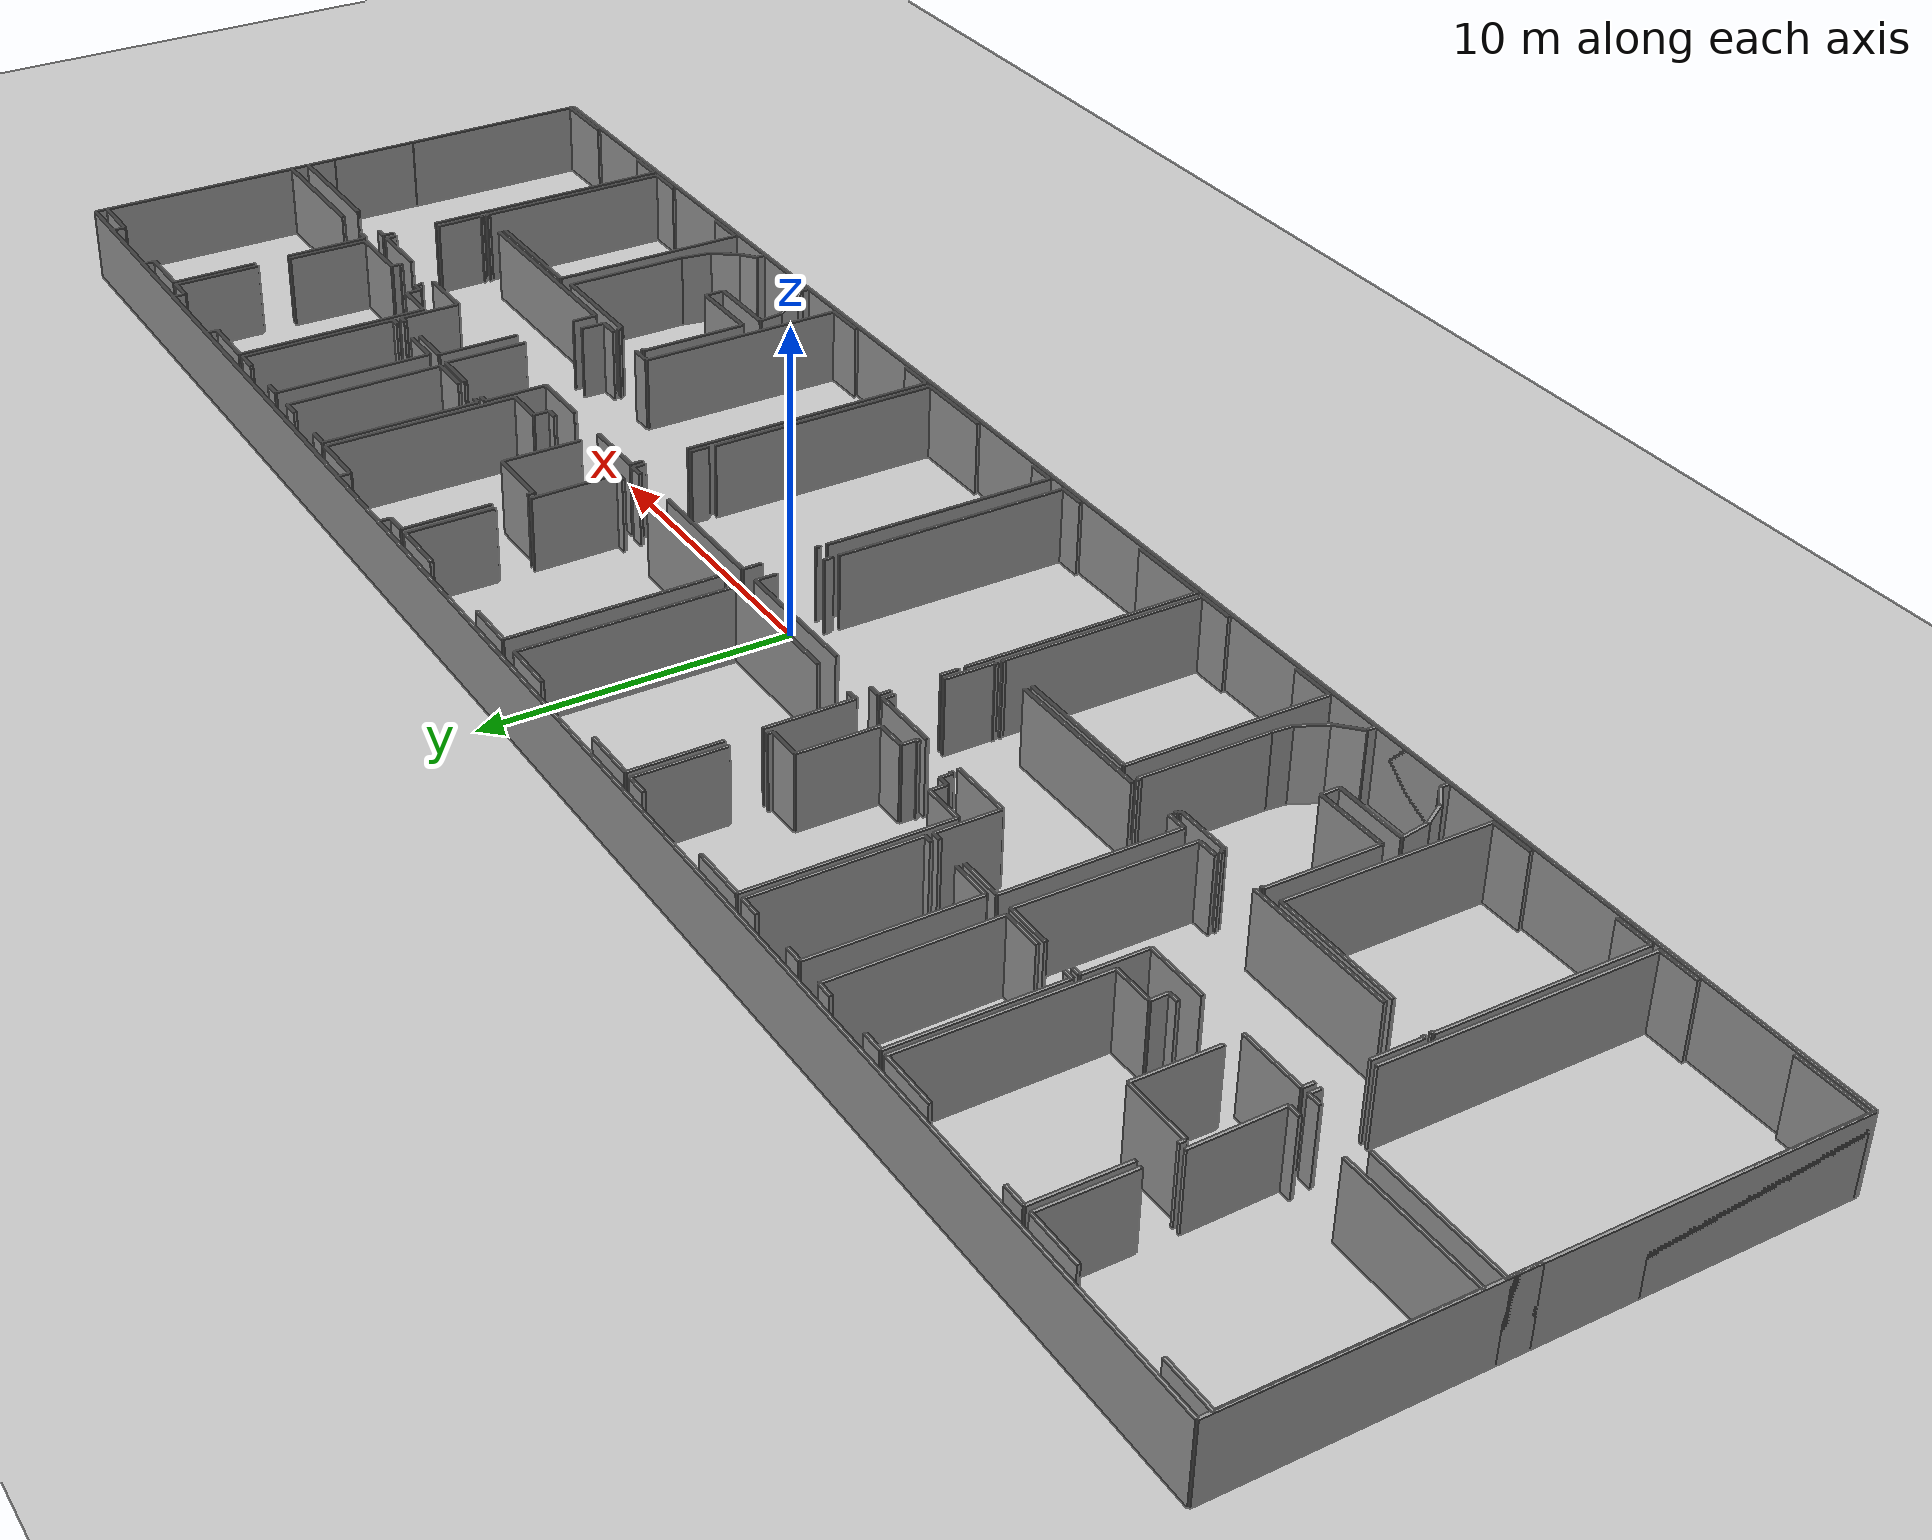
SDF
<sdf version="1.6">
  <world name="default">
    <light name="sun" type="directional">
      <cast_shadows>1</cast_shadows>
      <pose frame="">0 0 10 0 -0 0</pose>
      <diffuse>0.8 0.8 0.8 1</diffuse>
      <specular>0.1 0.1 0.1 1</specular>
      <attenuation>
        <range>1000</range>
        <constant>0.9</constant>
        <linear>0.01</linear>
        <quadratic>0.001</quadratic>
      </attenuation>
      <direction>-0.5 0.5 -1</direction>
    </light>
    <model name="ground_plane">
      <static>1</static>
      <link name="link">
        <collision name="collision">
          <geometry>
            <plane>
              <normal>0 0 1</normal>
              <size>100 100</size>
            </plane>
          </geometry>
          <surface>
            <friction>
              <ode>
                <mu>100</mu>
                <mu2>50</mu2>
              </ode>
              <torsional>
                <ode />
              </torsional>
            </friction>
            <contact>
              <ode />
            </contact>
            <bounce />
          </surface>
          <max_contacts>10</max_contacts>
        </collision>
        <visual name="visual">
          <cast_shadows>0</cast_shadows>
          <geometry>
            <plane>
              <normal>0 0 1</normal>
              <size>100 100</size>
            </plane>
          </geometry>
          <material>
            <script>
              <uri>file://media/materials/scripts/gazebo.material</uri>
              <name>Gazebo/Grey</name>
            </script>
          </material>
        </visual>
        <self_collide>0</self_collide>
        <kinematic>0</kinematic>
        <gravity>1</gravity>
      </link>
    </model>
    <gravity>0 0 -9.8</gravity>
    <magnetic_field>6e-06 2.3e-05 -4.2e-05</magnetic_field>
    <atmosphere type="adiabatic" />
    <physics default="0" name="default_physics" type="ode">
      <max_step_size>0.001</max_step_size>
      <real_time_factor>1</real_time_factor>
      <real_time_update_rate>1000</real_time_update_rate>
    </physics>
    <scene>
      <ambient>0.4 0.4 0.4 1</ambient>
      <background>0.7 0.7 0.7 1</background>
      <shadows>1</shadows>
    </scene>
    <spherical_coordinates>
      <surface_model>EARTH_WGS84</surface_model>
      <latitude_deg>0</latitude_deg>
      <longitude_deg>0</longitude_deg>
      <elevation>0</elevation>
      <heading_deg>0</heading_deg>
    </spherical_coordinates>
  <model name="0510034869_A-40">
		<static>1</static>
		<link name="Wall_0">
			<collision name="Wall_0_Collision">
				<geometry>
					<box>
						<size>0.420571428571 0.1 2.5</size>
					</box>
				</geometry>
				<pose frame="">0.210285714286 0 1.25 0 0 0</pose>
			</collision>
			<visual name="Wall_0_Visual">
				<pose frame="">0.210285714286 0 1.25 0 0 0</pose>
				<geometry>
					<box>
						<size>0.420571428571 0.1 2.5</size>
					</box>
				</geometry>
				<material>
					<script>
						<uri>file://media/materials/scripts/gazebo.material</uri>
						<name>Gazebo/Grey</name>
					</script>
					<ambient>1 1 1 1</ambient>
				</material>
			</visual>
			<pose frame="">6.64774603175 -7.3233015873 0 0 0 3.14159265359</pose>
		</link>
		<link name="Wall_1">
			<collision name="Wall_1_Collision">
				<geometry>
					<box>
						<size>4.67136507937 0.1 2.5</size>
					</box>
				</geometry>
				<pose frame="">2.33568253968 0 1.25 0 0 0</pose>
			</collision>
			<visual name="Wall_1_Visual">
				<pose frame="">2.33568253968 0 1.25 0 0 0</pose>
				<geometry>
					<box>
						<size>4.67136507937 0.1 2.5</size>
					</box>
				</geometry>
				<material>
					<script>
						<uri>file://media/materials/scripts/gazebo.material</uri>
						<name>Gazebo/Grey</name>
					</script>
					<ambient>1 1 1 1</ambient>
				</material>
			</visual>
			<pose frame="">4.67466666667 -7.3233015873 0 0 0 3.14159265359</pose>
		</link>
		<link name="Wall_2">
			<collision name="Wall_2_Collision">
				<geometry>
					<box>
						<size>6.91466666667 0.1 2.5</size>
					</box>
				</geometry>
				<pose frame="">3.45733333333 0 1.25 0 0 0</pose>
			</collision>
			<visual name="Wall_2_Visual">
				<pose frame="">3.45733333333 0 1.25 0 0 0</pose>
				<geometry>
					<box>
						<size>6.91466666667 0.1 2.5</size>
					</box>
				</geometry>
				<material>
					<script>
						<uri>file://media/materials/scripts/gazebo.material</uri>
						<name>Gazebo/Grey</name>
					</script>
					<ambient>1 1 1 1</ambient>
				</material>
			</visual>
			<pose frame="">0.00330158730159 -7.3233015873 0 0 0 1.57079632679</pose>
		</link>
		<link name="Wall_3">
			<collision name="Wall_3_Collision">
				<geometry>
					<box>
						<size>1.69777777778 0.1 2.5</size>
					</box>
				</geometry>
				<pose frame="">0.848888888889 0 1.25 0 0 0</pose>
			</collision>
			<visual name="Wall_3_Visual">
				<pose frame="">0.848888888889 0 1.25 0 0 0</pose>
				<geometry>
					<box>
						<size>1.69777777778 0.1 2.5</size>
					</box>
				</geometry>
				<material>
					<script>
						<uri>file://media/materials/scripts/gazebo.material</uri>
						<name>Gazebo/Grey</name>
					</script>
					<ambient>1 1 1 1</ambient>
				</material>
			</visual>
			<pose frame="">0.00330158730159 -0.408634920635 0 0 0 0.0</pose>
		</link>
		<link name="Wall_4">
			<collision name="Wall_4_Collision">
				<geometry>
					<box>
						<size>1.82806349206 0.1 2.5</size>
					</box>
				</geometry>
				<pose frame="">0.914031746032 0 1.25 0 0 0</pose>
			</collision>
			<visual name="Wall_4_Visual">
				<pose frame="">0.914031746032 0 1.25 0 0 0</pose>
				<geometry>
					<box>
						<size>1.82806349206 0.1 2.5</size>
					</box>
				</geometry>
				<material>
					<script>
						<uri>file://media/materials/scripts/gazebo.material</uri>
						<name>Gazebo/Grey</name>
					</script>
					<ambient>1 1 1 1</ambient>
				</material>
			</visual>
			<pose frame="">4.77066666667 -0.408634920635 0 0 0 0.0</pose>
		</link>
		<link name="Wall_5">
			<collision name="Wall_5_Collision">
				<geometry>
					<box>
						<size>2.88965079365 0.1 2.5</size>
					</box>
				</geometry>
				<pose frame="">1.44482539683 0 1.25 0 0 0</pose>
			</collision>
			<visual name="Wall_5_Visual">
				<pose frame="">1.44482539683 0 1.25 0 0 0</pose>
				<geometry>
					<box>
						<size>2.88965079365 0.1 2.5</size>
					</box>
				</geometry>
				<material>
					<script>
						<uri>file://media/materials/scripts/gazebo.material</uri>
						<name>Gazebo/Grey</name>
					</script>
					<ambient>1 1 1 1</ambient>
				</material>
			</visual>
			<pose frame="">6.59873015873 -0.408634920635 0 0 0 -1.57079632679</pose>
		</link>
		<link name="Wall_6">
			<collision name="Wall_6_Collision">
				<geometry>
					<box>
						<size>2.86632389309 0.1 2.5</size>
					</box>
				</geometry>
				<pose frame="">1.43316194655 0 1.25 0 0 0</pose>
			</collision>
			<visual name="Wall_6_Visual">
				<pose frame="">1.43316194655 0 1.25 0 0 0</pose>
				<geometry>
					<box>
						<size>2.86632389309 0.1 2.5</size>
					</box>
				</geometry>
				<material>
					<script>
						<uri>file://media/materials/scripts/gazebo.material</uri>
						<name>Gazebo/Grey</name>
					</script>
					<ambient>1 1 1 1</ambient>
				</material>
			</visual>
			<pose frame="">6.59873015873 -4.4573968254 0 0 0 -1.55369488812</pose>
		</link>
		<link name="Wall_7">
			<collision name="Wall_7_Collision">
				<geometry>
					<box>
						<size>0.36419047619 0.1 2.5</size>
					</box>
				</geometry>
				<pose frame="">0.182095238095 0 1.25 0 0 0</pose>
			</collision>
			<visual name="Wall_7_Visual">
				<pose frame="">0.182095238095 0 1.25 0 0 0</pose>
				<geometry>
					<box>
						<size>0.36419047619 0.1 2.5</size>
					</box>
				</geometry>
				<material>
					<script>
						<uri>file://media/materials/scripts/gazebo.material</uri>
						<name>Gazebo/Grey</name>
					</script>
					<ambient>1 1 1 1</ambient>
				</material>
			</visual>
			<pose frame="">11.2278095238 -7.3233015873 0 0 0 3.14159265359</pose>
		</link>
		<link name="Wall_8">
			<collision name="Wall_8_Collision">
				<geometry>
					<box>
						<size>2.66184126984 0.1 2.5</size>
					</box>
				</geometry>
				<pose frame="">1.33092063492 0 1.25 0 0 0</pose>
			</collision>
			<visual name="Wall_8_Visual">
				<pose frame="">1.33092063492 0 1.25 0 0 0</pose>
				<geometry>
					<box>
						<size>2.66184126984 0.1 2.5</size>
					</box>
				</geometry>
				<material>
					<script>
						<uri>file://media/materials/scripts/gazebo.material</uri>
						<name>Gazebo/Grey</name>
					</script>
					<ambient>1 1 1 1</ambient>
				</material>
			</visual>
			<pose frame="">9.06831746032 -7.3233015873 0 0 0 1.57079632679</pose>
		</link>
		<link name="Wall_9">
			<collision name="Wall_9_Collision">
				<geometry>
					<box>
						<size>2.22222222222 0.1 2.5</size>
					</box>
				</geometry>
				<pose frame="">1.11111111111 0 1.25 0 0 0</pose>
			</collision>
			<visual name="Wall_9_Visual">
				<pose frame="">1.11111111111 0 1.25 0 0 0</pose>
				<geometry>
					<box>
						<size>2.22222222222 0.1 2.5</size>
					</box>
				</geometry>
				<material>
					<script>
						<uri>file://media/materials/scripts/gazebo.material</uri>
						<name>Gazebo/Grey</name>
					</script>
					<ambient>1 1 1 1</ambient>
				</material>
			</visual>
			<pose frame="">9.06831746032 -4.66146031746 0 0 0 3.14159265359</pose>
		</link>
		<link name="Wall_10">
			<collision name="Wall_10_Collision">
				<geometry>
					<box>
						<size>0.209015873016 0.1 2.5</size>
					</box>
				</geometry>
				<pose frame="">0.104507936508 0 1.25 0 0 0</pose>
			</collision>
			<visual name="Wall_10_Visual">
				<pose frame="">0.104507936508 0 1.25 0 0 0</pose>
				<geometry>
					<box>
						<size>0.209015873016 0.1 2.5</size>
					</box>
				</geometry>
				<material>
					<script>
						<uri>file://media/materials/scripts/gazebo.material</uri>
						<name>Gazebo/Grey</name>
					</script>
					<ambient>1 1 1 1</ambient>
				</material>
			</visual>
			<pose frame="">6.8460952381 -4.66146031746 0 0 0 1.57079632679</pose>
		</link>
		<link name="Wall_11">
			<collision name="Wall_11_Collision">
				<geometry>
					<box>
						<size>2.91098412698 0.1 2.5</size>
					</box>
				</geometry>
				<pose frame="">1.45549206349 0 1.25 0 0 0</pose>
			</collision>
			<visual name="Wall_11_Visual">
				<pose frame="">1.45549206349 0 1.25 0 0 0</pose>
				<geometry>
					<box>
						<size>2.91098412698 0.1 2.5</size>
					</box>
				</geometry>
				<material>
					<script>
						<uri>file://media/materials/scripts/gazebo.material</uri>
						<name>Gazebo/Grey</name>
					</script>
					<ambient>1 1 1 1</ambient>
				</material>
			</visual>
			<pose frame="">6.8460952381 -3.31936507937 0 0 0 1.57079632679</pose>
		</link>
		<link name="Wall_12">
			<collision name="Wall_12_Collision">
				<geometry>
					<box>
						<size>0.750984126984 0.1 2.5</size>
					</box>
				</geometry>
				<pose frame="">0.375492063492 0 1.25 0 0 0</pose>
			</collision>
			<visual name="Wall_12_Visual">
				<pose frame="">0.375492063492 0 1.25 0 0 0</pose>
				<geometry>
					<box>
						<size>0.750984126984 0.1 2.5</size>
					</box>
				</geometry>
				<material>
					<script>
						<uri>file://media/materials/scripts/gazebo.material</uri>
						<name>Gazebo/Grey</name>
					</script>
					<ambient>1 1 1 1</ambient>
				</material>
			</visual>
			<pose frame="">6.8460952381 -0.408380952381 0 0 0 0.0</pose>
		</link>
		<link name="Wall_13">
			<collision name="Wall_13_Collision">
				<geometry>
					<box>
						<size>1.90501587302 0.1 2.5</size>
					</box>
				</geometry>
				<pose frame="">0.952507936508 0 1.25 0 0 0</pose>
			</collision>
			<visual name="Wall_13_Visual">
				<pose frame="">0.952507936508 0 1.25 0 0 0</pose>
				<geometry>
					<box>
						<size>1.90501587302 0.1 2.5</size>
					</box>
				</geometry>
				<material>
					<script>
						<uri>file://media/materials/scripts/gazebo.material</uri>
						<name>Gazebo/Grey</name>
					</script>
					<ambient>1 1 1 1</ambient>
				</material>
			</visual>
			<pose frame="">10.6667936508 -0.408380952381 0 0 0 0.0</pose>
		</link>
		<link name="Wall_14">
			<collision name="Wall_14_Collision">
				<geometry>
					<box>
						<size>6.36177777778 0.1 2.5</size>
					</box>
				</geometry>
				<pose frame="">3.18088888889 0 1.25 0 0 0</pose>
			</collision>
			<visual name="Wall_14_Visual">
				<pose frame="">3.18088888889 0 1.25 0 0 0</pose>
				<geometry>
					<box>
						<size>6.36177777778 0.1 2.5</size>
					</box>
				</geometry>
				<material>
					<script>
						<uri>file://media/materials/scripts/gazebo.material</uri>
						<name>Gazebo/Grey</name>
					</script>
					<ambient>1 1 1 1</ambient>
				</material>
			</visual>
			<pose frame="">12.5718095238 -0.408380952381 0 0 0 -1.57079632679</pose>
		</link>
		<link name="Wall_15">
			<collision name="Wall_15_Collision">
				<geometry>
					<box>
						<size>1.35606349206 0.1 2.5</size>
					</box>
				</geometry>
				<pose frame="">0.678031746032 0 1.25 0 0 0</pose>
			</collision>
			<visual name="Wall_15_Visual">
				<pose frame="">0.678031746032 0 1.25 0 0 0</pose>
				<geometry>
					<box>
						<size>1.35606349206 0.1 2.5</size>
					</box>
				</geometry>
				<material>
					<script>
						<uri>file://media/materials/scripts/gazebo.material</uri>
						<name>Gazebo/Grey</name>
					</script>
					<ambient>1 1 1 1</ambient>
				</material>
			</visual>
			<pose frame="">12.5718095238 -6.77015873016 0 0 0 3.14159265359</pose>
		</link>
		<link name="Wall_16">
			<collision name="Wall_16_Collision">
				<geometry>
					<box>
						<size>0.553274387848 0.1 2.5</size>
					</box>
				</geometry>
				<pose frame="">0.276637193924 0 1.25 0 0 0</pose>
			</collision>
			<visual name="Wall_16_Visual">
				<pose frame="">0.276637193924 0 1.25 0 0 0</pose>
				<geometry>
					<box>
						<size>0.553274387848 0.1 2.5</size>
					</box>
				</geometry>
				<material>
					<script>
						<uri>file://media/materials/scripts/gazebo.material</uri>
						<name>Gazebo/Grey</name>
					</script>
					<ambient>1 1 1 1</ambient>
				</material>
			</visual>
			<pose frame="">11.2157460317 -6.77015873016 0 0 0 -1.54899078442</pose>
		</link>
		<link name="Wall_17">
			<collision name="Wall_17_Collision">
				<geometry>
					<box>
						<size>1.31847619048 0.1 2.5</size>
					</box>
				</geometry>
				<pose frame="">0.659238095238 0 1.25 0 0 0</pose>
			</collision>
			<visual name="Wall_17_Visual">
				<pose frame="">0.659238095238 0 1.25 0 0 0</pose>
				<geometry>
					<box>
						<size>1.31847619048 0.1 2.5</size>
					</box>
				</geometry>
				<material>
					<script>
						<uri>file://media/materials/scripts/gazebo.material</uri>
						<name>Gazebo/Grey</name>
					</script>
					<ambient>1 1 1 1</ambient>
				</material>
			</visual>
			<pose frame="">6.74374603175 -18.4038095238 0 0 0 3.14159265359</pose>
		</link>
		<link name="Wall_18">
			<collision name="Wall_18_Collision">
				<geometry>
					<box>
						<size>2.33320634921 0.1 2.5</size>
					</box>
				</geometry>
				<pose frame="">1.1666031746 0 1.25 0 0 0</pose>
			</collision>
			<visual name="Wall_18_Visual">
				<pose frame="">1.1666031746 0 1.25 0 0 0</pose>
				<geometry>
					<box>
						<size>2.33320634921 0.1 2.5</size>
					</box>
				</geometry>
				<material>
					<script>
						<uri>file://media/materials/scripts/gazebo.material</uri>
						<name>Gazebo/Grey</name>
					</script>
					<ambient>1 1 1 1</ambient>
				</material>
			</visual>
			<pose frame="">2.33320634921 -18.4038095238 0 0 0 3.14159265359</pose>
		</link>
		<link name="Wall_19">
			<collision name="Wall_19_Collision">
				<geometry>
					<box>
						<size>6.41676190476 0.1 2.5</size>
					</box>
				</geometry>
				<pose frame="">3.20838095238 0 1.25 0 0 0</pose>
			</collision>
			<visual name="Wall_19_Visual">
				<pose frame="">3.20838095238 0 1.25 0 0 0</pose>
				<geometry>
					<box>
						<size>6.41676190476 0.1 2.5</size>
					</box>
				</geometry>
				<material>
					<script>
						<uri>file://media/materials/scripts/gazebo.material</uri>
						<name>Gazebo/Grey</name>
					</script>
					<ambient>1 1 1 1</ambient>
				</material>
			</visual>
			<pose frame="">0.0 -18.4038095238 0 0 0 1.57079632679</pose>
		</link>
		<link name="Wall_20">
			<collision name="Wall_20_Collision">
				<geometry>
					<box>
						<size>0.951111111111 0.1 2.5</size>
					</box>
				</geometry>
				<pose frame="">0.475555555556 0 1.25 0 0 0</pose>
			</collision>
			<visual name="Wall_20_Visual">
				<pose frame="">0.475555555556 0 1.25 0 0 0</pose>
				<geometry>
					<box>
						<size>0.951111111111 0.1 2.5</size>
					</box>
				</geometry>
				<material>
					<script>
						<uri>file://media/materials/scripts/gazebo.material</uri>
						<name>Gazebo/Grey</name>
					</script>
					<ambient>1 1 1 1</ambient>
				</material>
			</visual>
			<pose frame="">0.0 -8.90323809524 0 0 0 1.57079632679</pose>
		</link>
		<link name="Wall_21">
			<collision name="Wall_21_Collision">
				<geometry>
					<box>
						<size>4.52914285714 0.1 2.5</size>
					</box>
				</geometry>
				<pose frame="">2.26457142857 0 1.25 0 0 0</pose>
			</collision>
			<visual name="Wall_21_Visual">
				<pose frame="">2.26457142857 0 1.25 0 0 0</pose>
				<geometry>
					<box>
						<size>4.52914285714 0.1 2.5</size>
					</box>
				</geometry>
				<material>
					<script>
						<uri>file://media/materials/scripts/gazebo.material</uri>
						<name>Gazebo/Grey</name>
					</script>
					<ambient>1 1 1 1</ambient>
				</material>
			</visual>
			<pose frame="">0.0 -7.95212698413 0 0 0 0.0</pose>
		</link>
		<link name="Wall_22">
			<collision name="Wall_22_Collision">
				<geometry>
					<box>
						<size>0.44419047619 0.1 2.5</size>
					</box>
				</geometry>
				<pose frame="">0.222095238095 0 1.25 0 0 0</pose>
			</collision>
			<visual name="Wall_22_Visual">
				<pose frame="">0.222095238095 0 1.25 0 0 0</pose>
				<geometry>
					<box>
						<size>0.44419047619 0.1 2.5</size>
					</box>
				</geometry>
				<material>
					<script>
						<uri>file://media/materials/scripts/gazebo.material</uri>
						<name>Gazebo/Grey</name>
					</script>
					<ambient>1 1 1 1</ambient>
				</material>
			</visual>
			<pose frame="">6.3020952381 -7.95212698413 0 0 0 0.0</pose>
		</link>
		<link name="Wall_23">
			<collision name="Wall_23_Collision">
				<geometry>
					<box>
						<size>0.371047619048 0.1 2.5</size>
					</box>
				</geometry>
				<pose frame="">0.185523809524 0 1.25 0 0 0</pose>
			</collision>
			<visual name="Wall_23_Visual">
				<pose frame="">0.185523809524 0 1.25 0 0 0</pose>
				<geometry>
					<box>
						<size>0.371047619048 0.1 2.5</size>
					</box>
				</geometry>
				<material>
					<script>
						<uri>file://media/materials/scripts/gazebo.material</uri>
						<name>Gazebo/Grey</name>
					</script>
					<ambient>1 1 1 1</ambient>
				</material>
			</visual>
			<pose frame="">6.74628571429 -7.95212698413 0 0 0 -1.57079632679</pose>
		</link>
		<link name="Wall_24">
			<collision name="Wall_24_Collision">
				<geometry>
					<box>
						<size>8.53485752072 0.1 2.5</size>
					</box>
				</geometry>
				<pose frame="">4.26742876036 0 1.25 0 0 0</pose>
			</collision>
			<visual name="Wall_24_Visual">
				<pose frame="">4.26742876036 0 1.25 0 0 0</pose>
				<geometry>
					<box>
						<size>8.53485752072 0.1 2.5</size>
					</box>
				</geometry>
				<material>
					<script>
						<uri>file://media/materials/scripts/gazebo.material</uri>
						<name>Gazebo/Grey</name>
					</script>
					<ambient>1 1 1 1</ambient>
				</material>
			</visual>
			<pose frame="">6.74628571429 -9.86895238095 0 0 0 -1.5710938927</pose>
		</link>
		<link name="Wall_25">
			<collision name="Wall_25_Collision">
				<geometry>
					<box>
						<size>1.43657142857 0.1 2.5</size>
					</box>
				</geometry>
				<pose frame="">0.718285714286 0 1.25 0 0 0</pose>
			</collision>
			<visual name="Wall_25_Visual">
				<pose frame="">0.718285714286 0 1.25 0 0 0</pose>
				<geometry>
					<box>
						<size>1.43657142857 0.1 2.5</size>
					</box>
				</geometry>
				<material>
					<script>
						<uri>file://media/materials/scripts/gazebo.material</uri>
						<name>Gazebo/Grey</name>
					</script>
					<ambient>1 1 1 1</ambient>
				</material>
			</visual>
			<pose frame="">12.7459047619 -18.3851428571 0 0 0 3.14159265359</pose>
		</link>
		<link name="Wall_26">
			<collision name="Wall_26_Collision">
				<geometry>
					<box>
						<size>1.21219047619 0.1 2.5</size>
					</box>
				</geometry>
				<pose frame="">0.606095238095 0 1.25 0 0 0</pose>
			</collision>
			<visual name="Wall_26_Visual">
				<pose frame="">0.606095238095 0 1.25 0 0 0</pose>
				<geometry>
					<box>
						<size>1.21219047619 0.1 2.5</size>
					</box>
				</geometry>
				<material>
					<script>
						<uri>file://media/materials/scripts/gazebo.material</uri>
						<name>Gazebo/Grey</name>
					</script>
					<ambient>1 1 1 1</ambient>
				</material>
			</visual>
			<pose frame="">8.20952380952 -18.3851428571 0 0 0 3.14159265359</pose>
		</link>
		<link name="Wall_27">
			<collision name="Wall_27_Collision">
				<geometry>
					<box>
						<size>6.65536507937 0.1 2.5</size>
					</box>
				</geometry>
				<pose frame="">3.32768253968 0 1.25 0 0 0</pose>
			</collision>
			<visual name="Wall_27_Visual">
				<pose frame="">3.32768253968 0 1.25 0 0 0</pose>
				<geometry>
					<box>
						<size>6.65536507937 0.1 2.5</size>
					</box>
				</geometry>
				<material>
					<script>
						<uri>file://media/materials/scripts/gazebo.material</uri>
						<name>Gazebo/Grey</name>
					</script>
					<ambient>1 1 1 1</ambient>
				</material>
			</visual>
			<pose frame="">6.99733333333 -18.3851428571 0 0 0 1.57079632679</pose>
		</link>
		<link name="Wall_28">
			<collision name="Wall_28_Collision">
				<geometry>
					<box>
						<size>0.0913015873016 0.1 2.5</size>
					</box>
				</geometry>
				<pose frame="">0.0456507936508 0 1.25 0 0 0</pose>
			</collision>
			<visual name="Wall_28_Visual">
				<pose frame="">0.0456507936508 0 1.25 0 0 0</pose>
				<geometry>
					<box>
						<size>0.0913015873016 0.1 2.5</size>
					</box>
				</geometry>
				<material>
					<script>
						<uri>file://media/materials/scripts/gazebo.material</uri>
						<name>Gazebo/Grey</name>
					</script>
					<ambient>1 1 1 1</ambient>
				</material>
			</visual>
			<pose frame="">6.99733333333 -11.7297777778 0 0 0 0.0</pose>
		</link>
		<link name="Wall_29">
			<collision name="Wall_29_Collision">
				<geometry>
					<box>
						<size>4.31771428571 0.1 2.5</size>
					</box>
				</geometry>
				<pose frame="">2.15885714286 0 1.25 0 0 0</pose>
			</collision>
			<visual name="Wall_29_Visual">
				<pose frame="">2.15885714286 0 1.25 0 0 0</pose>
				<geometry>
					<box>
						<size>4.31771428571 0.1 2.5</size>
					</box>
				</geometry>
				<material>
					<script>
						<uri>file://media/materials/scripts/gazebo.material</uri>
						<name>Gazebo/Grey</name>
					</script>
					<ambient>1 1 1 1</ambient>
				</material>
			</visual>
			<pose frame="">8.43365079365 -11.7297777778 0 0 0 0.0</pose>
		</link>
		<link name="Wall_30">
			<collision name="Wall_30_Collision">
				<geometry>
					<box>
						<size>6.65536731929 0.1 2.5</size>
					</box>
				</geometry>
				<pose frame="">3.32768365965 0 1.25 0 0 0</pose>
			</collision>
			<visual name="Wall_30_Visual">
				<pose frame="">3.32768365965 0 1.25 0 0 0</pose>
				<geometry>
					<box>
						<size>6.65536731929 0.1 2.5</size>
					</box>
				</geometry>
				<material>
					<script>
						<uri>file://media/materials/scripts/gazebo.material</uri>
						<name>Gazebo/Grey</name>
					</script>
					<ambient>1 1 1 1</ambient>
				</material>
			</visual>
			<pose frame="">12.7513650794 -11.7297777778 0 0 0 -1.57161676507</pose>
		</link>
		<link name="Wall_31">
			<collision name="Wall_31_Collision">
				<geometry>
					<box>
						<size>0.70146031746 0.1 2.5</size>
					</box>
				</geometry>
				<pose frame="">0.35073015873 0 1.25 0 0 0</pose>
			</collision>
			<visual name="Wall_31_Visual">
				<pose frame="">0.35073015873 0 1.25 0 0 0</pose>
				<geometry>
					<box>
						<size>0.70146031746 0.1 2.5</size>
					</box>
				</geometry>
				<material>
					<script>
						<uri>file://media/materials/scripts/gazebo.material</uri>
						<name>Gazebo/Grey</name>
					</script>
					<ambient>1 1 1 1</ambient>
				</material>
			</visual>
			<pose frame="">15.7603809524 -11.4805079365 0 0 0 3.14159265359</pose>
		</link>
		<link name="Wall_32">
			<collision name="Wall_32_Collision">
				<geometry>
					<box>
						<size>5.05282539683 0.1 2.5</size>
					</box>
				</geometry>
				<pose frame="">2.52641269841 0 1.25 0 0 0</pose>
			</collision>
			<visual name="Wall_32_Visual">
				<pose frame="">2.52641269841 0 1.25 0 0 0</pose>
				<geometry>
					<box>
						<size>5.05282539683 0.1 2.5</size>
					</box>
				</geometry>
				<material>
					<script>
						<uri>file://media/materials/scripts/gazebo.material</uri>
						<name>Gazebo/Grey</name>
					</script>
					<ambient>1 1 1 1</ambient>
				</material>
			</visual>
			<pose frame="">13.4857142857 -11.4805079365 0 0 0 3.14159265359</pose>
		</link>
		<link name="Wall_33">
			<collision name="Wall_33_Collision">
				<geometry>
					<box>
						<size>0.088253968254 0.1 2.5</size>
					</box>
				</geometry>
				<pose frame="">0.044126984127 0 1.25 0 0 0</pose>
			</collision>
			<visual name="Wall_33_Visual">
				<pose frame="">0.044126984127 0 1.25 0 0 0</pose>
				<geometry>
					<box>
						<size>0.088253968254 0.1 2.5</size>
					</box>
				</geometry>
				<material>
					<script>
						<uri>file://media/materials/scripts/gazebo.material</uri>
						<name>Gazebo/Grey</name>
					</script>
					<ambient>1 1 1 1</ambient>
				</material>
			</visual>
			<pose frame="">7.07022222222 -11.4805079365 0 0 0 3.14159265359</pose>
		</link>
		<link name="Wall_34">
			<collision name="Wall_34_Collision">
				<geometry>
					<box>
						<size>1.60431746032 0.1 2.5</size>
					</box>
				</geometry>
				<pose frame="">0.802158730159 0 1.25 0 0 0</pose>
			</collision>
			<visual name="Wall_34_Visual">
				<pose frame="">0.802158730159 0 1.25 0 0 0</pose>
				<geometry>
					<box>
						<size>1.60431746032 0.1 2.5</size>
					</box>
				</geometry>
				<material>
					<script>
						<uri>file://media/materials/scripts/gazebo.material</uri>
						<name>Gazebo/Grey</name>
					</script>
					<ambient>1 1 1 1</ambient>
				</material>
			</visual>
			<pose frame="">6.98196825397 -11.4805079365 0 0 0 1.57079632679</pose>
		</link>
		<link name="Wall_35">
			<collision name="Wall_35_Collision">
				<geometry>
					<box>
						<size>0.366095238095 0.1 2.5</size>
					</box>
				</geometry>
				<pose frame="">0.183047619048 0 1.25 0 0 0</pose>
			</collision>
			<visual name="Wall_35_Visual">
				<pose frame="">0.183047619048 0 1.25 0 0 0</pose>
				<geometry>
					<box>
						<size>0.366095238095 0.1 2.5</size>
					</box>
				</geometry>
				<material>
					<script>
						<uri>file://media/materials/scripts/gazebo.material</uri>
						<name>Gazebo/Grey</name>
					</script>
					<ambient>1 1 1 1</ambient>
				</material>
			</visual>
			<pose frame="">6.98196825397 -8.31263492063 0 0 0 1.57079632679</pose>
		</link>
		<link name="Wall_36">
			<collision name="Wall_36_Collision">
				<geometry>
					<box>
						<size>2.18082539683 0.1 2.5</size>
					</box>
				</geometry>
				<pose frame="">1.09041269841 0 1.25 0 0 0</pose>
			</collision>
			<visual name="Wall_36_Visual">
				<pose frame="">1.09041269841 0 1.25 0 0 0</pose>
				<geometry>
					<box>
						<size>2.18082539683 0.1 2.5</size>
					</box>
				</geometry>
				<material>
					<script>
						<uri>file://media/materials/scripts/gazebo.material</uri>
						<name>Gazebo/Grey</name>
					</script>
					<ambient>1 1 1 1</ambient>
				</material>
			</visual>
			<pose frame="">6.98196825397 -7.94653968254 0 0 0 0.0</pose>
		</link>
		<link name="Wall_37">
			<collision name="Wall_37_Collision">
				<geometry>
					<box>
						<size>2.0766984127 0.1 2.5</size>
					</box>
				</geometry>
				<pose frame="">1.03834920635 0 1.25 0 0 0</pose>
			</collision>
			<visual name="Wall_37_Visual">
				<pose frame="">1.03834920635 0 1.25 0 0 0</pose>
				<geometry>
					<box>
						<size>2.0766984127 0.1 2.5</size>
					</box>
				</geometry>
				<material>
					<script>
						<uri>file://media/materials/scripts/gazebo.material</uri>
						<name>Gazebo/Grey</name>
					</script>
					<ambient>1 1 1 1</ambient>
				</material>
			</visual>
			<pose frame="">10.7473015873 -7.94653968254 0 0 0 0.0</pose>
		</link>
		<link name="Wall_38">
			<collision name="Wall_38_Collision">
				<geometry>
					<box>
						<size>2.06349206349 0.1 2.5</size>
					</box>
				</geometry>
				<pose frame="">1.03174603175 0 1.25 0 0 0</pose>
			</collision>
			<visual name="Wall_38_Visual">
				<pose frame="">1.03174603175 0 1.25 0 0 0</pose>
				<geometry>
					<box>
						<size>2.06349206349 0.1 2.5</size>
					</box>
				</geometry>
				<material>
					<script>
						<uri>file://media/materials/scripts/gazebo.material</uri>
						<name>Gazebo/Grey</name>
					</script>
					<ambient>1 1 1 1</ambient>
				</material>
			</visual>
			<pose frame="">12.824 -7.94653968254 0 0 0 1.57079632679</pose>
		</link>
		<link name="Wall_39">
			<collision name="Wall_39_Collision">
				<geometry>
					<box>
						<size>0.283047619048 0.1 2.5</size>
					</box>
				</geometry>
				<pose frame="">0.141523809524 0 1.25 0 0 0</pose>
			</collision>
			<visual name="Wall_39_Visual">
				<pose frame="">0.141523809524 0 1.25 0 0 0</pose>
				<geometry>
					<box>
						<size>0.283047619048 0.1 2.5</size>
					</box>
				</geometry>
				<material>
					<script>
						<uri>file://media/materials/scripts/gazebo.material</uri>
						<name>Gazebo/Grey</name>
					</script>
					<ambient>1 1 1 1</ambient>
				</material>
			</visual>
			<pose frame="">12.824 -5.88304761905 0 0 0 0.0</pose>
		</link>
		<link name="Wall_40">
			<collision name="Wall_40_Collision">
				<geometry>
					<box>
						<size>1.51707936508 0.1 2.5</size>
					</box>
				</geometry>
				<pose frame="">0.75853968254 0 1.25 0 0 0</pose>
			</collision>
			<visual name="Wall_40_Visual">
				<pose frame="">0.75853968254 0 1.25 0 0 0</pose>
				<geometry>
					<box>
						<size>1.51707936508 0.1 2.5</size>
					</box>
				</geometry>
				<material>
					<script>
						<uri>file://media/materials/scripts/gazebo.material</uri>
						<name>Gazebo/Grey</name>
					</script>
					<ambient>1 1 1 1</ambient>
				</material>
			</visual>
			<pose frame="">14.261968254 -5.88304761905 0 0 0 0.0</pose>
		</link>
		<link name="Wall_41">
			<collision name="Wall_41_Collision">
				<geometry>
					<box>
						<size>5.5974914426 0.1 2.5</size>
					</box>
				</geometry>
				<pose frame="">2.7987457213 0 1.25 0 0 0</pose>
			</collision>
			<visual name="Wall_41_Visual">
				<pose frame="">2.7987457213 0 1.25 0 0 0</pose>
				<geometry>
					<box>
						<size>5.5974914426 0.1 2.5</size>
					</box>
				</geometry>
				<material>
					<script>
						<uri>file://media/materials/scripts/gazebo.material</uri>
						<name>Gazebo/Grey</name>
					</script>
					<ambient>1 1 1 1</ambient>
				</material>
			</visual>
			<pose frame="">15.779047619 -5.88304761905 0 0 0 -1.57413116017</pose>
		</link>
		<link name="Wall_42">
			<collision name="Wall_42_Collision">
				<geometry>
					<box>
						<size>1.34082539683 0.1 2.5</size>
					</box>
				</geometry>
				<pose frame="">0.670412698413 0 1.25 0 0 0</pose>
			</collision>
			<visual name="Wall_42_Visual">
				<pose frame="">0.670412698413 0 1.25 0 0 0</pose>
				<geometry>
					<box>
						<size>1.34082539683 0.1 2.5</size>
					</box>
				</geometry>
				<material>
					<script>
						<uri>file://media/materials/scripts/gazebo.material</uri>
						<name>Gazebo/Grey</name>
					</script>
					<ambient>1 1 1 1</ambient>
				</material>
			</visual>
			<pose frame="">15.6168888889 -5.66463492063 0 0 0 3.14159265359</pose>
		</link>
		<link name="Wall_43">
			<collision name="Wall_43_Collision">
				<geometry>
					<box>
						<size>0.331174603175 0.1 2.5</size>
					</box>
				</geometry>
				<pose frame="">0.165587301587 0 1.25 0 0 0</pose>
			</collision>
			<visual name="Wall_43_Visual">
				<pose frame="">0.165587301587 0 1.25 0 0 0</pose>
				<geometry>
					<box>
						<size>0.331174603175 0.1 2.5</size>
					</box>
				</geometry>
				<material>
					<script>
						<uri>file://media/materials/scripts/gazebo.material</uri>
						<name>Gazebo/Grey</name>
					</script>
					<ambient>1 1 1 1</ambient>
				</material>
			</visual>
			<pose frame="">13.1212698413 -5.66463492063 0 0 0 3.14159265359</pose>
		</link>
		<link name="Wall_44">
			<collision name="Wall_44_Collision">
				<geometry>
					<box>
						<size>5.26501587302 0.1 2.5</size>
					</box>
				</geometry>
				<pose frame="">2.63250793651 0 1.25 0 0 0</pose>
			</collision>
			<visual name="Wall_44_Visual">
				<pose frame="">2.63250793651 0 1.25 0 0 0</pose>
				<geometry>
					<box>
						<size>5.26501587302 0.1 2.5</size>
					</box>
				</geometry>
				<material>
					<script>
						<uri>file://media/materials/scripts/gazebo.material</uri>
						<name>Gazebo/Grey</name>
					</script>
					<ambient>1 1 1 1</ambient>
				</material>
			</visual>
			<pose frame="">12.7900952381 -5.66463492063 0 0 0 1.57079632679</pose>
		</link>
		<link name="Wall_45">
			<collision name="Wall_45_Collision">
				<geometry>
					<box>
						<size>0.702476190476 0.1 2.5</size>
					</box>
				</geometry>
				<pose frame="">0.351238095238 0 1.25 0 0 0</pose>
			</collision>
			<visual name="Wall_45_Visual">
				<pose frame="">0.351238095238 0 1.25 0 0 0</pose>
				<geometry>
					<box>
						<size>0.702476190476 0.1 2.5</size>
					</box>
				</geometry>
				<material>
					<script>
						<uri>file://media/materials/scripts/gazebo.material</uri>
						<name>Gazebo/Grey</name>
					</script>
					<ambient>1 1 1 1</ambient>
				</material>
			</visual>
			<pose frame="">12.7900952381 -0.399619047619 0 0 0 0.0</pose>
		</link>
		<link name="Wall_46">
			<collision name="Wall_46_Collision">
				<geometry>
					<box>
						<size>0.549206349206 0.1 2.5</size>
					</box>
				</geometry>
				<pose frame="">0.274603174603 0 1.25 0 0 0</pose>
			</collision>
			<visual name="Wall_46_Visual">
				<pose frame="">0.274603174603 0 1.25 0 0 0</pose>
				<geometry>
					<box>
						<size>0.549206349206 0.1 2.5</size>
					</box>
				</geometry>
				<material>
					<script>
						<uri>file://media/materials/scripts/gazebo.material</uri>
						<name>Gazebo/Grey</name>
					</script>
					<ambient>1 1 1 1</ambient>
				</material>
			</visual>
			<pose frame="">15.0342857143 -0.399619047619 0 0 0 0.0</pose>
		</link>
		<link name="Wall_47">
			<collision name="Wall_47_Collision">
				<geometry>
					<box>
						<size>5.26512179261 0.1 2.5</size>
					</box>
				</geometry>
				<pose frame="">2.63256089631 0 1.25 0 0 0</pose>
			</collision>
			<visual name="Wall_47_Visual">
				<pose frame="">2.63256089631 0 1.25 0 0 0</pose>
				<geometry>
					<box>
						<size>5.26512179261 0.1 2.5</size>
					</box>
				</geometry>
				<material>
					<script>
						<uri>file://media/materials/scripts/gazebo.material</uri>
						<name>Gazebo/Grey</name>
					</script>
					<ambient>1 1 1 1</ambient>
				</material>
			</visual>
			<pose frame="">15.5834920635 -0.399619047619 0 0 0 -1.56445325428</pose>
		</link>
		<link name="Wall_48">
			<collision name="Wall_48_Collision">
				<geometry>
					<box>
						<size>2.9826031746 0.1 2.5</size>
					</box>
				</geometry>
				<pose frame="">1.4913015873 0 1.25 0 0 0</pose>
			</collision>
			<visual name="Wall_48_Visual">
				<pose frame="">1.4913015873 0 1.25 0 0 0</pose>
				<geometry>
					<box>
						<size>2.9826031746 0.1 2.5</size>
					</box>
				</geometry>
				<material>
					<script>
						<uri>file://media/materials/scripts/gazebo.material</uri>
						<name>Gazebo/Grey</name>
					</script>
					<ambient>1 1 1 1</ambient>
				</material>
			</visual>
			<pose frame="">17.5939047619 -18.5479365079 0 0 0 3.14159265359</pose>
		</link>
		<link name="Wall_49">
			<collision name="Wall_49_Collision">
				<geometry>
					<box>
						<size>0.316952380952 0.1 2.5</size>
					</box>
				</geometry>
				<pose frame="">0.158476190476 0 1.25 0 0 0</pose>
			</collision>
			<visual name="Wall_49_Visual">
				<pose frame="">0.158476190476 0 1.25 0 0 0</pose>
				<geometry>
					<box>
						<size>0.316952380952 0.1 2.5</size>
					</box>
				</geometry>
				<material>
					<script>
						<uri>file://media/materials/scripts/gazebo.material</uri>
						<name>Gazebo/Grey</name>
					</script>
					<ambient>1 1 1 1</ambient>
				</material>
			</visual>
			<pose frame="">14.6113015873 -18.5479365079 0 0 0 1.57079632679</pose>
		</link>
		<link name="Wall_50">
			<collision name="Wall_50_Collision">
				<geometry>
					<box>
						<size>0.798795899079 0.1 2.5</size>
					</box>
				</geometry>
				<pose frame="">0.399397949539 0 1.25 0 0 0</pose>
			</collision>
			<visual name="Wall_50_Visual">
				<pose frame="">0.399397949539 0 1.25 0 0 0</pose>
				<geometry>
					<box>
						<size>0.798795899079 0.1 2.5</size>
					</box>
				</geometry>
				<material>
					<script>
						<uri>file://media/materials/scripts/gazebo.material</uri>
						<name>Gazebo/Grey</name>
					</script>
					<ambient>1 1 1 1</ambient>
				</material>
			</visual>
			<pose frame="">14.6113015873 -18.230984127 0 0 0 2.45697046285</pose>
		</link>
		<link name="Wall_51">
			<collision name="Wall_51_Collision">
				<geometry>
					<box>
						<size>0.902953277761 0.1 2.5</size>
					</box>
				</geometry>
				<pose frame="">0.45147663888 0 1.25 0 0 0</pose>
			</collision>
			<visual name="Wall_51_Visual">
				<pose frame="">0.45147663888 0 1.25 0 0 0</pose>
				<geometry>
					<box>
						<size>0.902953277761 0.1 2.5</size>
					</box>
				</geometry>
				<material>
					<script>
						<uri>file://media/materials/scripts/gazebo.material</uri>
						<name>Gazebo/Grey</name>
					</script>
					<ambient>1 1 1 1</ambient>
				</material>
			</visual>
			<pose frame="">13.9925079365 -17.7258412698 0 0 0 2.10639217049</pose>
		</link>
		<link name="Wall_52">
			<collision name="Wall_52_Collision">
				<geometry>
					<box>
						<size>0.992218938933 0.1 2.5</size>
					</box>
				</geometry>
				<pose frame="">0.496109469466 0 1.25 0 0 0</pose>
			</collision>
			<visual name="Wall_52_Visual">
				<pose frame="">0.496109469466 0 1.25 0 0 0</pose>
				<geometry>
					<box>
						<size>0.992218938933 0.1 2.5</size>
					</box>
				</geometry>
				<material>
					<script>
						<uri>file://media/materials/scripts/gazebo.material</uri>
						<name>Gazebo/Grey</name>
					</script>
					<ambient>1 1 1 1</ambient>
				</material>
			</visual>
			<pose frame="">13.5316825397 -16.9493333333 0 0 0 1.73703907266</pose>
		</link>
		<link name="Wall_53">
			<collision name="Wall_53_Collision">
				<geometry>
					<box>
						<size>2.50006349206 0.1 2.5</size>
					</box>
				</geometry>
				<pose frame="">1.25003174603 0 1.25 0 0 0</pose>
			</collision>
			<visual name="Wall_53_Visual">
				<pose frame="">1.25003174603 0 1.25 0 0 0</pose>
				<geometry>
					<box>
						<size>2.50006349206 0.1 2.5</size>
					</box>
				</geometry>
				<material>
					<script>
						<uri>file://media/materials/scripts/gazebo.material</uri>
						<name>Gazebo/Grey</name>
					</script>
					<ambient>1 1 1 1</ambient>
				</material>
			</visual>
			<pose frame="">13.3674920635 -15.9707936508 0 0 0 0.0</pose>
		</link>
		<link name="Wall_54">
			<collision name="Wall_54_Collision">
				<geometry>
					<box>
						<size>0.614229152886 0.1 2.5</size>
					</box>
				</geometry>
				<pose frame="">0.307114576443 0 1.25 0 0 0</pose>
			</collision>
			<visual name="Wall_54_Visual">
				<pose frame="">0.307114576443 0 1.25 0 0 0</pose>
				<geometry>
					<box>
						<size>0.614229152886 0.1 2.5</size>
					</box>
				</geometry>
				<material>
					<script>
						<uri>file://media/materials/scripts/gazebo.material</uri>
						<name>Gazebo/Grey</name>
					</script>
					<ambient>1 1 1 1</ambient>
				</material>
			</visual>
			<pose frame="">15.8675555556 -15.9707936508 0 0 0 1.59167831996</pose>
		</link>
		<link name="Wall_55">
			<collision name="Wall_55_Collision">
				<geometry>
					<box>
						<size>2.46501587302 0.1 2.5</size>
					</box>
				</geometry>
				<pose frame="">1.23250793651 0 1.25 0 0 0</pose>
			</collision>
			<visual name="Wall_55_Visual">
				<pose frame="">1.23250793651 0 1.25 0 0 0</pose>
				<geometry>
					<box>
						<size>2.46501587302 0.1 2.5</size>
					</box>
				</geometry>
				<material>
					<script>
						<uri>file://media/materials/scripts/gazebo.material</uri>
						<name>Gazebo/Grey</name>
					</script>
					<ambient>1 1 1 1</ambient>
				</material>
			</visual>
			<pose frame="">15.8547301587 -15.3566984127 0 0 0 3.14159265359</pose>
		</link>
		<link name="Wall_56">
			<collision name="Wall_56_Collision">
				<geometry>
					<box>
						<size>3.65625396825 0.1 2.5</size>
					</box>
				</geometry>
				<pose frame="">1.82812698413 0 1.25 0 0 0</pose>
			</collision>
			<visual name="Wall_56_Visual">
				<pose frame="">1.82812698413 0 1.25 0 0 0</pose>
				<geometry>
					<box>
						<size>3.65625396825 0.1 2.5</size>
					</box>
				</geometry>
				<material>
					<script>
						<uri>file://media/materials/scripts/gazebo.material</uri>
						<name>Gazebo/Grey</name>
					</script>
					<ambient>1 1 1 1</ambient>
				</material>
			</visual>
			<pose frame="">13.3897142857 -15.3566984127 0 0 0 1.57079632679</pose>
		</link>
		<link name="Wall_57">
			<collision name="Wall_57_Collision">
				<geometry>
					<box>
						<size>0.0987936507936 0.1 2.5</size>
					</box>
				</geometry>
				<pose frame="">0.0493968253968 0 1.25 0 0 0</pose>
			</collision>
			<visual name="Wall_57_Visual">
				<pose frame="">0.0493968253968 0 1.25 0 0 0</pose>
				<geometry>
					<box>
						<size>0.0987936507936 0.1 2.5</size>
					</box>
				</geometry>
				<material>
					<script>
						<uri>file://media/materials/scripts/gazebo.material</uri>
						<name>Gazebo/Grey</name>
					</script>
					<ambient>1 1 1 1</ambient>
				</material>
			</visual>
			<pose frame="">13.3897142857 -11.7004444444 0 0 0 0.0</pose>
		</link>
		<link name="Wall_58">
			<collision name="Wall_58_Collision">
				<geometry>
					<box>
						<size>0.105650793651 0.1 2.5</size>
					</box>
				</geometry>
				<pose frame="">0.0528253968254 0 1.25 0 0 0</pose>
			</collision>
			<visual name="Wall_58_Visual">
				<pose frame="">0.0528253968254 0 1.25 0 0 0</pose>
				<geometry>
					<box>
						<size>0.105650793651 0.1 2.5</size>
					</box>
				</geometry>
				<material>
					<script>
						<uri>file://media/materials/scripts/gazebo.material</uri>
						<name>Gazebo/Grey</name>
					</script>
					<ambient>1 1 1 1</ambient>
				</material>
			</visual>
			<pose frame="">15.0493968254 -11.7004444444 0 0 0 0.0</pose>
		</link>
		<link name="Wall_59">
			<collision name="Wall_59_Collision">
				<geometry>
					<box>
						<size>0.135746031746 0.1 2.5</size>
					</box>
				</geometry>
				<pose frame="">0.067873015873 0 1.25 0 0 0</pose>
			</collision>
			<visual name="Wall_59_Visual">
				<pose frame="">0.067873015873 0 1.25 0 0 0</pose>
				<geometry>
					<box>
						<size>0.135746031746 0.1 2.5</size>
					</box>
				</geometry>
				<material>
					<script>
						<uri>file://media/materials/scripts/gazebo.material</uri>
						<name>Gazebo/Grey</name>
					</script>
					<ambient>1 1 1 1</ambient>
				</material>
			</visual>
			<pose frame="">15.155047619 -11.7004444444 0 0 0 -1.57079632679</pose>
		</link>
		<link name="Wall_60">
			<collision name="Wall_60_Collision">
				<geometry>
					<box>
						<size>1.84342857143 0.1 2.5</size>
					</box>
				</geometry>
				<pose frame="">0.921714285714 0 1.25 0 0 0</pose>
			</collision>
			<visual name="Wall_60_Visual">
				<pose frame="">0.921714285714 0 1.25 0 0 0</pose>
				<geometry>
					<box>
						<size>1.84342857143 0.1 2.5</size>
					</box>
				</geometry>
				<material>
					<script>
						<uri>file://media/materials/scripts/gazebo.material</uri>
						<name>Gazebo/Grey</name>
					</script>
					<ambient>1 1 1 1</ambient>
				</material>
			</visual>
			<pose frame="">15.155047619 -11.8361904762 0 0 0 0.0</pose>
		</link>
		<link name="Wall_61">
			<collision name="Wall_61_Collision">
				<geometry>
					<box>
						<size>0.119238095238 0.1 2.5</size>
					</box>
				</geometry>
				<pose frame="">0.059619047619 0 1.25 0 0 0</pose>
			</collision>
			<visual name="Wall_61_Visual">
				<pose frame="">0.059619047619 0 1.25 0 0 0</pose>
				<geometry>
					<box>
						<size>0.119238095238 0.1 2.5</size>
					</box>
				</geometry>
				<material>
					<script>
						<uri>file://media/materials/scripts/gazebo.material</uri>
						<name>Gazebo/Grey</name>
					</script>
					<ambient>1 1 1 1</ambient>
				</material>
			</visual>
			<pose frame="">16.9984761905 -11.8361904762 0 0 0 1.57079632679</pose>
		</link>
		<link name="Wall_62">
			<collision name="Wall_62_Collision">
				<geometry>
					<box>
						<size>0.102476190476 0.1 2.5</size>
					</box>
				</geometry>
				<pose frame="">0.0512380952381 0 1.25 0 0 0</pose>
			</collision>
			<visual name="Wall_62_Visual">
				<pose frame="">0.0512380952381 0 1.25 0 0 0</pose>
				<geometry>
					<box>
						<size>0.102476190476 0.1 2.5</size>
					</box>
				</geometry>
				<material>
					<script>
						<uri>file://media/materials/scripts/gazebo.material</uri>
						<name>Gazebo/Grey</name>
					</script>
					<ambient>1 1 1 1</ambient>
				</material>
			</visual>
			<pose frame="">16.9984761905 -11.716952381 0 0 0 0.0</pose>
		</link>
		<link name="Wall_63">
			<collision name="Wall_63_Collision">
				<geometry>
					<box>
						<size>0.113650793651 0.1 2.5</size>
					</box>
				</geometry>
				<pose frame="">0.0568253968254 0 1.25 0 0 0</pose>
			</collision>
			<visual name="Wall_63_Visual">
				<pose frame="">0.0568253968254 0 1.25 0 0 0</pose>
				<geometry>
					<box>
						<size>0.113650793651 0.1 2.5</size>
					</box>
				</geometry>
				<material>
					<script>
						<uri>file://media/materials/scripts/gazebo.material</uri>
						<name>Gazebo/Grey</name>
					</script>
					<ambient>1 1 1 1</ambient>
				</material>
			</visual>
			<pose frame="">18.6581587302 -11.716952381 0 0 0 0.0</pose>
		</link>
		<link name="Wall_64">
			<collision name="Wall_64_Collision">
				<geometry>
					<box>
						<size>4.26641269841 0.1 2.5</size>
					</box>
				</geometry>
				<pose frame="">2.13320634921 0 1.25 0 0 0</pose>
			</collision>
			<visual name="Wall_64_Visual">
				<pose frame="">2.13320634921 0 1.25 0 0 0</pose>
				<geometry>
					<box>
						<size>4.26641269841 0.1 2.5</size>
					</box>
				</geometry>
				<material>
					<script>
						<uri>file://media/materials/scripts/gazebo.material</uri>
						<name>Gazebo/Grey</name>
					</script>
					<ambient>1 1 1 1</ambient>
				</material>
			</visual>
			<pose frame="">18.7718095238 -11.716952381 0 0 0 -1.57079632679</pose>
		</link>
		<link name="Wall_65">
			<collision name="Wall_65_Collision">
				<geometry>
					<box>
						<size>0.671112060188 0.1 2.5</size>
					</box>
				</geometry>
				<pose frame="">0.335556030094 0 1.25 0 0 0</pose>
			</collision>
			<visual name="Wall_65_Visual">
				<pose frame="">0.335556030094 0 1.25 0 0 0</pose>
				<geometry>
					<box>
						<size>0.671112060188 0.1 2.5</size>
					</box>
				</geometry>
				<material>
					<script>
						<uri>file://media/materials/scripts/gazebo.material</uri>
						<name>Gazebo/Grey</name>
					</script>
					<ambient>1 1 1 1</ambient>
				</material>
			</visual>
			<pose frame="">18.7718095238 -15.9833650794 0 0 0 -1.64617505707</pose>
		</link>
		<link name="Wall_66">
			<collision name="Wall_66_Collision">
				<geometry>
					<box>
						<size>1.00820407697 0.1 2.5</size>
					</box>
				</geometry>
				<pose frame="">0.504102038486 0 1.25 0 0 0</pose>
			</collision>
			<visual name="Wall_66_Visual">
				<pose frame="">0.504102038486 0 1.25 0 0 0</pose>
				<geometry>
					<box>
						<size>1.00820407697 0.1 2.5</size>
					</box>
				</geometry>
				<material>
					<script>
						<uri>file://media/materials/scripts/gazebo.material</uri>
						<name>Gazebo/Grey</name>
					</script>
					<ambient>1 1 1 1</ambient>
				</material>
			</visual>
			<pose frame="">18.7212698413 -16.6525714286 0 0 0 -2.01765772602</pose>
		</link>
		<link name="Wall_67">
			<collision name="Wall_67_Collision">
				<geometry>
					<box>
						<size>0.951063308609 0.1 2.5</size>
					</box>
				</geometry>
				<pose frame="">0.475531654304 0 1.25 0 0 0</pose>
			</collision>
			<visual name="Wall_67_Visual">
				<pose frame="">0.475531654304 0 1.25 0 0 0</pose>
				<geometry>
					<box>
						<size>0.951063308609 0.1 2.5</size>
					</box>
				</geometry>
				<material>
					<script>
						<uri>file://media/materials/scripts/gazebo.material</uri>
						<name>Gazebo/Grey</name>
					</script>
					<ambient>1 1 1 1</ambient>
				</material>
			</visual>
			<pose frame="">18.2855873016 -17.5617777778 0 0 0 -2.37970512576</pose>
		</link>
		<link name="Wall_68">
			<collision name="Wall_68_Collision">
				<geometry>
					<box>
						<size>0.329669967892 0.1 2.5</size>
					</box>
				</geometry>
				<pose frame="">0.164834983946 0 1.25 0 0 0</pose>
			</collision>
			<visual name="Wall_68_Visual">
				<pose frame="">0.164834983946 0 1.25 0 0 0</pose>
				<geometry>
					<box>
						<size>0.329669967892 0.1 2.5</size>
					</box>
				</geometry>
				<material>
					<script>
						<uri>file://media/materials/scripts/gazebo.material</uri>
						<name>Gazebo/Grey</name>
					</script>
					<ambient>1 1 1 1</ambient>
				</material>
			</visual>
			<pose frame="">17.5974603175 -18.2182857143 0 0 0 -1.58158173292</pose>
		</link>
		<link name="Wall_69">
			<collision name="Wall_69_Collision">
				<geometry>
					<box>
						<size>0.101333333333 0.1 2.5</size>
					</box>
				</geometry>
				<pose frame="">0.0506666666667 0 1.25 0 0 0</pose>
			</collision>
			<visual name="Wall_69_Visual">
				<pose frame="">0.0506666666667 0 1.25 0 0 0</pose>
				<geometry>
					<box>
						<size>0.101333333333 0.1 2.5</size>
					</box>
				</geometry>
				<material>
					<script>
						<uri>file://media/materials/scripts/gazebo.material</uri>
						<name>Gazebo/Grey</name>
					</script>
					<ambient>1 1 1 1</ambient>
				</material>
			</visual>
			<pose frame="">25.1734603175 -11.4876190476 0 0 0 3.14159265359</pose>
		</link>
		<link name="Wall_70">
			<collision name="Wall_70_Collision">
				<geometry>
					<box>
						<size>5.04101587302 0.1 2.5</size>
					</box>
				</geometry>
				<pose frame="">2.52050793651 0 1.25 0 0 0</pose>
			</collision>
			<visual name="Wall_70_Visual">
				<pose frame="">2.52050793651 0 1.25 0 0 0</pose>
				<geometry>
					<box>
						<size>5.04101587302 0.1 2.5</size>
					</box>
				</geometry>
				<material>
					<script>
						<uri>file://media/materials/scripts/gazebo.material</uri>
						<name>Gazebo/Grey</name>
					</script>
					<ambient>1 1 1 1</ambient>
				</material>
			</visual>
			<pose frame="">23.7102222222 -11.4876190476 0 0 0 3.14159265359</pose>
		</link>
		<link name="Wall_71">
			<collision name="Wall_71_Collision">
				<geometry>
					<box>
						<size>0.660317460317 0.1 2.5</size>
					</box>
				</geometry>
				<pose frame="">0.330158730159 0 1.25 0 0 0</pose>
			</collision>
			<visual name="Wall_71_Visual">
				<pose frame="">0.330158730159 0 1.25 0 0 0</pose>
				<geometry>
					<box>
						<size>0.660317460317 0.1 2.5</size>
					</box>
				</geometry>
				<material>
					<script>
						<uri>file://media/materials/scripts/gazebo.material</uri>
						<name>Gazebo/Grey</name>
					</script>
					<ambient>1 1 1 1</ambient>
				</material>
			</visual>
			<pose frame="">17.0683174603 -11.4876190476 0 0 0 3.14159265359</pose>
		</link>
		<link name="Wall_72">
			<collision name="Wall_72_Collision">
				<geometry>
					<box>
						<size>5.59441269841 0.1 2.5</size>
					</box>
				</geometry>
				<pose frame="">2.79720634921 0 1.25 0 0 0</pose>
			</collision>
			<visual name="Wall_72_Visual">
				<pose frame="">2.79720634921 0 1.25 0 0 0</pose>
				<geometry>
					<box>
						<size>5.59441269841 0.1 2.5</size>
					</box>
				</geometry>
				<material>
					<script>
						<uri>file://media/materials/scripts/gazebo.material</uri>
						<name>Gazebo/Grey</name>
					</script>
					<ambient>1 1 1 1</ambient>
				</material>
			</visual>
			<pose frame="">16.408 -11.4876190476 0 0 0 1.57079632679</pose>
		</link>
		<link name="Wall_73">
			<collision name="Wall_73_Collision">
				<geometry>
					<box>
						<size>1.45968253968 0.1 2.5</size>
					</box>
				</geometry>
				<pose frame="">0.729841269841 0 1.25 0 0 0</pose>
			</collision>
			<visual name="Wall_73_Visual">
				<pose frame="">0.729841269841 0 1.25 0 0 0</pose>
				<geometry>
					<box>
						<size>1.45968253968 0.1 2.5</size>
					</box>
				</geometry>
				<material>
					<script>
						<uri>file://media/materials/scripts/gazebo.material</uri>
						<name>Gazebo/Grey</name>
					</script>
					<ambient>1 1 1 1</ambient>
				</material>
			</visual>
			<pose frame="">16.408 -5.89320634921 0 0 0 0.0</pose>
		</link>
		<link name="Wall_74">
			<collision name="Wall_74_Collision">
				<geometry>
					<box>
						<size>0.309333333333 0.1 2.5</size>
					</box>
				</geometry>
				<pose frame="">0.154666666667 0 1.25 0 0 0</pose>
			</collision>
			<visual name="Wall_74_Visual">
				<pose frame="">0.154666666667 0 1.25 0 0 0</pose>
				<geometry>
					<box>
						<size>0.309333333333 0.1 2.5</size>
					</box>
				</geometry>
				<material>
					<script>
						<uri>file://media/materials/scripts/gazebo.material</uri>
						<name>Gazebo/Grey</name>
					</script>
					<ambient>1 1 1 1</ambient>
				</material>
			</visual>
			<pose frame="">19.0306031746 -5.89320634921 0 0 0 0.0</pose>
		</link>
		<link name="Wall_75">
			<collision name="Wall_75_Collision">
				<geometry>
					<box>
						<size>2.05892063492 0.1 2.5</size>
					</box>
				</geometry>
				<pose frame="">1.02946031746 0 1.25 0 0 0</pose>
			</collision>
			<visual name="Wall_75_Visual">
				<pose frame="">1.02946031746 0 1.25 0 0 0</pose>
				<geometry>
					<box>
						<size>2.05892063492 0.1 2.5</size>
					</box>
				</geometry>
				<material>
					<script>
						<uri>file://media/materials/scripts/gazebo.material</uri>
						<name>Gazebo/Grey</name>
					</script>
					<ambient>1 1 1 1</ambient>
				</material>
			</visual>
			<pose frame="">19.3399365079 -5.89320634921 0 0 0 -1.57079632679</pose>
		</link>
		<link name="Wall_76">
			<collision name="Wall_76_Collision">
				<geometry>
					<box>
						<size>2.07301587302 0.1 2.5</size>
					</box>
				</geometry>
				<pose frame="">1.03650793651 0 1.25 0 0 0</pose>
			</collision>
			<visual name="Wall_76_Visual">
				<pose frame="">1.03650793651 0 1.25 0 0 0</pose>
				<geometry>
					<box>
						<size>2.07301587302 0.1 2.5</size>
					</box>
				</geometry>
				<material>
					<script>
						<uri>file://media/materials/scripts/gazebo.material</uri>
						<name>Gazebo/Grey</name>
					</script>
					<ambient>1 1 1 1</ambient>
				</material>
			</visual>
			<pose frame="">19.3399365079 -7.95212698413 0 0 0 0.0</pose>
		</link>
		<link name="Wall_77">
			<collision name="Wall_77_Collision">
				<geometry>
					<box>
						<size>2.21803174603 0.1 2.5</size>
					</box>
				</geometry>
				<pose frame="">1.10901587302 0 1.25 0 0 0</pose>
			</collision>
			<visual name="Wall_77_Visual">
				<pose frame="">1.10901587302 0 1.25 0 0 0</pose>
				<geometry>
					<box>
						<size>2.21803174603 0.1 2.5</size>
					</box>
				</geometry>
				<material>
					<script>
						<uri>file://media/materials/scripts/gazebo.material</uri>
						<name>Gazebo/Grey</name>
					</script>
					<ambient>1 1 1 1</ambient>
				</material>
			</visual>
			<pose frame="">22.9612698413 -7.95212698413 0 0 0 0.0</pose>
		</link>
		<link name="Wall_78">
			<collision name="Wall_78_Collision">
				<geometry>
					<box>
						<size>0.369777777778 0.1 2.5</size>
					</box>
				</geometry>
				<pose frame="">0.184888888889 0 1.25 0 0 0</pose>
			</collision>
			<visual name="Wall_78_Visual">
				<pose frame="">0.184888888889 0 1.25 0 0 0</pose>
				<geometry>
					<box>
						<size>0.369777777778 0.1 2.5</size>
					</box>
				</geometry>
				<material>
					<script>
						<uri>file://media/materials/scripts/gazebo.material</uri>
						<name>Gazebo/Grey</name>
					</script>
					<ambient>1 1 1 1</ambient>
				</material>
			</visual>
			<pose frame="">25.1793015873 -7.95212698413 0 0 0 -1.57079632679</pose>
		</link>
		<link name="Wall_79">
			<collision name="Wall_79_Collision">
				<geometry>
					<box>
						<size>1.61982005601 0.1 2.5</size>
					</box>
				</geometry>
				<pose frame="">0.809910028006 0 1.25 0 0 0</pose>
			</collision>
			<visual name="Wall_79_Visual">
				<pose frame="">0.809910028006 0 1.25 0 0 0</pose>
				<geometry>
					<box>
						<size>1.61982005601 0.1 2.5</size>
					</box>
				</geometry>
				<material>
					<script>
						<uri>file://media/materials/scripts/gazebo.material</uri>
						<name>Gazebo/Grey</name>
					</script>
					<ambient>1 1 1 1</ambient>
				</material>
			</visual>
			<pose frame="">25.1793015873 -9.86780952381 0 0 0 -1.57440245729</pose>
		</link>
		<link name="Wall_80">
			<collision name="Wall_80_Collision">
				<geometry>
					<box>
						<size>0.299555555556 0.1 2.5</size>
					</box>
				</geometry>
				<pose frame="">0.149777777778 0 1.25 0 0 0</pose>
			</collision>
			<visual name="Wall_80_Visual">
				<pose frame="">0.149777777778 0 1.25 0 0 0</pose>
				<geometry>
					<box>
						<size>0.299555555556 0.1 2.5</size>
					</box>
				</geometry>
				<material>
					<script>
						<uri>file://media/materials/scripts/gazebo.material</uri>
						<name>Gazebo/Grey</name>
					</script>
					<ambient>1 1 1 1</ambient>
				</material>
			</visual>
			<pose frame="">19.3490793651 -5.65358730159 0 0 0 3.14159265359</pose>
		</link>
		<link name="Wall_81">
			<collision name="Wall_81_Collision">
				<geometry>
					<box>
						<size>1.35034920635 0.1 2.5</size>
					</box>
				</geometry>
				<pose frame="">0.675174603175 0 1.25 0 0 0</pose>
			</collision>
			<visual name="Wall_81_Visual">
				<pose frame="">0.675174603175 0 1.25 0 0 0</pose>
				<geometry>
					<box>
						<size>1.35034920635 0.1 2.5</size>
					</box>
				</geometry>
				<material>
					<script>
						<uri>file://media/materials/scripts/gazebo.material</uri>
						<name>Gazebo/Grey</name>
					</script>
					<ambient>1 1 1 1</ambient>
				</material>
			</visual>
			<pose frame="">17.8915555556 -5.65358730159 0 0 0 3.14159265359</pose>
		</link>
		<link name="Wall_82">
			<collision name="Wall_82_Collision">
				<geometry>
					<box>
						<size>5.22628571429 0.1 2.5</size>
					</box>
				</geometry>
				<pose frame="">2.61314285714 0 1.25 0 0 0</pose>
			</collision>
			<visual name="Wall_82_Visual">
				<pose frame="">2.61314285714 0 1.25 0 0 0</pose>
				<geometry>
					<box>
						<size>5.22628571429 0.1 2.5</size>
					</box>
				</geometry>
				<material>
					<script>
						<uri>file://media/materials/scripts/gazebo.material</uri>
						<name>Gazebo/Grey</name>
					</script>
					<ambient>1 1 1 1</ambient>
				</material>
			</visual>
			<pose frame="">16.5412063492 -5.65358730159 0 0 0 1.57079632679</pose>
		</link>
		<link name="Wall_83">
			<collision name="Wall_83_Collision">
				<geometry>
					<box>
						<size>0.589079365079 0.1 2.5</size>
					</box>
				</geometry>
				<pose frame="">0.29453968254 0 1.25 0 0 0</pose>
			</collision>
			<visual name="Wall_83_Visual">
				<pose frame="">0.29453968254 0 1.25 0 0 0</pose>
				<geometry>
					<box>
						<size>0.589079365079 0.1 2.5</size>
					</box>
				</geometry>
				<material>
					<script>
						<uri>file://media/materials/scripts/gazebo.material</uri>
						<name>Gazebo/Grey</name>
					</script>
					<ambient>1 1 1 1</ambient>
				</material>
			</visual>
			<pose frame="">16.5412063492 -0.427301587302 0 0 0 0.0</pose>
		</link>
		<link name="Wall_84">
			<collision name="Wall_84_Collision">
				<geometry>
					<box>
						<size>0.70819047619 0.1 2.5</size>
					</box>
				</geometry>
				<pose frame="">0.354095238095 0 1.25 0 0 0</pose>
			</collision>
			<visual name="Wall_84_Visual">
				<pose frame="">0.354095238095 0 1.25 0 0 0</pose>
				<geometry>
					<box>
						<size>0.70819047619 0.1 2.5</size>
					</box>
				</geometry>
				<material>
					<script>
						<uri>file://media/materials/scripts/gazebo.material</uri>
						<name>Gazebo/Grey</name>
					</script>
					<ambient>1 1 1 1</ambient>
				</material>
			</visual>
			<pose frame="">18.627047619 -0.427301587302 0 0 0 0.0</pose>
		</link>
		<link name="Wall_85">
			<collision name="Wall_85_Collision">
				<geometry>
					<box>
						<size>5.22630404283 0.1 2.5</size>
					</box>
				</geometry>
				<pose frame="">2.61315202141 0 1.25 0 0 0</pose>
			</collision>
			<visual name="Wall_85_Visual">
				<pose frame="">2.61315202141 0 1.25 0 0 0</pose>
				<geometry>
					<box>
						<size>5.22630404283 0.1 2.5</size>
					</box>
				</geometry>
				<material>
					<script>
						<uri>file://media/materials/scripts/gazebo.material</uri>
						<name>Gazebo/Grey</name>
					</script>
					<ambient>1 1 1 1</ambient>
				</material>
			</visual>
			<pose frame="">19.3352380952 -0.427301587302 0 0 0 -1.56814793782</pose>
		</link>
		<link name="Wall_86">
			<collision name="Wall_86_Collision">
				<geometry>
					<box>
						<size>1.01333333333 0.1 2.5</size>
					</box>
				</geometry>
				<pose frame="">0.506666666667 0 1.25 0 0 0</pose>
			</collision>
			<visual name="Wall_86_Visual">
				<pose frame="">0.506666666667 0 1.25 0 0 0</pose>
				<geometry>
					<box>
						<size>1.01333333333 0.1 2.5</size>
					</box>
				</geometry>
				<material>
					<script>
						<uri>file://media/materials/scripts/gazebo.material</uri>
						<name>Gazebo/Grey</name>
					</script>
					<ambient>1 1 1 1</ambient>
				</material>
			</visual>
			<pose frame="">24.0971428571 -7.23263492063 0 0 0 3.14159265359</pose>
		</link>
		<link name="Wall_87">
			<collision name="Wall_87_Collision">
				<geometry>
					<box>
						<size>0.472761904762 0.1 2.5</size>
					</box>
				</geometry>
				<pose frame="">0.236380952381 0 1.25 0 0 0</pose>
			</collision>
			<visual name="Wall_87_Visual">
				<pose frame="">0.236380952381 0 1.25 0 0 0</pose>
				<geometry>
					<box>
						<size>0.472761904762 0.1 2.5</size>
					</box>
				</geometry>
				<material>
					<script>
						<uri>file://media/materials/scripts/gazebo.material</uri>
						<name>Gazebo/Grey</name>
					</script>
					<ambient>1 1 1 1</ambient>
				</material>
			</visual>
			<pose frame="">23.0838095238 -7.23263492063 0 0 0 -1.57079632679</pose>
		</link>
		<link name="Wall_88">
			<collision name="Wall_88_Collision">
				<geometry>
					<box>
						<size>0.106285714286 0.1 2.5</size>
					</box>
				</geometry>
				<pose frame="">0.0531428571429 0 1.25 0 0 0</pose>
			</collision>
			<visual name="Wall_88_Visual">
				<pose frame="">0.0531428571429 0 1.25 0 0 0</pose>
				<geometry>
					<box>
						<size>0.106285714286 0.1 2.5</size>
					</box>
				</geometry>
				<material>
					<script>
						<uri>file://media/materials/scripts/gazebo.material</uri>
						<name>Gazebo/Grey</name>
					</script>
					<ambient>1 1 1 1</ambient>
				</material>
			</visual>
			<pose frame="">23.0838095238 -7.7053968254 0 0 0 3.14159265359</pose>
		</link>
		<link name="Wall_89">
			<collision name="Wall_89_Collision">
				<geometry>
					<box>
						<size>0.10019047619 0.1 2.5</size>
					</box>
				</geometry>
				<pose frame="">0.0500952380952 0 1.25 0 0 0</pose>
			</collision>
			<visual name="Wall_89_Visual">
				<pose frame="">0.0500952380952 0 1.25 0 0 0</pose>
				<geometry>
					<box>
						<size>0.10019047619 0.1 2.5</size>
					</box>
				</geometry>
				<material>
					<script>
						<uri>file://media/materials/scripts/gazebo.material</uri>
						<name>Gazebo/Grey</name>
					</script>
					<ambient>1 1 1 1</ambient>
				</material>
			</visual>
			<pose frame="">21.4078730159 -7.7053968254 0 0 0 3.14159265359</pose>
		</link>
		<link name="Wall_90">
			<collision name="Wall_90_Collision">
				<geometry>
					<box>
						<size>0.392507936508 0.1 2.5</size>
					</box>
				</geometry>
				<pose frame="">0.196253968254 0 1.25 0 0 0</pose>
			</collision>
			<visual name="Wall_90_Visual">
				<pose frame="">0.196253968254 0 1.25 0 0 0</pose>
				<geometry>
					<box>
						<size>0.392507936508 0.1 2.5</size>
					</box>
				</geometry>
				<material>
					<script>
						<uri>file://media/materials/scripts/gazebo.material</uri>
						<name>Gazebo/Grey</name>
					</script>
					<ambient>1 1 1 1</ambient>
				</material>
			</visual>
			<pose frame="">21.3076825397 -7.7053968254 0 0 0 1.57079632679</pose>
		</link>
		<link name="Wall_91">
			<collision name="Wall_91_Collision">
				<geometry>
					<box>
						<size>0.358984126984 0.1 2.5</size>
					</box>
				</geometry>
				<pose frame="">0.179492063492 0 1.25 0 0 0</pose>
			</collision>
			<visual name="Wall_91_Visual">
				<pose frame="">0.179492063492 0 1.25 0 0 0</pose>
				<geometry>
					<box>
						<size>0.358984126984 0.1 2.5</size>
					</box>
				</geometry>
				<material>
					<script>
						<uri>file://media/materials/scripts/gazebo.material</uri>
						<name>Gazebo/Grey</name>
					</script>
					<ambient>1 1 1 1</ambient>
				</material>
			</visual>
			<pose frame="">21.3076825397 -7.31288888889 0 0 0 3.14159265359</pose>
		</link>
		<link name="Wall_92">
			<collision name="Wall_92_Collision">
				<geometry>
					<box>
						<size>0.534349206349 0.1 2.5</size>
					</box>
				</geometry>
				<pose frame="">0.267174603175 0 1.25 0 0 0</pose>
			</collision>
			<visual name="Wall_92_Visual">
				<pose frame="">0.267174603175 0 1.25 0 0 0</pose>
				<geometry>
					<box>
						<size>0.534349206349 0.1 2.5</size>
					</box>
				</geometry>
				<material>
					<script>
						<uri>file://media/materials/scripts/gazebo.material</uri>
						<name>Gazebo/Grey</name>
					</script>
					<ambient>1 1 1 1</ambient>
				</material>
			</visual>
			<pose frame="">20.9486984127 -7.31288888889 0 0 0 1.57079632679</pose>
		</link>
		<link name="Wall_93">
			<collision name="Wall_93_Collision">
				<geometry>
					<box>
						<size>1.36101587302 0.1 2.5</size>
					</box>
				</geometry>
				<pose frame="">0.680507936508 0 1.25 0 0 0</pose>
			</collision>
			<visual name="Wall_93_Visual">
				<pose frame="">0.680507936508 0 1.25 0 0 0</pose>
				<geometry>
					<box>
						<size>1.36101587302 0.1 2.5</size>
					</box>
				</geometry>
				<material>
					<script>
						<uri>file://media/materials/scripts/gazebo.material</uri>
						<name>Gazebo/Grey</name>
					</script>
					<ambient>1 1 1 1</ambient>
				</material>
			</visual>
			<pose frame="">20.9486984127 -6.77853968254 0 0 0 3.14159265359</pose>
		</link>
		<link name="Wall_94">
			<collision name="Wall_94_Collision">
				<geometry>
					<box>
						<size>6.37053968254 0.1 2.5</size>
					</box>
				</geometry>
				<pose frame="">3.18526984127 0 1.25 0 0 0</pose>
			</collision>
			<visual name="Wall_94_Visual">
				<pose frame="">3.18526984127 0 1.25 0 0 0</pose>
				<geometry>
					<box>
						<size>6.37053968254 0.1 2.5</size>
					</box>
				</geometry>
				<material>
					<script>
						<uri>file://media/materials/scripts/gazebo.material</uri>
						<name>Gazebo/Grey</name>
					</script>
					<ambient>1 1 1 1</ambient>
				</material>
			</visual>
			<pose frame="">19.5876825397 -6.77853968254 0 0 0 1.57079632679</pose>
		</link>
		<link name="Wall_95">
			<collision name="Wall_95_Collision">
				<geometry>
					<box>
						<size>1.8673015873 0.1 2.5</size>
					</box>
				</geometry>
				<pose frame="">0.933650793651 0 1.25 0 0 0</pose>
			</collision>
			<visual name="Wall_95_Visual">
				<pose frame="">0.933650793651 0 1.25 0 0 0</pose>
				<geometry>
					<box>
						<size>1.8673015873 0.1 2.5</size>
					</box>
				</geometry>
				<material>
					<script>
						<uri>file://media/materials/scripts/gazebo.material</uri>
						<name>Gazebo/Grey</name>
					</script>
					<ambient>1 1 1 1</ambient>
				</material>
			</visual>
			<pose frame="">19.5876825397 -0.408 0 0 0 0.0</pose>
		</link>
		<link name="Wall_96">
			<collision name="Wall_96_Collision">
				<geometry>
					<box>
						<size>0.741206349206 0.1 2.5</size>
					</box>
				</geometry>
				<pose frame="">0.370603174603 0 1.25 0 0 0</pose>
			</collision>
			<visual name="Wall_96_Visual">
				<pose frame="">0.370603174603 0 1.25 0 0 0</pose>
				<geometry>
					<box>
						<size>0.741206349206 0.1 2.5</size>
					</box>
				</geometry>
				<material>
					<script>
						<uri>file://media/materials/scripts/gazebo.material</uri>
						<name>Gazebo/Grey</name>
					</script>
					<ambient>1 1 1 1</ambient>
				</material>
			</visual>
			<pose frame="">24.5231746032 -0.408 0 0 0 0.0</pose>
		</link>
		<link name="Wall_97">
			<collision name="Wall_97_Collision">
				<geometry>
					<box>
						<size>2.90184126984 0.1 2.5</size>
					</box>
				</geometry>
				<pose frame="">1.45092063492 0 1.25 0 0 0</pose>
			</collision>
			<visual name="Wall_97_Visual">
				<pose frame="">1.45092063492 0 1.25 0 0 0</pose>
				<geometry>
					<box>
						<size>2.90184126984 0.1 2.5</size>
					</box>
				</geometry>
				<material>
					<script>
						<uri>file://media/materials/scripts/gazebo.material</uri>
						<name>Gazebo/Grey</name>
					</script>
					<ambient>1 1 1 1</ambient>
				</material>
			</visual>
			<pose frame="">25.2643809524 -0.408 0 0 0 -1.57079632679</pose>
		</link>
		<link name="Wall_98">
			<collision name="Wall_98_Collision">
				<geometry>
					<box>
						<size>0.18146031746 0.1 2.5</size>
					</box>
				</geometry>
				<pose frame="">0.0907301587302 0 1.25 0 0 0</pose>
			</collision>
			<visual name="Wall_98_Visual">
				<pose frame="">0.0907301587302 0 1.25 0 0 0</pose>
				<geometry>
					<box>
						<size>0.18146031746 0.1 2.5</size>
					</box>
				</geometry>
				<material>
					<script>
						<uri>file://media/materials/scripts/gazebo.material</uri>
						<name>Gazebo/Grey</name>
					</script>
					<ambient>1 1 1 1</ambient>
				</material>
			</visual>
			<pose frame="">25.2643809524 -4.44546031746 0 0 0 -1.57079632679</pose>
		</link>
		<link name="Wall_99">
			<collision name="Wall_99_Collision">
				<geometry>
					<box>
						<size>1.16507936508 0.1 2.5</size>
					</box>
				</geometry>
				<pose frame="">0.58253968254 0 1.25 0 0 0</pose>
			</collision>
			<visual name="Wall_99_Visual">
				<pose frame="">0.58253968254 0 1.25 0 0 0</pose>
				<geometry>
					<box>
						<size>1.16507936508 0.1 2.5</size>
					</box>
				</geometry>
				<material>
					<script>
						<uri>file://media/materials/scripts/gazebo.material</uri>
						<name>Gazebo/Grey</name>
					</script>
					<ambient>1 1 1 1</ambient>
				</material>
			</visual>
			<pose frame="">25.2643809524 -4.62692063492 0 0 0 3.14159265359</pose>
		</link>
		<link name="Wall_100">
			<collision name="Wall_100_Collision">
				<geometry>
					<box>
						<size>2.60571517992 0.1 2.5</size>
					</box>
				</geometry>
				<pose frame="">1.30285758996 0 1.25 0 0 0</pose>
			</collision>
			<visual name="Wall_100_Visual">
				<pose frame="">1.30285758996 0 1.25 0 0 0</pose>
				<geometry>
					<box>
						<size>2.60571517992 0.1 2.5</size>
					</box>
				</geometry>
				<material>
					<script>
						<uri>file://media/materials/scripts/gazebo.material</uri>
						<name>Gazebo/Grey</name>
					</script>
					<ambient>1 1 1 1</ambient>
				</material>
			</visual>
			<pose frame="">24.0993015873 -4.62692063492 0 0 0 -1.57162478664</pose>
		</link>
		<link name="Wall_101">
			<collision name="Wall_101_Collision">
				<geometry>
					<box>
						<size>1.25193650794 0.1 2.5</size>
					</box>
				</geometry>
				<pose frame="">0.625968253968 0 1.25 0 0 0</pose>
			</collision>
			<visual name="Wall_101_Visual">
				<pose frame="">0.625968253968 0 1.25 0 0 0</pose>
				<geometry>
					<box>
						<size>1.25193650794 0.1 2.5</size>
					</box>
				</geometry>
				<material>
					<script>
						<uri>file://media/materials/scripts/gazebo.material</uri>
						<name>Gazebo/Grey</name>
					</script>
					<ambient>1 1 1 1</ambient>
				</material>
			</visual>
			<pose frame="">25.1696507937 -18.4134603175 0 0 0 3.14159265359</pose>
		</link>
		<link name="Wall_102">
			<collision name="Wall_102_Collision">
				<geometry>
					<box>
						<size>1.46653968254 0.1 2.5</size>
					</box>
				</geometry>
				<pose frame="">0.73326984127 0 1.25 0 0 0</pose>
			</collision>
			<visual name="Wall_102_Visual">
				<pose frame="">0.73326984127 0 1.25 0 0 0</pose>
				<geometry>
					<box>
						<size>1.46653968254 0.1 2.5</size>
					</box>
				</geometry>
				<material>
					<script>
						<uri>file://media/materials/scripts/gazebo.material</uri>
						<name>Gazebo/Grey</name>
					</script>
					<ambient>1 1 1 1</ambient>
				</material>
			</visual>
			<pose frame="">20.8829206349 -18.4134603175 0 0 0 3.14159265359</pose>
		</link>
		<link name="Wall_103">
			<collision name="Wall_103_Collision">
				<geometry>
					<box>
						<size>6.6786031746 0.1 2.5</size>
					</box>
				</geometry>
				<pose frame="">3.3393015873 0 1.25 0 0 0</pose>
			</collision>
			<visual name="Wall_103_Visual">
				<pose frame="">3.3393015873 0 1.25 0 0 0</pose>
				<geometry>
					<box>
						<size>6.6786031746 0.1 2.5</size>
					</box>
				</geometry>
				<material>
					<script>
						<uri>file://media/materials/scripts/gazebo.material</uri>
						<name>Gazebo/Grey</name>
					</script>
					<ambient>1 1 1 1</ambient>
				</material>
			</visual>
			<pose frame="">19.4163809524 -18.4134603175 0 0 0 1.57079632679</pose>
		</link>
		<link name="Wall_104">
			<collision name="Wall_104_Collision">
				<geometry>
					<box>
						<size>4.29244444444 0.1 2.5</size>
					</box>
				</geometry>
				<pose frame="">2.14622222222 0 1.25 0 0 0</pose>
			</collision>
			<visual name="Wall_104_Visual">
				<pose frame="">2.14622222222 0 1.25 0 0 0</pose>
				<geometry>
					<box>
						<size>4.29244444444 0.1 2.5</size>
					</box>
				</geometry>
				<material>
					<script>
						<uri>file://media/materials/scripts/gazebo.material</uri>
						<name>Gazebo/Grey</name>
					</script>
					<ambient>1 1 1 1</ambient>
				</material>
			</visual>
			<pose frame="">19.4163809524 -11.7348571429 0 0 0 0.0</pose>
		</link>
		<link name="Wall_105">
			<collision name="Wall_105_Collision">
				<geometry>
					<box>
						<size>0.10019047619 0.1 2.5</size>
					</box>
				</geometry>
				<pose frame="">0.0500952380952 0 1.25 0 0 0</pose>
			</collision>
			<visual name="Wall_105_Visual">
				<pose frame="">0.0500952380952 0 1.25 0 0 0</pose>
				<geometry>
					<box>
						<size>0.10019047619 0.1 2.5</size>
					</box>
				</geometry>
				<material>
					<script>
						<uri>file://media/materials/scripts/gazebo.material</uri>
						<name>Gazebo/Grey</name>
					</script>
					<ambient>1 1 1 1</ambient>
				</material>
			</visual>
			<pose frame="">25.0648888889 -11.7348571429 0 0 0 0.0</pose>
		</link>
		<link name="Wall_106">
			<collision name="Wall_106_Collision">
				<geometry>
					<box>
						<size>6.67860473915 0.1 2.5</size>
					</box>
				</geometry>
				<pose frame="">3.33930236957 0 1.25 0 0 0</pose>
			</collision>
			<visual name="Wall_106_Visual">
				<pose frame="">3.33930236957 0 1.25 0 0 0</pose>
				<geometry>
					<box>
						<size>6.67860473915 0.1 2.5</size>
					</box>
				</geometry>
				<material>
					<script>
						<uri>file://media/materials/scripts/gazebo.material</uri>
						<name>Gazebo/Grey</name>
					</script>
					<ambient>1 1 1 1</ambient>
				</material>
			</visual>
			<pose frame="">25.1650793651 -11.7348571429 0 0 0 -1.57011183818</pose>
		</link>
		<link name="Wall_107">
			<collision name="Wall_107_Collision">
				<geometry>
					<box>
						<size>4.62704761905 0.1 2.5</size>
					</box>
				</geometry>
				<pose frame="">2.31352380952 0 1.25 0 0 0</pose>
			</collision>
			<visual name="Wall_107_Visual">
				<pose frame="">2.31352380952 0 1.25 0 0 0</pose>
				<geometry>
					<box>
						<size>4.62704761905 0.1 2.5</size>
					</box>
				</geometry>
				<material>
					<script>
						<uri>file://media/materials/scripts/gazebo.material</uri>
						<name>Gazebo/Grey</name>
					</script>
					<ambient>1 1 1 1</ambient>
				</material>
			</visual>
			<pose frame="">32.1362539683 -7.31161904762 0 0 0 3.14159265359</pose>
		</link>
		<link name="Wall_108">
			<collision name="Wall_108_Collision">
				<geometry>
					<box>
						<size>0.385777777778 0.1 2.5</size>
					</box>
				</geometry>
				<pose frame="">0.192888888889 0 1.25 0 0 0</pose>
			</collision>
			<visual name="Wall_108_Visual">
				<pose frame="">0.192888888889 0 1.25 0 0 0</pose>
				<geometry>
					<box>
						<size>0.385777777778 0.1 2.5</size>
					</box>
				</geometry>
				<material>
					<script>
						<uri>file://media/materials/scripts/gazebo.material</uri>
						<name>Gazebo/Grey</name>
					</script>
					<ambient>1 1 1 1</ambient>
				</material>
			</visual>
			<pose frame="">25.9191111111 -7.31161904762 0 0 0 3.14159265359</pose>
		</link>
		<link name="Wall_109">
			<collision name="Wall_109_Collision">
				<geometry>
					<box>
						<size>2.84380952381 0.1 2.5</size>
					</box>
				</geometry>
				<pose frame="">1.4219047619 0 1.25 0 0 0</pose>
			</collision>
			<visual name="Wall_109_Visual">
				<pose frame="">1.4219047619 0 1.25 0 0 0</pose>
				<geometry>
					<box>
						<size>2.84380952381 0.1 2.5</size>
					</box>
				</geometry>
				<material>
					<script>
						<uri>file://media/materials/scripts/gazebo.material</uri>
						<name>Gazebo/Grey</name>
					</script>
					<ambient>1 1 1 1</ambient>
				</material>
			</visual>
			<pose frame="">25.5333333333 -7.31161904762 0 0 0 1.57079632679</pose>
		</link>
		<link name="Wall_110">
			<collision name="Wall_110_Collision">
				<geometry>
					<box>
						<size>2.90933333333 0.1 2.5</size>
					</box>
				</geometry>
				<pose frame="">1.45466666667 0 1.25 0 0 0</pose>
			</collision>
			<visual name="Wall_110_Visual">
				<pose frame="">1.45466666667 0 1.25 0 0 0</pose>
				<geometry>
					<box>
						<size>2.90933333333 0.1 2.5</size>
					</box>
				</geometry>
				<material>
					<script>
						<uri>file://media/materials/scripts/gazebo.material</uri>
						<name>Gazebo/Grey</name>
					</script>
					<ambient>1 1 1 1</ambient>
				</material>
			</visual>
			<pose frame="">25.5333333333 -3.31936507937 0 0 0 1.57079632679</pose>
		</link>
		<link name="Wall_111">
			<collision name="Wall_111_Collision">
				<geometry>
					<box>
						<size>1.83085714286 0.1 2.5</size>
					</box>
				</geometry>
				<pose frame="">0.915428571429 0 1.25 0 0 0</pose>
			</collision>
			<visual name="Wall_111_Visual">
				<pose frame="">0.915428571429 0 1.25 0 0 0</pose>
				<geometry>
					<box>
						<size>1.83085714286 0.1 2.5</size>
					</box>
				</geometry>
				<material>
					<script>
						<uri>file://media/materials/scripts/gazebo.material</uri>
						<name>Gazebo/Grey</name>
					</script>
					<ambient>1 1 1 1</ambient>
				</material>
			</visual>
			<pose frame="">25.5333333333 -0.410031746032 0 0 0 0.0</pose>
		</link>
		<link name="Wall_112">
			<collision name="Wall_112_Collision">
				<geometry>
					<box>
						<size>1.71733333333 0.1 2.5</size>
					</box>
				</geometry>
				<pose frame="">0.858666666667 0 1.25 0 0 0</pose>
			</collision>
			<visual name="Wall_112_Visual">
				<pose frame="">0.858666666667 0 1.25 0 0 0</pose>
				<geometry>
					<box>
						<size>1.71733333333 0.1 2.5</size>
					</box>
				</geometry>
				<material>
					<script>
						<uri>file://media/materials/scripts/gazebo.material</uri>
						<name>Gazebo/Grey</name>
					</script>
					<ambient>1 1 1 1</ambient>
				</material>
			</visual>
			<pose frame="">30.4261587302 -0.410031746032 0 0 0 0.0</pose>
		</link>
		<link name="Wall_113">
			<collision name="Wall_113_Collision">
				<geometry>
					<box>
						<size>6.90159109709 0.1 2.5</size>
					</box>
				</geometry>
				<pose frame="">3.45079554855 0 1.25 0 0 0</pose>
			</collision>
			<visual name="Wall_113_Visual">
				<pose frame="">3.45079554855 0 1.25 0 0 0</pose>
				<geometry>
					<box>
						<size>6.90159109709 0.1 2.5</size>
					</box>
				</geometry>
				<material>
					<script>
						<uri>file://media/materials/scripts/gazebo.material</uri>
						<name>Gazebo/Grey</name>
					</script>
					<ambient>1 1 1 1</ambient>
				</material>
			</visual>
			<pose frame="">32.1434920635 -0.410031746032 0 0 0 -1.57184508446</pose>
		</link>
		<link name="Wall_114">
			<collision name="Wall_114_Collision">
				<geometry>
					<box>
						<size>0.40546031746 0.1 2.5</size>
					</box>
				</geometry>
				<pose frame="">0.20273015873 0 1.25 0 0 0</pose>
			</collision>
			<visual name="Wall_114_Visual">
				<pose frame="">0.20273015873 0 1.25 0 0 0</pose>
				<geometry>
					<box>
						<size>0.40546031746 0.1 2.5</size>
					</box>
				</geometry>
				<material>
					<script>
						<uri>file://media/materials/scripts/gazebo.material</uri>
						<name>Gazebo/Grey</name>
					</script>
					<ambient>1 1 1 1</ambient>
				</material>
			</visual>
			<pose frame="">39.5118730159 -7.32088888889 0 0 0 3.14159265359</pose>
		</link>
		<link name="Wall_115">
			<collision name="Wall_115_Collision">
				<geometry>
					<box>
						<size>4.63771428571 0.1 2.5</size>
					</box>
				</geometry>
				<pose frame="">2.31885714286 0 1.25 0 0 0</pose>
			</collision>
			<visual name="Wall_115_Visual">
				<pose frame="">2.31885714286 0 1.25 0 0 0</pose>
				<geometry>
					<box>
						<size>4.63771428571 0.1 2.5</size>
					</box>
				</geometry>
				<material>
					<script>
						<uri>file://media/materials/scripts/gazebo.material</uri>
						<name>Gazebo/Grey</name>
					</script>
					<ambient>1 1 1 1</ambient>
				</material>
			</visual>
			<pose frame="">37.5080634921 -7.32088888889 0 0 0 3.14159265359</pose>
		</link>
		<link name="Wall_116">
			<collision name="Wall_116_Collision">
				<geometry>
					<box>
						<size>6.91301587302 0.1 2.5</size>
					</box>
				</geometry>
				<pose frame="">3.45650793651 0 1.25 0 0 0</pose>
			</collision>
			<visual name="Wall_116_Visual">
				<pose frame="">3.45650793651 0 1.25 0 0 0</pose>
				<geometry>
					<box>
						<size>6.91301587302 0.1 2.5</size>
					</box>
				</geometry>
				<material>
					<script>
						<uri>file://media/materials/scripts/gazebo.material</uri>
						<name>Gazebo/Grey</name>
					</script>
					<ambient>1 1 1 1</ambient>
				</material>
			</visual>
			<pose frame="">32.8703492063 -7.32088888889 0 0 0 1.57079632679</pose>
		</link>
		<link name="Wall_117">
			<collision name="Wall_117_Collision">
				<geometry>
					<box>
						<size>1.69384126984 0.1 2.5</size>
					</box>
				</geometry>
				<pose frame="">0.846920634921 0 1.25 0 0 0</pose>
			</collision>
			<visual name="Wall_117_Visual">
				<pose frame="">0.846920634921 0 1.25 0 0 0</pose>
				<geometry>
					<box>
						<size>1.69384126984 0.1 2.5</size>
					</box>
				</geometry>
				<material>
					<script>
						<uri>file://media/materials/scripts/gazebo.material</uri>
						<name>Gazebo/Grey</name>
					</script>
					<ambient>1 1 1 1</ambient>
				</material>
			</visual>
			<pose frame="">32.8703492063 -0.407873015873 0 0 0 0.0</pose>
		</link>
		<link name="Wall_118">
			<collision name="Wall_118_Collision">
				<geometry>
					<box>
						<size>1.84457142857 0.1 2.5</size>
					</box>
				</geometry>
				<pose frame="">0.922285714286 0 1.25 0 0 0</pose>
			</collision>
			<visual name="Wall_118_Visual">
				<pose frame="">0.922285714286 0 1.25 0 0 0</pose>
				<geometry>
					<box>
						<size>1.84457142857 0.1 2.5</size>
					</box>
				</geometry>
				<material>
					<script>
						<uri>file://media/materials/scripts/gazebo.material</uri>
						<name>Gazebo/Grey</name>
					</script>
					<ambient>1 1 1 1</ambient>
				</material>
			</visual>
			<pose frame="">37.6275555556 -0.407873015873 0 0 0 0.0</pose>
		</link>
		<link name="Wall_119">
			<collision name="Wall_119_Collision">
				<geometry>
					<box>
						<size>2.88063492063 0.1 2.5</size>
					</box>
				</geometry>
				<pose frame="">1.44031746032 0 1.25 0 0 0</pose>
			</collision>
			<visual name="Wall_119_Visual">
				<pose frame="">1.44031746032 0 1.25 0 0 0</pose>
				<geometry>
					<box>
						<size>2.88063492063 0.1 2.5</size>
					</box>
				</geometry>
				<material>
					<script>
						<uri>file://media/materials/scripts/gazebo.material</uri>
						<name>Gazebo/Grey</name>
					</script>
					<ambient>1 1 1 1</ambient>
				</material>
			</visual>
			<pose frame="">39.4721269841 -0.407873015873 0 0 0 -1.57079632679</pose>
		</link>
		<link name="Wall_120">
			<collision name="Wall_120_Collision">
				<geometry>
					<box>
						<size>2.88040122062 0.1 2.5</size>
					</box>
				</geometry>
				<pose frame="">1.44020061031 0 1.25 0 0 0</pose>
			</collision>
			<visual name="Wall_120_Visual">
				<pose frame="">1.44020061031 0 1.25 0 0 0</pose>
				<geometry>
					<box>
						<size>2.88040122062 0.1 2.5</size>
					</box>
				</geometry>
				<material>
					<script>
						<uri>file://media/materials/scripts/gazebo.material</uri>
						<name>Gazebo/Grey</name>
					</script>
					<ambient>1 1 1 1</ambient>
				</material>
			</visual>
			<pose frame="">39.4721269841 -4.44076190476 0 0 0 -1.55699710574</pose>
		</link>
		<link name="Wall_121">
			<collision name="Wall_121_Collision">
				<geometry>
					<box>
						<size>0.929396825397 0.1 2.5</size>
					</box>
				</geometry>
				<pose frame="">0.464698412698 0 1.25 0 0 0</pose>
			</collision>
			<visual name="Wall_121_Visual">
				<pose frame="">0.464698412698 0 1.25 0 0 0</pose>
				<geometry>
					<box>
						<size>0.929396825397 0.1 2.5</size>
					</box>
				</geometry>
				<material>
					<script>
						<uri>file://media/materials/scripts/gazebo.material</uri>
						<name>Gazebo/Grey</name>
					</script>
					<ambient>1 1 1 1</ambient>
				</material>
			</visual>
			<pose frame="">32.1578412698 -18.4072380952 0 0 0 3.14159265359</pose>
		</link>
		<link name="Wall_122">
			<collision name="Wall_122_Collision">
				<geometry>
					<box>
						<size>2.78806349206 0.1 2.5</size>
					</box>
				</geometry>
				<pose frame="">1.39403174603 0 1.25 0 0 0</pose>
			</collision>
			<visual name="Wall_122_Visual">
				<pose frame="">1.39403174603 0 1.25 0 0 0</pose>
				<geometry>
					<box>
						<size>2.78806349206 0.1 2.5</size>
					</box>
				</geometry>
				<material>
					<script>
						<uri>file://media/materials/scripts/gazebo.material</uri>
						<name>Gazebo/Grey</name>
					</script>
					<ambient>1 1 1 1</ambient>
				</material>
			</visual>
			<pose frame="">28.1941587302 -18.4072380952 0 0 0 3.14159265359</pose>
		</link>
		<link name="Wall_123">
			<collision name="Wall_123_Collision">
				<geometry>
					<box>
						<size>7.72114285714 0.1 2.5</size>
					</box>
				</geometry>
				<pose frame="">3.86057142857 0 1.25 0 0 0</pose>
			</collision>
			<visual name="Wall_123_Visual">
				<pose frame="">3.86057142857 0 1.25 0 0 0</pose>
				<geometry>
					<box>
						<size>7.72114285714 0.1 2.5</size>
					</box>
				</geometry>
				<material>
					<script>
						<uri>file://media/materials/scripts/gazebo.material</uri>
						<name>Gazebo/Grey</name>
					</script>
					<ambient>1 1 1 1</ambient>
				</material>
			</visual>
			<pose frame="">25.4060952381 -18.4072380952 0 0 0 1.57079632679</pose>
		</link>
		<link name="Wall_124">
			<collision name="Wall_124_Collision">
				<geometry>
					<box>
						<size>7.72114286654 0.1 2.5</size>
					</box>
				</geometry>
				<pose frame="">3.86057143327 0 1.25 0 0 0</pose>
			</collision>
			<visual name="Wall_124_Visual">
				<pose frame="">3.86057143327 0 1.25 0 0 0</pose>
				<geometry>
					<box>
						<size>7.72114286654 0.1 2.5</size>
					</box>
				</geometry>
				<material>
					<script>
						<uri>file://media/materials/scripts/gazebo.material</uri>
						<name>Gazebo/Grey</name>
					</script>
					<ambient>1 1 1 1</ambient>
				</material>
			</visual>
			<pose frame="">32.1582222222 -10.6860952381 0 0 0 -1.57084566565</pose>
		</link>
		<link name="Wall_125">
			<collision name="Wall_125_Collision">
				<geometry>
					<box>
						<size>2.79542857143 0.1 2.5</size>
					</box>
				</geometry>
				<pose frame="">1.39771428571 0 1.25 0 0 0</pose>
			</collision>
			<visual name="Wall_125_Visual">
				<pose frame="">1.39771428571 0 1.25 0 0 0</pose>
				<geometry>
					<box>
						<size>2.79542857143 0.1 2.5</size>
					</box>
				</geometry>
				<material>
					<script>
						<uri>file://media/materials/scripts/gazebo.material</uri>
						<name>Gazebo/Grey</name>
					</script>
					<ambient>1 1 1 1</ambient>
				</material>
			</visual>
			<pose frame="">39.608 -18.4011428571 0 0 0 3.14159265359</pose>
		</link>
		<link name="Wall_126">
			<collision name="Wall_126_Collision">
				<geometry>
					<box>
						<size>0.910095238095 0.1 2.5</size>
					</box>
				</geometry>
				<pose frame="">0.455047619048 0 1.25 0 0 0</pose>
			</collision>
			<visual name="Wall_126_Visual">
				<pose frame="">0.455047619048 0 1.25 0 0 0</pose>
				<geometry>
					<box>
						<size>0.910095238095 0.1 2.5</size>
					</box>
				</geometry>
				<material>
					<script>
						<uri>file://media/materials/scripts/gazebo.material</uri>
						<name>Gazebo/Grey</name>
					</script>
					<ambient>1 1 1 1</ambient>
				</material>
			</visual>
			<pose frame="">33.764952381 -18.4011428571 0 0 0 3.14159265359</pose>
		</link>
		<link name="Wall_127">
			<collision name="Wall_127_Collision">
				<geometry>
					<box>
						<size>7.70450793651 0.1 2.5</size>
					</box>
				</geometry>
				<pose frame="">3.85225396825 0 1.25 0 0 0</pose>
			</collision>
			<visual name="Wall_127_Visual">
				<pose frame="">3.85225396825 0 1.25 0 0 0</pose>
				<geometry>
					<box>
						<size>7.70450793651 0.1 2.5</size>
					</box>
				</geometry>
				<material>
					<script>
						<uri>file://media/materials/scripts/gazebo.material</uri>
						<name>Gazebo/Grey</name>
					</script>
					<ambient>1 1 1 1</ambient>
				</material>
			</visual>
			<pose frame="">32.8548571429 -18.4011428571 0 0 0 1.57079632679</pose>
		</link>
		<link name="Wall_128">
			<collision name="Wall_128_Collision">
				<geometry>
					<box>
						<size>7.70452535068 0.1 2.5</size>
					</box>
				</geometry>
				<pose frame="">3.85226267534 0 1.25 0 0 0</pose>
			</collision>
			<visual name="Wall_128_Visual">
				<pose frame="">3.85226267534 0 1.25 0 0 0</pose>
				<geometry>
					<box>
						<size>7.70452535068 0.1 2.5</size>
					</box>
				</geometry>
				<material>
					<script>
						<uri>file://media/materials/scripts/gazebo.material</uri>
						<name>Gazebo/Grey</name>
					</script>
					<ambient>1 1 1 1</ambient>
				</material>
			</visual>
			<pose frame="">39.5916190476 -10.6966349206 0 0 0 -1.56867017833</pose>
		</link>
		<link name="Wall_129">
			<collision name="Wall_129_Collision">
				<geometry>
					<box>
						<size>0.584507936508 0.1 2.5</size>
					</box>
				</geometry>
				<pose frame="">0.292253968254 0 1.25 0 0 0</pose>
			</collision>
			<visual name="Wall_129_Visual">
				<pose frame="">0.292253968254 0 1.25 0 0 0</pose>
				<geometry>
					<box>
						<size>0.584507936508 0.1 2.5</size>
					</box>
				</geometry>
				<material>
					<script>
						<uri>file://media/materials/scripts/gazebo.material</uri>
						<name>Gazebo/Grey</name>
					</script>
					<ambient>1 1 1 1</ambient>
				</material>
			</visual>
			<pose frame="">25.3988571429 -10.4824126984 0 0 0 1.57079632679</pose>
		</link>
		<link name="Wall_130">
			<collision name="Wall_130_Collision">
				<geometry>
					<box>
						<size>0.384 0.1 2.5</size>
					</box>
				</geometry>
				<pose frame="">0.192 0 1.25 0 0 0</pose>
			</collision>
			<visual name="Wall_130_Visual">
				<pose frame="">0.192 0 1.25 0 0 0</pose>
				<geometry>
					<box>
						<size>0.384 0.1 2.5</size>
					</box>
				</geometry>
				<material>
					<script>
						<uri>file://media/materials/scripts/gazebo.material</uri>
						<name>Gazebo/Grey</name>
					</script>
					<ambient>1 1 1 1</ambient>
				</material>
			</visual>
			<pose frame="">25.3988571429 -8.32317460317 0 0 0 1.57079632679</pose>
		</link>
		<link name="Wall_131">
			<collision name="Wall_131_Collision">
				<geometry>
					<box>
						<size>0.425904761905 0.1 2.5</size>
					</box>
				</geometry>
				<pose frame="">0.212952380952 0 1.25 0 0 0</pose>
			</collision>
			<visual name="Wall_131_Visual">
				<pose frame="">0.212952380952 0 1.25 0 0 0</pose>
				<geometry>
					<box>
						<size>0.425904761905 0.1 2.5</size>
					</box>
				</geometry>
				<material>
					<script>
						<uri>file://media/materials/scripts/gazebo.material</uri>
						<name>Gazebo/Grey</name>
					</script>
					<ambient>1 1 1 1</ambient>
				</material>
			</visual>
			<pose frame="">25.3988571429 -7.93917460317 0 0 0 0.0</pose>
		</link>
		<link name="Wall_132">
			<collision name="Wall_132_Collision">
				<geometry>
					<box>
						<size>4.54844444444 0.1 2.5</size>
					</box>
				</geometry>
				<pose frame="">2.27422222222 0 1.25 0 0 0</pose>
			</collision>
			<visual name="Wall_132_Visual">
				<pose frame="">2.27422222222 0 1.25 0 0 0</pose>
				<geometry>
					<box>
						<size>4.54844444444 0.1 2.5</size>
					</box>
				</geometry>
				<material>
					<script>
						<uri>file://media/materials/scripts/gazebo.material</uri>
						<name>Gazebo/Grey</name>
					</script>
					<ambient>1 1 1 1</ambient>
				</material>
			</visual>
			<pose frame="">27.5953015873 -7.93917460317 0 0 0 0.0</pose>
		</link>
		<link name="Wall_133">
			<collision name="Wall_133_Collision">
				<geometry>
					<box>
						<size>0.70273015873 0.1 2.5</size>
					</box>
				</geometry>
				<pose frame="">0.351365079365 0 1.25 0 0 0</pose>
			</collision>
			<visual name="Wall_133_Visual">
				<pose frame="">0.351365079365 0 1.25 0 0 0</pose>
				<geometry>
					<box>
						<size>0.70273015873 0.1 2.5</size>
					</box>
				</geometry>
				<material>
					<script>
						<uri>file://media/materials/scripts/gazebo.material</uri>
						<name>Gazebo/Grey</name>
					</script>
					<ambient>1 1 1 1</ambient>
				</material>
			</visual>
			<pose frame="">32.1437460317 -7.93917460317 0 0 0 -1.57079632679</pose>
		</link>
		<link name="Wall_134">
			<collision name="Wall_134_Collision">
				<geometry>
					<box>
						<size>0.298374465636 0.1 2.5</size>
					</box>
				</geometry>
				<pose frame="">0.149187232818 0 1.25 0 0 0</pose>
			</collision>
			<visual name="Wall_134_Visual">
				<pose frame="">0.149187232818 0 1.25 0 0 0</pose>
				<geometry>
					<box>
						<size>0.298374465636 0.1 2.5</size>
					</box>
				</geometry>
				<material>
					<script>
						<uri>file://media/materials/scripts/gazebo.material</uri>
						<name>Gazebo/Grey</name>
					</script>
					<ambient>1 1 1 1</ambient>
				</material>
			</visual>
			<pose frame="">32.1437460317 -10.1851428571 0 0 0 -1.48472161919</pose>
		</link>
		<link name="Wall_135">
			<collision name="Wall_135_Collision">
				<geometry>
					<box>
						<size>0.163301587302 0.1 2.5</size>
					</box>
				</geometry>
				<pose frame="">0.0816507936508 0 1.25 0 0 0</pose>
			</collision>
			<visual name="Wall_135_Visual">
				<pose frame="">0.0816507936508 0 1.25 0 0 0</pose>
				<geometry>
					<box>
						<size>0.163301587302 0.1 2.5</size>
					</box>
				</geometry>
				<material>
					<script>
						<uri>file://media/materials/scripts/gazebo.material</uri>
						<name>Gazebo/Grey</name>
					</script>
					<ambient>1 1 1 1</ambient>
				</material>
			</visual>
			<pose frame="">32.8624761905 -10.4824126984 0 0 0 1.57079632679</pose>
		</link>
		<link name="Wall_136">
			<collision name="Wall_136_Collision">
				<geometry>
					<box>
						<size>0.617904761905 0.1 2.5</size>
					</box>
				</geometry>
				<pose frame="">0.308952380952 0 1.25 0 0 0</pose>
			</collision>
			<visual name="Wall_136_Visual">
				<pose frame="">0.308952380952 0 1.25 0 0 0</pose>
				<geometry>
					<box>
						<size>0.617904761905 0.1 2.5</size>
					</box>
				</geometry>
				<material>
					<script>
						<uri>file://media/materials/scripts/gazebo.material</uri>
						<name>Gazebo/Grey</name>
					</script>
					<ambient>1 1 1 1</ambient>
				</material>
			</visual>
			<pose frame="">32.8624761905 -8.54031746032 0 0 0 1.57079632679</pose>
		</link>
		<link name="Wall_137">
			<collision name="Wall_137_Collision">
				<geometry>
					<box>
						<size>4.55123809524 0.1 2.5</size>
					</box>
				</geometry>
				<pose frame="">2.27561904762 0 1.25 0 0 0</pose>
			</collision>
			<visual name="Wall_137_Visual">
				<pose frame="">2.27561904762 0 1.25 0 0 0</pose>
				<geometry>
					<box>
						<size>4.55123809524 0.1 2.5</size>
					</box>
				</geometry>
				<material>
					<script>
						<uri>file://media/materials/scripts/gazebo.material</uri>
						<name>Gazebo/Grey</name>
					</script>
					<ambient>1 1 1 1</ambient>
				</material>
			</visual>
			<pose frame="">32.8624761905 -7.92241269841 0 0 0 0.0</pose>
		</link>
		<link name="Wall_138">
			<collision name="Wall_138_Collision">
				<geometry>
					<box>
						<size>0.467301587302 0.1 2.5</size>
					</box>
				</geometry>
				<pose frame="">0.233650793651 0 1.25 0 0 0</pose>
			</collision>
			<visual name="Wall_138_Visual">
				<pose frame="">0.233650793651 0 1.25 0 0 0</pose>
				<geometry>
					<box>
						<size>0.467301587302 0.1 2.5</size>
					</box>
				</geometry>
				<material>
					<script>
						<uri>file://media/materials/scripts/gazebo.material</uri>
						<name>Gazebo/Grey</name>
					</script>
					<ambient>1 1 1 1</ambient>
				</material>
			</visual>
			<pose frame="">39.174984127 -7.92241269841 0 0 0 0.0</pose>
		</link>
		<link name="Wall_139">
			<collision name="Wall_139_Collision">
				<geometry>
					<box>
						<size>0.411428571429 0.1 2.5</size>
					</box>
				</geometry>
				<pose frame="">0.205714285714 0 1.25 0 0 0</pose>
			</collision>
			<visual name="Wall_139_Visual">
				<pose frame="">0.205714285714 0 1.25 0 0 0</pose>
				<geometry>
					<box>
						<size>0.411428571429 0.1 2.5</size>
					</box>
				</geometry>
				<material>
					<script>
						<uri>file://media/materials/scripts/gazebo.material</uri>
						<name>Gazebo/Grey</name>
					</script>
					<ambient>1 1 1 1</ambient>
				</material>
			</visual>
			<pose frame="">39.6422857143 -7.92241269841 0 0 0 -1.57079632679</pose>
		</link>
		<link name="Wall_140">
			<collision name="Wall_140_Collision">
				<geometry>
					<box>
						<size>0.599108163931 0.1 2.5</size>
					</box>
				</geometry>
				<pose frame="">0.299554081965 0 1.25 0 0 0</pose>
			</collision>
			<visual name="Wall_140_Visual">
				<pose frame="">0.299554081965 0 1.25 0 0 0</pose>
				<geometry>
					<box>
						<size>0.599108163931 0.1 2.5</size>
					</box>
				</geometry>
				<material>
					<script>
						<uri>file://media/materials/scripts/gazebo.material</uri>
						<name>Gazebo/Grey</name>
					</script>
					<ambient>1 1 1 1</ambient>
				</material>
			</visual>
			<pose frame="">39.6422857143 -9.88342857143 0 0 0 -1.59114543616</pose>
		</link>
		<link name="Wall_141">
			<collision name="Wall_141_Collision">
				<geometry>
					<box>
						<size>0.395555555556 0.1 2.5</size>
					</box>
				</geometry>
				<pose frame="">0.197777777778 0 1.25 0 0 0</pose>
			</collision>
			<visual name="Wall_141_Visual">
				<pose frame="">0.197777777778 0 1.25 0 0 0</pose>
				<geometry>
					<box>
						<size>0.395555555556 0.1 2.5</size>
					</box>
				</geometry>
				<material>
					<script>
						<uri>file://media/materials/scripts/gazebo.material</uri>
						<name>Gazebo/Grey</name>
					</script>
					<ambient>1 1 1 1</ambient>
				</material>
			</visual>
			<pose frame="">44.0833015873 -7.29892063492 0 0 0 3.14159265359</pose>
		</link>
		<link name="Wall_142">
			<collision name="Wall_142_Collision">
				<geometry>
					<box>
						<size>2.6353015873 0.1 2.5</size>
					</box>
				</geometry>
				<pose frame="">1.31765079365 0 1.25 0 0 0</pose>
			</collision>
			<visual name="Wall_142_Visual">
				<pose frame="">1.31765079365 0 1.25 0 0 0</pose>
				<geometry>
					<box>
						<size>2.6353015873 0.1 2.5</size>
					</box>
				</geometry>
				<material>
					<script>
						<uri>file://media/materials/scripts/gazebo.material</uri>
						<name>Gazebo/Grey</name>
					</script>
					<ambient>1 1 1 1</ambient>
				</material>
			</visual>
			<pose frame="">41.9153015873 -7.29892063492 0 0 0 1.57079632679</pose>
		</link>
		<link name="Wall_143">
			<collision name="Wall_143_Collision">
				<geometry>
					<box>
						<size>2.17968253968 0.1 2.5</size>
					</box>
				</geometry>
				<pose frame="">1.08984126984 0 1.25 0 0 0</pose>
			</collision>
			<visual name="Wall_143_Visual">
				<pose frame="">1.08984126984 0 1.25 0 0 0</pose>
				<geometry>
					<box>
						<size>2.17968253968 0.1 2.5</size>
					</box>
				</geometry>
				<material>
					<script>
						<uri>file://media/materials/scripts/gazebo.material</uri>
						<name>Gazebo/Grey</name>
					</script>
					<ambient>1 1 1 1</ambient>
				</material>
			</visual>
			<pose frame="">41.9153015873 -4.66361904762 0 0 0 3.14159265359</pose>
		</link>
		<link name="Wall_144">
			<collision name="Wall_144_Collision">
				<geometry>
					<box>
						<size>0.192 0.1 2.5</size>
					</box>
				</geometry>
				<pose frame="">0.096 0 1.25 0 0 0</pose>
			</collision>
			<visual name="Wall_144_Visual">
				<pose frame="">0.096 0 1.25 0 0 0</pose>
				<geometry>
					<box>
						<size>0.192 0.1 2.5</size>
					</box>
				</geometry>
				<material>
					<script>
						<uri>file://media/materials/scripts/gazebo.material</uri>
						<name>Gazebo/Grey</name>
					</script>
					<ambient>1 1 1 1</ambient>
				</material>
			</visual>
			<pose frame="">39.7356190476 -4.66361904762 0 0 0 1.57079632679</pose>
		</link>
		<link name="Wall_145">
			<collision name="Wall_145_Collision">
				<geometry>
					<box>
						<size>2.89726984127 0.1 2.5</size>
					</box>
				</geometry>
				<pose frame="">1.44863492063 0 1.25 0 0 0</pose>
			</collision>
			<visual name="Wall_145_Visual">
				<pose frame="">1.44863492063 0 1.25 0 0 0</pose>
				<geometry>
					<box>
						<size>2.89726984127 0.1 2.5</size>
					</box>
				</geometry>
				<material>
					<script>
						<uri>file://media/materials/scripts/gazebo.material</uri>
						<name>Gazebo/Grey</name>
					</script>
					<ambient>1 1 1 1</ambient>
				</material>
			</visual>
			<pose frame="">39.7356190476 -3.29688888889 0 0 0 1.57079632679</pose>
		</link>
		<link name="Wall_146">
			<collision name="Wall_146_Collision">
				<geometry>
					<box>
						<size>0.733968253968 0.1 2.5</size>
					</box>
				</geometry>
				<pose frame="">0.366984126984 0 1.25 0 0 0</pose>
			</collision>
			<visual name="Wall_146_Visual">
				<pose frame="">0.366984126984 0 1.25 0 0 0</pose>
				<geometry>
					<box>
						<size>0.733968253968 0.1 2.5</size>
					</box>
				</geometry>
				<material>
					<script>
						<uri>file://media/materials/scripts/gazebo.material</uri>
						<name>Gazebo/Grey</name>
					</script>
					<ambient>1 1 1 1</ambient>
				</material>
			</visual>
			<pose frame="">39.7356190476 -0.399619047619 0 0 0 0.0</pose>
		</link>
		<link name="Wall_147">
			<collision name="Wall_147_Collision">
				<geometry>
					<box>
						<size>0.392507936508 0.1 2.5</size>
					</box>
				</geometry>
				<pose frame="">0.196253968254 0 1.25 0 0 0</pose>
			</collision>
			<visual name="Wall_147_Visual">
				<pose frame="">0.196253968254 0 1.25 0 0 0</pose>
				<geometry>
					<box>
						<size>0.392507936508 0.1 2.5</size>
					</box>
				</geometry>
				<material>
					<script>
						<uri>file://media/materials/scripts/gazebo.material</uri>
						<name>Gazebo/Grey</name>
					</script>
					<ambient>1 1 1 1</ambient>
				</material>
			</visual>
			<pose frame="">40.4695873016 -0.399619047619 0 0 0 1.57079632679</pose>
		</link>
		<link name="Wall_148">
			<collision name="Wall_148_Collision">
				<geometry>
					<box>
						<size>0.400761904762 0.1 2.5</size>
					</box>
				</geometry>
				<pose frame="">0.200380952381 0 1.25 0 0 0</pose>
			</collision>
			<visual name="Wall_148_Visual">
				<pose frame="">0.200380952381 0 1.25 0 0 0</pose>
				<geometry>
					<box>
						<size>0.400761904762 0.1 2.5</size>
					</box>
				</geometry>
				<material>
					<script>
						<uri>file://media/materials/scripts/gazebo.material</uri>
						<name>Gazebo/Grey</name>
					</script>
					<ambient>1 1 1 1</ambient>
				</material>
			</visual>
			<pose frame="">43.5182222222 -0.00711111111112 0 0 0 -1.57079632679</pose>
		</link>
		<link name="Wall_149">
			<collision name="Wall_149_Collision">
				<geometry>
					<box>
						<size>1.90476190476 0.1 2.5</size>
					</box>
				</geometry>
				<pose frame="">0.952380952381 0 1.25 0 0 0</pose>
			</collision>
			<visual name="Wall_149_Visual">
				<pose frame="">0.952380952381 0 1.25 0 0 0</pose>
				<geometry>
					<box>
						<size>1.90476190476 0.1 2.5</size>
					</box>
				</geometry>
				<material>
					<script>
						<uri>file://media/materials/scripts/gazebo.material</uri>
						<name>Gazebo/Grey</name>
					</script>
					<ambient>1 1 1 1</ambient>
				</material>
			</visual>
			<pose frame="">43.5182222222 -0.407873015873 0 0 0 0.0</pose>
		</link>
		<link name="Wall_150">
			<collision name="Wall_150_Collision">
				<geometry>
					<box>
						<size>6.36431746032 0.1 2.5</size>
					</box>
				</geometry>
				<pose frame="">3.18215873016 0 1.25 0 0 0</pose>
			</collision>
			<visual name="Wall_150_Visual">
				<pose frame="">3.18215873016 0 1.25 0 0 0</pose>
				<geometry>
					<box>
						<size>6.36431746032 0.1 2.5</size>
					</box>
				</geometry>
				<material>
					<script>
						<uri>file://media/materials/scripts/gazebo.material</uri>
						<name>Gazebo/Grey</name>
					</script>
					<ambient>1 1 1 1</ambient>
				</material>
			</visual>
			<pose frame="">45.422984127 -0.407873015873 0 0 0 -1.57079632679</pose>
		</link>
		<link name="Wall_151">
			<collision name="Wall_151_Collision">
				<geometry>
					<box>
						<size>1.32838095238 0.1 2.5</size>
					</box>
				</geometry>
				<pose frame="">0.66419047619 0 1.25 0 0 0</pose>
			</collision>
			<visual name="Wall_151_Visual">
				<pose frame="">0.66419047619 0 1.25 0 0 0</pose>
				<geometry>
					<box>
						<size>1.32838095238 0.1 2.5</size>
					</box>
				</geometry>
				<material>
					<script>
						<uri>file://media/materials/scripts/gazebo.material</uri>
						<name>Gazebo/Grey</name>
					</script>
					<ambient>1 1 1 1</ambient>
				</material>
			</visual>
			<pose frame="">45.422984127 -6.77219047619 0 0 0 3.14159265359</pose>
		</link>
		<link name="Wall_152">
			<collision name="Wall_152_Collision">
				<geometry>
					<box>
						<size>0.526851388905 0.1 2.5</size>
					</box>
				</geometry>
				<pose frame="">0.263425694453 0 1.25 0 0 0</pose>
			</collision>
			<visual name="Wall_152_Visual">
				<pose frame="">0.263425694453 0 1.25 0 0 0</pose>
				<geometry>
					<box>
						<size>0.526851388905 0.1 2.5</size>
					</box>
				</geometry>
				<material>
					<script>
						<uri>file://media/materials/scripts/gazebo.material</uri>
						<name>Gazebo/Grey</name>
					</script>
					<ambient>1 1 1 1</ambient>
				</material>
			</visual>
			<pose frame="">44.0946031746 -6.77219047619 0 0 0 -1.59224915859</pose>
		</link>
		<link name="Wall_153">
			<collision name="Wall_153_Collision">
				<geometry>
					<box>
						<size>0.697904761905 0.1 2.5</size>
					</box>
				</geometry>
				<pose frame="">0.348952380952 0 1.25 0 0 0</pose>
			</collision>
			<visual name="Wall_153_Visual">
				<pose frame="">0.348952380952 0 1.25 0 0 0</pose>
				<geometry>
					<box>
						<size>0.697904761905 0.1 2.5</size>
					</box>
				</geometry>
				<material>
					<script>
						<uri>file://media/materials/scripts/gazebo.material</uri>
						<name>Gazebo/Grey</name>
					</script>
					<ambient>1 1 1 1</ambient>
				</material>
			</visual>
			<pose frame="">48.5984761905 -11.4932063492 0 0 0 3.14159265359</pose>
		</link>
		<link name="Wall_154">
			<collision name="Wall_154_Collision">
				<geometry>
					<box>
						<size>0.72380952381 0.1 2.5</size>
					</box>
				</geometry>
				<pose frame="">0.361904761905 0 1.25 0 0 0</pose>
			</collision>
			<visual name="Wall_154_Visual">
				<pose frame="">0.361904761905 0 1.25 0 0 0</pose>
				<geometry>
					<box>
						<size>0.72380952381 0.1 2.5</size>
					</box>
				</geometry>
				<material>
					<script>
						<uri>file://media/materials/scripts/gazebo.material</uri>
						<name>Gazebo/Grey</name>
					</script>
					<ambient>1 1 1 1</ambient>
				</material>
			</visual>
			<pose frame="">46.3508571429 -11.4932063492 0 0 0 3.14159265359</pose>
		</link>
		<link name="Wall_155">
			<collision name="Wall_155_Collision">
				<geometry>
					<box>
						<size>1.60622222222 0.1 2.5</size>
					</box>
				</geometry>
				<pose frame="">0.803111111111 0 1.25 0 0 0</pose>
			</collision>
			<visual name="Wall_155_Visual">
				<pose frame="">0.803111111111 0 1.25 0 0 0</pose>
				<geometry>
					<box>
						<size>1.60622222222 0.1 2.5</size>
					</box>
				</geometry>
				<material>
					<script>
						<uri>file://media/materials/scripts/gazebo.material</uri>
						<name>Gazebo/Grey</name>
					</script>
					<ambient>1 1 1 1</ambient>
				</material>
			</visual>
			<pose frame="">39.8412698413 -11.4932063492 0 0 0 1.57079632679</pose>
		</link>
		<link name="Wall_156">
			<collision name="Wall_156_Collision">
				<geometry>
					<box>
						<size>0.392380952381 0.1 2.5</size>
					</box>
				</geometry>
				<pose frame="">0.19619047619 0 1.25 0 0 0</pose>
			</collision>
			<visual name="Wall_156_Visual">
				<pose frame="">0.19619047619 0 1.25 0 0 0</pose>
				<geometry>
					<box>
						<size>0.392380952381 0.1 2.5</size>
					</box>
				</geometry>
				<material>
					<script>
						<uri>file://media/materials/scripts/gazebo.material</uri>
						<name>Gazebo/Grey</name>
					</script>
					<ambient>1 1 1 1</ambient>
				</material>
			</visual>
			<pose frame="">39.8412698413 -8.34819047619 0 0 0 1.57079632679</pose>
		</link>
		<link name="Wall_157">
			<collision name="Wall_157_Collision">
				<geometry>
					<box>
						<size>2.17295238095 0.1 2.5</size>
					</box>
				</geometry>
				<pose frame="">1.08647619048 0 1.25 0 0 0</pose>
			</collision>
			<visual name="Wall_157_Visual">
				<pose frame="">1.08647619048 0 1.25 0 0 0</pose>
				<geometry>
					<box>
						<size>2.17295238095 0.1 2.5</size>
					</box>
				</geometry>
				<material>
					<script>
						<uri>file://media/materials/scripts/gazebo.material</uri>
						<name>Gazebo/Grey</name>
					</script>
					<ambient>1 1 1 1</ambient>
				</material>
			</visual>
			<pose frame="">39.8412698413 -7.95580952381 0 0 0 0.0</pose>
		</link>
		<link name="Wall_158">
			<collision name="Wall_158_Collision">
				<geometry>
					<box>
						<size>2.0706031746 0.1 2.5</size>
					</box>
				</geometry>
				<pose frame="">1.0353015873 0 1.25 0 0 0</pose>
			</collision>
			<visual name="Wall_158_Visual">
				<pose frame="">1.0353015873 0 1.25 0 0 0</pose>
				<geometry>
					<box>
						<size>2.0706031746 0.1 2.5</size>
					</box>
				</geometry>
				<material>
					<script>
						<uri>file://media/materials/scripts/gazebo.material</uri>
						<name>Gazebo/Grey</name>
					</script>
					<ambient>1 1 1 1</ambient>
				</material>
			</visual>
			<pose frame="">43.5922539683 -7.95580952381 0 0 0 0.0</pose>
		</link>
		<link name="Wall_159">
			<collision name="Wall_159_Collision">
				<geometry>
					<box>
						<size>2.0946031746 0.1 2.5</size>
					</box>
				</geometry>
				<pose frame="">1.0473015873 0 1.25 0 0 0</pose>
			</collision>
			<visual name="Wall_159_Visual">
				<pose frame="">1.0473015873 0 1.25 0 0 0</pose>
				<geometry>
					<box>
						<size>2.0946031746 0.1 2.5</size>
					</box>
				</geometry>
				<material>
					<script>
						<uri>file://media/materials/scripts/gazebo.material</uri>
						<name>Gazebo/Grey</name>
					</script>
					<ambient>1 1 1 1</ambient>
				</material>
			</visual>
			<pose frame="">45.6628571429 -7.95580952381 0 0 0 1.57079632679</pose>
		</link>
		<link name="Wall_160">
			<collision name="Wall_160_Collision">
				<geometry>
					<box>
						<size>0.326349206349 0.1 2.5</size>
					</box>
				</geometry>
				<pose frame="">0.163174603175 0 1.25 0 0 0</pose>
			</collision>
			<visual name="Wall_160_Visual">
				<pose frame="">0.163174603175 0 1.25 0 0 0</pose>
				<geometry>
					<box>
						<size>0.326349206349 0.1 2.5</size>
					</box>
				</geometry>
				<material>
					<script>
						<uri>file://media/materials/scripts/gazebo.material</uri>
						<name>Gazebo/Grey</name>
					</script>
					<ambient>1 1 1 1</ambient>
				</material>
			</visual>
			<pose frame="">45.6628571429 -5.86120634921 0 0 0 0.0</pose>
		</link>
		<link name="Wall_161">
			<collision name="Wall_161_Collision">
				<geometry>
					<box>
						<size>1.49561904762 0.1 2.5</size>
					</box>
				</geometry>
				<pose frame="">0.74780952381 0 1.25 0 0 0</pose>
			</collision>
			<visual name="Wall_161_Visual">
				<pose frame="">0.74780952381 0 1.25 0 0 0</pose>
				<geometry>
					<box>
						<size>1.49561904762 0.1 2.5</size>
					</box>
				</geometry>
				<material>
					<script>
						<uri>file://media/materials/scripts/gazebo.material</uri>
						<name>Gazebo/Grey</name>
					</script>
					<ambient>1 1 1 1</ambient>
				</material>
			</visual>
			<pose frame="">47.1219047619 -5.86120634921 0 0 0 0.0</pose>
		</link>
		<link name="Wall_162">
			<collision name="Wall_162_Collision">
				<geometry>
					<box>
						<size>2.78717460317 0.1 2.5</size>
					</box>
				</geometry>
				<pose frame="">1.39358730159 0 1.25 0 0 0</pose>
			</collision>
			<visual name="Wall_162_Visual">
				<pose frame="">1.39358730159 0 1.25 0 0 0</pose>
				<geometry>
					<box>
						<size>2.78717460317 0.1 2.5</size>
					</box>
				</geometry>
				<material>
					<script>
						<uri>file://media/materials/scripts/gazebo.material</uri>
						<name>Gazebo/Grey</name>
					</script>
					<ambient>1 1 1 1</ambient>
				</material>
			</visual>
			<pose frame="">48.6175238095 -5.86120634921 0 0 0 -1.57079632679</pose>
		</link>
		<link name="Wall_163">
			<collision name="Wall_163_Collision">
				<geometry>
					<box>
						<size>0.809493970194 0.1 2.5</size>
					</box>
				</geometry>
				<pose frame="">0.404746985097 0 1.25 0 0 0</pose>
			</collision>
			<visual name="Wall_163_Visual">
				<pose frame="">0.404746985097 0 1.25 0 0 0</pose>
				<geometry>
					<box>
						<size>0.809493970194 0.1 2.5</size>
					</box>
				</geometry>
				<material>
					<script>
						<uri>file://media/materials/scripts/gazebo.material</uri>
						<name>Gazebo/Grey</name>
					</script>
					<ambient>1 1 1 1</ambient>
				</material>
			</visual>
			<pose frame="">48.6175238095 -10.6839365079 0 0 0 -1.59432877779</pose>
		</link>
		<link name="Wall_164">
			<collision name="Wall_164_Collision">
				<geometry>
					<box>
						<size>1.43974603175 0.1 2.5</size>
					</box>
				</geometry>
				<pose frame="">0.719873015873 0 1.25 0 0 0</pose>
			</collision>
			<visual name="Wall_164_Visual">
				<pose frame="">0.719873015873 0 1.25 0 0 0</pose>
				<geometry>
					<box>
						<size>1.43974603175 0.1 2.5</size>
					</box>
				</geometry>
				<material>
					<script>
						<uri>file://media/materials/scripts/gazebo.material</uri>
						<name>Gazebo/Grey</name>
					</script>
					<ambient>1 1 1 1</ambient>
				</material>
			</visual>
			<pose frame="">45.6003809524 -18.410031746 0 0 0 3.14159265359</pose>
		</link>
		<link name="Wall_165">
			<collision name="Wall_165_Collision">
				<geometry>
					<box>
						<size>1.25244444444 0.1 2.5</size>
					</box>
				</geometry>
				<pose frame="">0.626222222222 0 1.25 0 0 0</pose>
			</collision>
			<visual name="Wall_165_Visual">
				<pose frame="">0.626222222222 0 1.25 0 0 0</pose>
				<geometry>
					<box>
						<size>1.25244444444 0.1 2.5</size>
					</box>
				</geometry>
				<material>
					<script>
						<uri>file://media/materials/scripts/gazebo.material</uri>
						<name>Gazebo/Grey</name>
					</script>
					<ambient>1 1 1 1</ambient>
				</material>
			</visual>
			<pose frame="">41.0957460317 -18.410031746 0 0 0 3.14159265359</pose>
		</link>
		<link name="Wall_166">
			<collision name="Wall_166_Collision">
				<geometry>
					<box>
						<size>6.90565079365 0.1 2.5</size>
					</box>
				</geometry>
				<pose frame="">3.45282539683 0 1.25 0 0 0</pose>
			</collision>
			<visual name="Wall_166_Visual">
				<pose frame="">3.45282539683 0 1.25 0 0 0</pose>
				<geometry>
					<box>
						<size>6.90565079365 0.1 2.5</size>
					</box>
				</geometry>
				<material>
					<script>
						<uri>file://media/materials/scripts/gazebo.material</uri>
						<name>Gazebo/Grey</name>
					</script>
					<ambient>1 1 1 1</ambient>
				</material>
			</visual>
			<pose frame="">39.8433015873 -18.410031746 0 0 0 1.57079632679</pose>
		</link>
		<link name="Wall_167">
			<collision name="Wall_167_Collision">
				<geometry>
					<box>
						<size>6.90566492063 0.1 2.5</size>
					</box>
				</geometry>
				<pose frame="">3.45283246031 0 1.25 0 0 0</pose>
			</collision>
			<visual name="Wall_167_Visual">
				<pose frame="">3.45283246031 0 1.25 0 0 0</pose>
				<geometry>
					<box>
						<size>6.90566492063 0.1 2.5</size>
					</box>
				</geometry>
				<material>
					<script>
						<uri>file://media/materials/scripts/gazebo.material</uri>
						<name>Gazebo/Grey</name>
					</script>
					<ambient>1 1 1 1</ambient>
				</material>
			</visual>
			<pose frame="">45.6143492063 -11.5043809524 0 0 0 -1.57281905214</pose>
		</link>
		<link name="Wall_168">
			<collision name="Wall_168_Collision">
				<geometry>
					<box>
						<size>1.3939047619 0.1 2.5</size>
					</box>
				</geometry>
				<pose frame="">0.696952380952 0 1.25 0 0 0</pose>
			</collision>
			<visual name="Wall_168_Visual">
				<pose frame="">0.696952380952 0 1.25 0 0 0</pose>
				<geometry>
					<box>
						<size>1.3939047619 0.1 2.5</size>
					</box>
				</geometry>
				<material>
					<script>
						<uri>file://media/materials/scripts/gazebo.material</uri>
						<name>Gazebo/Grey</name>
					</script>
					<ambient>1 1 1 1</ambient>
				</material>
			</visual>
			<pose frame="">48.5095873016 -5.63923809524 0 0 0 3.14159265359</pose>
		</link>
		<link name="Wall_169">
			<collision name="Wall_169_Collision">
				<geometry>
					<box>
						<size>0.288 0.1 2.5</size>
					</box>
				</geometry>
				<pose frame="">0.144 0 1.25 0 0 0</pose>
			</collision>
			<visual name="Wall_169_Visual">
				<pose frame="">0.144 0 1.25 0 0 0</pose>
				<geometry>
					<box>
						<size>0.288 0.1 2.5</size>
					</box>
				</geometry>
				<material>
					<script>
						<uri>file://media/materials/scripts/gazebo.material</uri>
						<name>Gazebo/Grey</name>
					</script>
					<ambient>1 1 1 1</ambient>
				</material>
			</visual>
			<pose frame="">45.9672380952 -5.63923809524 0 0 0 3.14159265359</pose>
		</link>
		<link name="Wall_170">
			<collision name="Wall_170_Collision">
				<geometry>
					<box>
						<size>5.2146031746 0.1 2.5</size>
					</box>
				</geometry>
				<pose frame="">2.6073015873 0 1.25 0 0 0</pose>
			</collision>
			<visual name="Wall_170_Visual">
				<pose frame="">2.6073015873 0 1.25 0 0 0</pose>
				<geometry>
					<box>
						<size>5.2146031746 0.1 2.5</size>
					</box>
				</geometry>
				<material>
					<script>
						<uri>file://media/materials/scripts/gazebo.material</uri>
						<name>Gazebo/Grey</name>
					</script>
					<ambient>1 1 1 1</ambient>
				</material>
			</visual>
			<pose frame="">45.6792380952 -5.63923809524 0 0 0 1.57079632679</pose>
		</link>
		<link name="Wall_171">
			<collision name="Wall_171_Collision">
				<geometry>
					<box>
						<size>0.687619047619 0.1 2.5</size>
					</box>
				</geometry>
				<pose frame="">0.34380952381 0 1.25 0 0 0</pose>
			</collision>
			<visual name="Wall_171_Visual">
				<pose frame="">0.34380952381 0 1.25 0 0 0</pose>
				<geometry>
					<box>
						<size>0.687619047619 0.1 2.5</size>
					</box>
				</geometry>
				<material>
					<script>
						<uri>file://media/materials/scripts/gazebo.material</uri>
						<name>Gazebo/Grey</name>
					</script>
					<ambient>1 1 1 1</ambient>
				</material>
			</visual>
			<pose frame="">45.6792380952 -0.424634920635 0 0 0 0.0</pose>
		</link>
		<link name="Wall_172">
			<collision name="Wall_172_Collision">
				<geometry>
					<box>
						<size>0.587428571429 0.1 2.5</size>
					</box>
				</geometry>
				<pose frame="">0.293714285714 0 1.25 0 0 0</pose>
			</collision>
			<visual name="Wall_172_Visual">
				<pose frame="">0.293714285714 0 1.25 0 0 0</pose>
				<geometry>
					<box>
						<size>0.587428571429 0.1 2.5</size>
					</box>
				</geometry>
				<material>
					<script>
						<uri>file://media/materials/scripts/gazebo.material</uri>
						<name>Gazebo/Grey</name>
					</script>
					<ambient>1 1 1 1</ambient>
				</material>
			</visual>
			<pose frame="">47.8935873016 -0.424634920635 0 0 0 0.0</pose>
		</link>
		<link name="Wall_173">
			<collision name="Wall_173_Collision">
				<geometry>
					<box>
						<size>5.21468144714 0.1 2.5</size>
					</box>
				</geometry>
				<pose frame="">2.60734072357 0 1.25 0 0 0</pose>
			</collision>
			<visual name="Wall_173_Visual">
				<pose frame="">2.60734072357 0 1.25 0 0 0</pose>
				<geometry>
					<box>
						<size>5.21468144714 0.1 2.5</size>
					</box>
				</geometry>
				<material>
					<script>
						<uri>file://media/materials/scripts/gazebo.material</uri>
						<name>Gazebo/Grey</name>
					</script>
					<ambient>1 1 1 1</ambient>
				</material>
			</visual>
			<pose frame="">48.481015873 -0.424634920635 0 0 0 -1.56531726315</pose>
		</link>
		<link name="Wall_174">
			<collision name="Wall_174_Collision">
				<geometry>
					<box>
						<size>0.133587301587 0.1 2.5</size>
					</box>
				</geometry>
				<pose frame="">0.0667936507936 0 1.25 0 0 0</pose>
			</collision>
			<visual name="Wall_174_Visual">
				<pose frame="">0.0667936507936 0 1.25 0 0 0</pose>
				<geometry>
					<box>
						<size>0.133587301587 0.1 2.5</size>
					</box>
				</geometry>
				<material>
					<script>
						<uri>file://media/materials/scripts/gazebo.material</uri>
						<name>Gazebo/Grey</name>
					</script>
					<ambient>1 1 1 1</ambient>
				</material>
			</visual>
			<pose frame="">58.0534603175 -11.496 0 0 0 3.14159265359</pose>
		</link>
		<link name="Wall_175">
			<collision name="Wall_175_Collision">
				<geometry>
					<box>
						<size>7.32088888889 0.1 2.5</size>
					</box>
				</geometry>
				<pose frame="">3.66044444444 0 1.25 0 0 0</pose>
			</collision>
			<visual name="Wall_175_Visual">
				<pose frame="">3.66044444444 0 1.25 0 0 0</pose>
				<geometry>
					<box>
						<size>7.32088888889 0.1 2.5</size>
					</box>
				</geometry>
				<material>
					<script>
						<uri>file://media/materials/scripts/gazebo.material</uri>
						<name>Gazebo/Grey</name>
					</script>
					<ambient>1 1 1 1</ambient>
				</material>
			</visual>
			<pose frame="">56.5498412698 -11.496 0 0 0 3.14159265359</pose>
		</link>
		<link name="Wall_176">
			<collision name="Wall_176_Collision">
				<geometry>
					<box>
						<size>0.818285714286 0.1 2.5</size>
					</box>
				</geometry>
				<pose frame="">0.409142857143 0 1.25 0 0 0</pose>
			</collision>
			<visual name="Wall_176_Visual">
				<pose frame="">0.409142857143 0 1.25 0 0 0</pose>
				<geometry>
					<box>
						<size>0.818285714286 0.1 2.5</size>
					</box>
				</geometry>
				<material>
					<script>
						<uri>file://media/materials/scripts/gazebo.material</uri>
						<name>Gazebo/Grey</name>
					</script>
					<ambient>1 1 1 1</ambient>
				</material>
			</visual>
			<pose frame="">49.228952381 -11.496 0 0 0 1.57079632679</pose>
		</link>
		<link name="Wall_177">
			<collision name="Wall_177_Collision">
				<geometry>
					<box>
						<size>2.73714285714 0.1 2.5</size>
					</box>
				</geometry>
				<pose frame="">1.36857142857 0 1.25 0 0 0</pose>
			</collision>
			<visual name="Wall_177_Visual">
				<pose frame="">1.36857142857 0 1.25 0 0 0</pose>
				<geometry>
					<box>
						<size>2.73714285714 0.1 2.5</size>
					</box>
				</geometry>
				<material>
					<script>
						<uri>file://media/materials/scripts/gazebo.material</uri>
						<name>Gazebo/Grey</name>
					</script>
					<ambient>1 1 1 1</ambient>
				</material>
			</visual>
			<pose frame="">49.228952381 -8.64914285714 0 0 0 1.57079632679</pose>
		</link>
		<link name="Wall_178">
			<collision name="Wall_178_Collision">
				<geometry>
					<box>
						<size>1.4940952381 0.1 2.5</size>
					</box>
				</geometry>
				<pose frame="">0.747047619048 0 1.25 0 0 0</pose>
			</collision>
			<visual name="Wall_178_Visual">
				<pose frame="">0.747047619048 0 1.25 0 0 0</pose>
				<geometry>
					<box>
						<size>1.4940952381 0.1 2.5</size>
					</box>
				</geometry>
				<material>
					<script>
						<uri>file://media/materials/scripts/gazebo.material</uri>
						<name>Gazebo/Grey</name>
					</script>
					<ambient>1 1 1 1</ambient>
				</material>
			</visual>
			<pose frame="">49.228952381 -5.912 0 0 0 0.0</pose>
		</link>
		<link name="Wall_179">
			<collision name="Wall_179_Collision">
				<geometry>
					<box>
						<size>0.30946031746 0.1 2.5</size>
					</box>
				</geometry>
				<pose frame="">0.15473015873 0 1.25 0 0 0</pose>
			</collision>
			<visual name="Wall_179_Visual">
				<pose frame="">0.15473015873 0 1.25 0 0 0</pose>
				<geometry>
					<box>
						<size>0.30946031746 0.1 2.5</size>
					</box>
				</geometry>
				<material>
					<script>
						<uri>file://media/materials/scripts/gazebo.material</uri>
						<name>Gazebo/Grey</name>
					</script>
					<ambient>1 1 1 1</ambient>
				</material>
			</visual>
			<pose frame="">51.8915555556 -5.912 0 0 0 0.0</pose>
		</link>
		<link name="Wall_180">
			<collision name="Wall_180_Collision">
				<geometry>
					<box>
						<size>2.02184126984 0.1 2.5</size>
					</box>
				</geometry>
				<pose frame="">1.01092063492 0 1.25 0 0 0</pose>
			</collision>
			<visual name="Wall_180_Visual">
				<pose frame="">1.01092063492 0 1.25 0 0 0</pose>
				<geometry>
					<box>
						<size>2.02184126984 0.1 2.5</size>
					</box>
				</geometry>
				<material>
					<script>
						<uri>file://media/materials/scripts/gazebo.material</uri>
						<name>Gazebo/Grey</name>
					</script>
					<ambient>1 1 1 1</ambient>
				</material>
			</visual>
			<pose frame="">52.201015873 -5.912 0 0 0 -1.57079632679</pose>
		</link>
		<link name="Wall_181">
			<collision name="Wall_181_Collision">
				<geometry>
					<box>
						<size>1.96342857143 0.1 2.5</size>
					</box>
				</geometry>
				<pose frame="">0.981714285714 0 1.25 0 0 0</pose>
			</collision>
			<visual name="Wall_181_Visual">
				<pose frame="">0.981714285714 0 1.25 0 0 0</pose>
				<geometry>
					<box>
						<size>1.96342857143 0.1 2.5</size>
					</box>
				</geometry>
				<material>
					<script>
						<uri>file://media/materials/scripts/gazebo.material</uri>
						<name>Gazebo/Grey</name>
					</script>
					<ambient>1 1 1 1</ambient>
				</material>
			</visual>
			<pose frame="">52.201015873 -7.93384126984 0 0 0 0.0</pose>
		</link>
		<link name="Wall_182">
			<collision name="Wall_182_Collision">
				<geometry>
					<box>
						<size>2.09828571429 0.1 2.5</size>
					</box>
				</geometry>
				<pose frame="">1.04914285714 0 1.25 0 0 0</pose>
			</collision>
			<visual name="Wall_182_Visual">
				<pose frame="">1.04914285714 0 1.25 0 0 0</pose>
				<geometry>
					<box>
						<size>2.09828571429 0.1 2.5</size>
					</box>
				</geometry>
				<material>
					<script>
						<uri>file://media/materials/scripts/gazebo.material</uri>
						<name>Gazebo/Grey</name>
					</script>
					<ambient>1 1 1 1</ambient>
				</material>
			</visual>
			<pose frame="">55.9141587302 -7.93384126984 0 0 0 0.0</pose>
		</link>
		<link name="Wall_183">
			<collision name="Wall_183_Collision">
				<geometry>
					<box>
						<size>0.352380952381 0.1 2.5</size>
					</box>
				</geometry>
				<pose frame="">0.17619047619 0 1.25 0 0 0</pose>
			</collision>
			<visual name="Wall_183_Visual">
				<pose frame="">0.17619047619 0 1.25 0 0 0</pose>
				<geometry>
					<box>
						<size>0.352380952381 0.1 2.5</size>
					</box>
				</geometry>
				<material>
					<script>
						<uri>file://media/materials/scripts/gazebo.material</uri>
						<name>Gazebo/Grey</name>
					</script>
					<ambient>1 1 1 1</ambient>
				</material>
			</visual>
			<pose frame="">58.0124444444 -7.93384126984 0 0 0 -1.57079632679</pose>
		</link>
		<link name="Wall_184">
			<collision name="Wall_184_Collision">
				<geometry>
					<box>
						<size>1.62870701128 0.1 2.5</size>
					</box>
				</geometry>
				<pose frame="">0.814353505641 0 1.25 0 0 0</pose>
			</collision>
			<visual name="Wall_184_Visual">
				<pose frame="">0.814353505641 0 1.25 0 0 0</pose>
				<geometry>
					<box>
						<size>1.62870701128 0.1 2.5</size>
					</box>
				</geometry>
				<material>
					<script>
						<uri>file://media/materials/scripts/gazebo.material</uri>
						<name>Gazebo/Grey</name>
					</script>
					<ambient>1 1 1 1</ambient>
				</material>
			</visual>
			<pose frame="">58.0124444444 -9.86780952381 0 0 0 -1.5456105756</pose>
		</link>
		<link name="Wall_185">
			<collision name="Wall_185_Collision">
				<geometry>
					<box>
						<size>0.320888888889 0.1 2.5</size>
					</box>
				</geometry>
				<pose frame="">0.160444444444 0 1.25 0 0 0</pose>
			</collision>
			<visual name="Wall_185_Visual">
				<pose frame="">0.160444444444 0 1.25 0 0 0</pose>
				<geometry>
					<box>
						<size>0.320888888889 0.1 2.5</size>
					</box>
				</geometry>
				<material>
					<script>
						<uri>file://media/materials/scripts/gazebo.material</uri>
						<name>Gazebo/Grey</name>
					</script>
					<ambient>1 1 1 1</ambient>
				</material>
			</visual>
			<pose frame="">52.1946666667 -5.62946031746 0 0 0 3.14159265359</pose>
		</link>
		<link name="Wall_186">
			<collision name="Wall_186_Collision">
				<geometry>
					<box>
						<size>1.32761904762 0.1 2.5</size>
					</box>
				</geometry>
				<pose frame="">0.66380952381 0 1.25 0 0 0</pose>
			</collision>
			<visual name="Wall_186_Visual">
				<pose frame="">0.66380952381 0 1.25 0 0 0</pose>
				<geometry>
					<box>
						<size>1.32761904762 0.1 2.5</size>
					</box>
				</geometry>
				<material>
					<script>
						<uri>file://media/materials/scripts/gazebo.material</uri>
						<name>Gazebo/Grey</name>
					</script>
					<ambient>1 1 1 1</ambient>
				</material>
			</visual>
			<pose frame="">50.731047619 -5.62946031746 0 0 0 3.14159265359</pose>
		</link>
		<link name="Wall_187">
			<collision name="Wall_187_Collision">
				<geometry>
					<box>
						<size>5.22082539683 0.1 2.5</size>
					</box>
				</geometry>
				<pose frame="">2.61041269841 0 1.25 0 0 0</pose>
			</collision>
			<visual name="Wall_187_Visual">
				<pose frame="">2.61041269841 0 1.25 0 0 0</pose>
				<geometry>
					<box>
						<size>5.22082539683 0.1 2.5</size>
					</box>
				</geometry>
				<material>
					<script>
						<uri>file://media/materials/scripts/gazebo.material</uri>
						<name>Gazebo/Grey</name>
					</script>
					<ambient>1 1 1 1</ambient>
				</material>
			</visual>
			<pose frame="">49.4034285714 -5.62946031746 0 0 0 1.57079632679</pose>
		</link>
		<link name="Wall_188">
			<collision name="Wall_188_Collision">
				<geometry>
					<box>
						<size>0.57180952381 0.1 2.5</size>
					</box>
				</geometry>
				<pose frame="">0.285904761905 0 1.25 0 0 0</pose>
			</collision>
			<visual name="Wall_188_Visual">
				<pose frame="">0.285904761905 0 1.25 0 0 0</pose>
				<geometry>
					<box>
						<size>0.57180952381 0.1 2.5</size>
					</box>
				</geometry>
				<material>
					<script>
						<uri>file://media/materials/scripts/gazebo.material</uri>
						<name>Gazebo/Grey</name>
					</script>
					<ambient>1 1 1 1</ambient>
				</material>
			</visual>
			<pose frame="">49.4034285714 -0.408634920635 0 0 0 0.0</pose>
		</link>
		<link name="Wall_189">
			<collision name="Wall_189_Collision">
				<geometry>
					<box>
						<size>0.725968253968 0.1 2.5</size>
					</box>
				</geometry>
				<pose frame="">0.362984126984 0 1.25 0 0 0</pose>
			</collision>
			<visual name="Wall_189_Visual">
				<pose frame="">0.362984126984 0 1.25 0 0 0</pose>
				<geometry>
					<box>
						<size>0.725968253968 0.1 2.5</size>
					</box>
				</geometry>
				<material>
					<script>
						<uri>file://media/materials/scripts/gazebo.material</uri>
						<name>Gazebo/Grey</name>
					</script>
					<ambient>1 1 1 1</ambient>
				</material>
			</visual>
			<pose frame="">51.4708571429 -0.408634920635 0 0 0 0.0</pose>
		</link>
		<link name="Wall_190">
			<collision name="Wall_190_Collision">
				<geometry>
					<box>
						<size>5.22082584313 0.1 2.5</size>
					</box>
				</geometry>
				<pose frame="">2.61041292156 0 1.25 0 0 0</pose>
			</collision>
			<visual name="Wall_190_Visual">
				<pose frame="">2.61041292156 0 1.25 0 0 0</pose>
				<geometry>
					<box>
						<size>5.22082584313 0.1 2.5</size>
					</box>
				</geometry>
				<material>
					<script>
						<uri>file://media/materials/scripts/gazebo.material</uri>
						<name>Gazebo/Grey</name>
					</script>
					<ambient>1 1 1 1</ambient>
				</material>
			</visual>
			<pose frame="">52.1968253968 -0.408634920635 0 0 0 -1.57120981123</pose>
		</link>
		<link name="Wall_191">
			<collision name="Wall_191_Collision">
				<geometry>
					<box>
						<size>2.2113015873 0.1 2.5</size>
					</box>
				</geometry>
				<pose frame="">1.10565079365 0 1.25 0 0 0</pose>
			</collision>
			<visual name="Wall_191_Visual">
				<pose frame="">1.10565079365 0 1.25 0 0 0</pose>
				<geometry>
					<box>
						<size>2.2113015873 0.1 2.5</size>
					</box>
				</geometry>
				<material>
					<script>
						<uri>file://media/materials/scripts/gazebo.material</uri>
						<name>Gazebo/Grey</name>
					</script>
					<ambient>1 1 1 1</ambient>
				</material>
			</visual>
			<pose frame="">58.1399365079 -7.21053968254 0 0 0 3.14159265359</pose>
		</link>
		<link name="Wall_192">
			<collision name="Wall_192_Collision">
				<geometry>
					<box>
						<size>0.301206349206 0.1 2.5</size>
					</box>
				</geometry>
				<pose frame="">0.150603174603 0 1.25 0 0 0</pose>
			</collision>
			<visual name="Wall_192_Visual">
				<pose frame="">0.150603174603 0 1.25 0 0 0</pose>
				<geometry>
					<box>
						<size>0.301206349206 0.1 2.5</size>
					</box>
				</geometry>
				<material>
					<script>
						<uri>file://media/materials/scripts/gazebo.material</uri>
						<name>Gazebo/Grey</name>
					</script>
					<ambient>1 1 1 1</ambient>
				</material>
			</visual>
			<pose frame="">55.9286349206 -7.21053968254 0 0 0 -1.57079632679</pose>
		</link>
		<link name="Wall_193">
			<collision name="Wall_193_Collision">
				<geometry>
					<box>
						<size>0.102095238095 0.1 2.5</size>
					</box>
				</geometry>
				<pose frame="">0.0510476190476 0 1.25 0 0 0</pose>
			</collision>
			<visual name="Wall_193_Visual">
				<pose frame="">0.0510476190476 0 1.25 0 0 0</pose>
				<geometry>
					<box>
						<size>0.102095238095 0.1 2.5</size>
					</box>
				</geometry>
				<material>
					<script>
						<uri>file://media/materials/scripts/gazebo.material</uri>
						<name>Gazebo/Grey</name>
					</script>
					<ambient>1 1 1 1</ambient>
				</material>
			</visual>
			<pose frame="">55.9286349206 -7.51174603175 0 0 0 3.14159265359</pose>
		</link>
		<link name="Wall_194">
			<collision name="Wall_194_Collision">
				<geometry>
					<box>
						<size>0.0918095238095 0.1 2.5</size>
					</box>
				</geometry>
				<pose frame="">0.0459047619048 0 1.25 0 0 0</pose>
			</collision>
			<visual name="Wall_194_Visual">
				<pose frame="">0.0459047619048 0 1.25 0 0 0</pose>
				<geometry>
					<box>
						<size>0.0918095238095 0.1 2.5</size>
					</box>
				</geometry>
				<material>
					<script>
						<uri>file://media/materials/scripts/gazebo.material</uri>
						<name>Gazebo/Grey</name>
					</script>
					<ambient>1 1 1 1</ambient>
				</material>
			</visual>
			<pose frame="">54.2544761905 -7.51174603175 0 0 0 3.14159265359</pose>
		</link>
		<link name="Wall_195">
			<collision name="Wall_195_Collision">
				<geometry>
					<box>
						<size>0.215492063492 0.1 2.5</size>
					</box>
				</geometry>
				<pose frame="">0.107746031746 0 1.25 0 0 0</pose>
			</collision>
			<visual name="Wall_195_Visual">
				<pose frame="">0.107746031746 0 1.25 0 0 0</pose>
				<geometry>
					<box>
						<size>0.215492063492 0.1 2.5</size>
					</box>
				</geometry>
				<material>
					<script>
						<uri>file://media/materials/scripts/gazebo.material</uri>
						<name>Gazebo/Grey</name>
					</script>
					<ambient>1 1 1 1</ambient>
				</material>
			</visual>
			<pose frame="">54.1626666667 -7.51174603175 0 0 0 1.57079632679</pose>
		</link>
		<link name="Wall_196">
			<collision name="Wall_196_Collision">
				<geometry>
					<box>
						<size>0.359111111111 0.1 2.5</size>
					</box>
				</geometry>
				<pose frame="">0.179555555556 0 1.25 0 0 0</pose>
			</collision>
			<visual name="Wall_196_Visual">
				<pose frame="">0.179555555556 0 1.25 0 0 0</pose>
				<geometry>
					<box>
						<size>0.359111111111 0.1 2.5</size>
					</box>
				</geometry>
				<material>
					<script>
						<uri>file://media/materials/scripts/gazebo.material</uri>
						<name>Gazebo/Grey</name>
					</script>
					<ambient>1 1 1 1</ambient>
				</material>
			</visual>
			<pose frame="">54.1626666667 -7.29625396825 0 0 0 3.14159265359</pose>
		</link>
		<link name="Wall_197">
			<collision name="Wall_197_Collision">
				<geometry>
					<box>
						<size>0.492698412698 0.1 2.5</size>
					</box>
				</geometry>
				<pose frame="">0.246349206349 0 1.25 0 0 0</pose>
			</collision>
			<visual name="Wall_197_Visual">
				<pose frame="">0.246349206349 0 1.25 0 0 0</pose>
				<geometry>
					<box>
						<size>0.492698412698 0.1 2.5</size>
					</box>
				</geometry>
				<material>
					<script>
						<uri>file://media/materials/scripts/gazebo.material</uri>
						<name>Gazebo/Grey</name>
					</script>
					<ambient>1 1 1 1</ambient>
				</material>
			</visual>
			<pose frame="">53.8035555556 -7.29625396825 0 0 0 1.57079632679</pose>
		</link>
		<link name="Wall_198">
			<collision name="Wall_198_Collision">
				<geometry>
					<box>
						<size>1.38603174603 0.1 2.5</size>
					</box>
				</geometry>
				<pose frame="">0.693015873016 0 1.25 0 0 0</pose>
			</collision>
			<visual name="Wall_198_Visual">
				<pose frame="">0.693015873016 0 1.25 0 0 0</pose>
				<geometry>
					<box>
						<size>1.38603174603 0.1 2.5</size>
					</box>
				</geometry>
				<material>
					<script>
						<uri>file://media/materials/scripts/gazebo.material</uri>
						<name>Gazebo/Grey</name>
					</script>
					<ambient>1 1 1 1</ambient>
				</material>
			</visual>
			<pose frame="">53.8035555556 -6.80355555556 0 0 0 3.14159265359</pose>
		</link>
		<link name="Wall_199">
			<collision name="Wall_199_Collision">
				<geometry>
					<box>
						<size>6.4206984127 0.1 2.5</size>
					</box>
				</geometry>
				<pose frame="">3.21034920635 0 1.25 0 0 0</pose>
			</collision>
			<visual name="Wall_199_Visual">
				<pose frame="">3.21034920635 0 1.25 0 0 0</pose>
				<geometry>
					<box>
						<size>6.4206984127 0.1 2.5</size>
					</box>
				</geometry>
				<material>
					<script>
						<uri>file://media/materials/scripts/gazebo.material</uri>
						<name>Gazebo/Grey</name>
					</script>
					<ambient>1 1 1 1</ambient>
				</material>
			</visual>
			<pose frame="">52.4175238095 -6.80355555556 0 0 0 1.57079632679</pose>
		</link>
		<link name="Wall_200">
			<collision name="Wall_200_Collision">
				<geometry>
					<box>
						<size>1.93714285714 0.1 2.5</size>
					</box>
				</geometry>
				<pose frame="">0.968571428571 0 1.25 0 0 0</pose>
			</collision>
			<visual name="Wall_200_Visual">
				<pose frame="">0.968571428571 0 1.25 0 0 0</pose>
				<geometry>
					<box>
						<size>1.93714285714 0.1 2.5</size>
					</box>
				</geometry>
				<material>
					<script>
						<uri>file://media/materials/scripts/gazebo.material</uri>
						<name>Gazebo/Grey</name>
					</script>
					<ambient>1 1 1 1</ambient>
				</material>
			</visual>
			<pose frame="">52.4175238095 -0.382857142857 0 0 0 0.0</pose>
		</link>
		<link name="Wall_201">
			<collision name="Wall_201_Collision">
				<geometry>
					<box>
						<size>0.375619047619 0.1 2.5</size>
					</box>
				</geometry>
				<pose frame="">0.18780952381 0 1.25 0 0 0</pose>
			</collision>
			<visual name="Wall_201_Visual">
				<pose frame="">0.18780952381 0 1.25 0 0 0</pose>
				<geometry>
					<box>
						<size>0.375619047619 0.1 2.5</size>
					</box>
				</geometry>
				<material>
					<script>
						<uri>file://media/materials/scripts/gazebo.material</uri>
						<name>Gazebo/Grey</name>
					</script>
					<ambient>1 1 1 1</ambient>
				</material>
			</visual>
			<pose frame="">54.3546666667 -0.382857142857 0 0 0 1.57079632679</pose>
		</link>
		<link name="Wall_202">
			<collision name="Wall_202_Collision">
				<geometry>
					<box>
						<size>0.392380952381 0.1 2.5</size>
					</box>
				</geometry>
				<pose frame="">0.19619047619 0 1.25 0 0 0</pose>
			</collision>
			<visual name="Wall_202_Visual">
				<pose frame="">0.19619047619 0 1.25 0 0 0</pose>
				<geometry>
					<box>
						<size>0.392380952381 0.1 2.5</size>
					</box>
				</geometry>
				<material>
					<script>
						<uri>file://media/materials/scripts/gazebo.material</uri>
						<name>Gazebo/Grey</name>
					</script>
					<ambient>1 1 1 1</ambient>
				</material>
			</visual>
			<pose frame="">57.3771428571 -0.0072380952381 0 0 0 -1.57079632679</pose>
		</link>
		<link name="Wall_203">
			<collision name="Wall_203_Collision">
				<geometry>
					<box>
						<size>0.801523809524 0.1 2.5</size>
					</box>
				</geometry>
				<pose frame="">0.400761904762 0 1.25 0 0 0</pose>
			</collision>
			<visual name="Wall_203_Visual">
				<pose frame="">0.400761904762 0 1.25 0 0 0</pose>
				<geometry>
					<box>
						<size>0.801523809524 0.1 2.5</size>
					</box>
				</geometry>
				<material>
					<script>
						<uri>file://media/materials/scripts/gazebo.material</uri>
						<name>Gazebo/Grey</name>
					</script>
					<ambient>1 1 1 1</ambient>
				</material>
			</visual>
			<pose frame="">57.3771428571 -0.399619047619 0 0 0 0.0</pose>
		</link>
		<link name="Wall_204">
			<collision name="Wall_204_Collision">
				<geometry>
					<box>
						<size>2.89726984127 0.1 2.5</size>
					</box>
				</geometry>
				<pose frame="">1.44863492063 0 1.25 0 0 0</pose>
			</collision>
			<visual name="Wall_204_Visual">
				<pose frame="">1.44863492063 0 1.25 0 0 0</pose>
				<geometry>
					<box>
						<size>2.89726984127 0.1 2.5</size>
					</box>
				</geometry>
				<material>
					<script>
						<uri>file://media/materials/scripts/gazebo.material</uri>
						<name>Gazebo/Grey</name>
					</script>
					<ambient>1 1 1 1</ambient>
				</material>
			</visual>
			<pose frame="">58.1786666667 -0.399619047619 0 0 0 -1.57079632679</pose>
		</link>
		<link name="Wall_205">
			<collision name="Wall_205_Collision">
				<geometry>
					<box>
						<size>2.75557378094 0.1 2.5</size>
					</box>
				</geometry>
				<pose frame="">1.37778689047 0 1.25 0 0 0</pose>
			</collision>
			<visual name="Wall_205_Visual">
				<pose frame="">1.37778689047 0 1.25 0 0 0</pose>
				<geometry>
					<box>
						<size>2.75557378094 0.1 2.5</size>
					</box>
				</geometry>
				<material>
					<script>
						<uri>file://media/materials/scripts/gazebo.material</uri>
						<name>Gazebo/Grey</name>
					</script>
					<ambient>1 1 1 1</ambient>
				</material>
			</visual>
			<pose frame="">58.1786666667 -4.45523809524 0 0 0 -1.58485199618</pose>
		</link>
		<link name="Wall_206">
			<collision name="Wall_206_Collision">
				<geometry>
					<box>
						<size>4.65968253968 0.1 2.5</size>
					</box>
				</geometry>
				<pose frame="">2.32984126984 0 1.25 0 0 0</pose>
			</collision>
			<visual name="Wall_206_Visual">
				<pose frame="">2.32984126984 0 1.25 0 0 0</pose>
				<geometry>
					<box>
						<size>4.65968253968 0.1 2.5</size>
					</box>
				</geometry>
				<material>
					<script>
						<uri>file://media/materials/scripts/gazebo.material</uri>
						<name>Gazebo/Grey</name>
					</script>
					<ambient>1 1 1 1</ambient>
				</material>
			</visual>
			<pose frame="">65.008 -7.31161904762 0 0 0 3.14159265359</pose>
		</link>
		<link name="Wall_207">
			<collision name="Wall_207_Collision">
				<geometry>
					<box>
						<size>0.407746031746 0.1 2.5</size>
					</box>
				</geometry>
				<pose frame="">0.203873015873 0 1.25 0 0 0</pose>
			</collision>
			<visual name="Wall_207_Visual">
				<pose frame="">0.203873015873 0 1.25 0 0 0</pose>
				<geometry>
					<box>
						<size>0.407746031746 0.1 2.5</size>
					</box>
				</geometry>
				<material>
					<script>
						<uri>file://media/materials/scripts/gazebo.material</uri>
						<name>Gazebo/Grey</name>
					</script>
					<ambient>1 1 1 1</ambient>
				</material>
			</visual>
			<pose frame="">58.8016507937 -7.31161904762 0 0 0 3.14159265359</pose>
		</link>
		<link name="Wall_208">
			<collision name="Wall_208_Collision">
				<geometry>
					<box>
						<size>2.83949206349 0.1 2.5</size>
					</box>
				</geometry>
				<pose frame="">1.41974603175 0 1.25 0 0 0</pose>
			</collision>
			<visual name="Wall_208_Visual">
				<pose frame="">1.41974603175 0 1.25 0 0 0</pose>
				<geometry>
					<box>
						<size>2.83949206349 0.1 2.5</size>
					</box>
				</geometry>
				<material>
					<script>
						<uri>file://media/materials/scripts/gazebo.material</uri>
						<name>Gazebo/Grey</name>
					</script>
					<ambient>1 1 1 1</ambient>
				</material>
			</visual>
			<pose frame="">58.3939047619 -7.31161904762 0 0 0 1.57079632679</pose>
		</link>
		<link name="Wall_209">
			<collision name="Wall_209_Collision">
				<geometry>
					<box>
						<size>2.87682539683 0.1 2.5</size>
					</box>
				</geometry>
				<pose frame="">1.43841269841 0 1.25 0 0 0</pose>
			</collision>
			<visual name="Wall_209_Visual">
				<pose frame="">1.43841269841 0 1.25 0 0 0</pose>
				<geometry>
					<box>
						<size>2.87682539683 0.1 2.5</size>
					</box>
				</geometry>
				<material>
					<script>
						<uri>file://media/materials/scripts/gazebo.material</uri>
						<name>Gazebo/Grey</name>
					</script>
					<ambient>1 1 1 1</ambient>
				</material>
			</visual>
			<pose frame="">58.3939047619 -3.28114285714 0 0 0 1.57079632679</pose>
		</link>
		<link name="Wall_210">
			<collision name="Wall_210_Collision">
				<geometry>
					<box>
						<size>1.85346031746 0.1 2.5</size>
					</box>
				</geometry>
				<pose frame="">0.92673015873 0 1.25 0 0 0</pose>
			</collision>
			<visual name="Wall_210_Visual">
				<pose frame="">0.92673015873 0 1.25 0 0 0</pose>
				<geometry>
					<box>
						<size>1.85346031746 0.1 2.5</size>
					</box>
				</geometry>
				<material>
					<script>
						<uri>file://media/materials/scripts/gazebo.material</uri>
						<name>Gazebo/Grey</name>
					</script>
					<ambient>1 1 1 1</ambient>
				</material>
			</visual>
			<pose frame="">58.3939047619 -0.404317460317 0 0 0 0.0</pose>
		</link>
		<link name="Wall_211">
			<collision name="Wall_211_Collision">
				<geometry>
					<box>
						<size>0.404317460317 0.1 2.5</size>
					</box>
				</geometry>
				<pose frame="">0.202158730159 0 1.25 0 0 0</pose>
			</collision>
			<visual name="Wall_211_Visual">
				<pose frame="">0.202158730159 0 1.25 0 0 0</pose>
				<geometry>
					<box>
						<size>0.404317460317 0.1 2.5</size>
					</box>
				</geometry>
				<material>
					<script>
						<uri>file://media/materials/scripts/gazebo.material</uri>
						<name>Gazebo/Grey</name>
					</script>
					<ambient>1 1 1 1</ambient>
				</material>
			</visual>
			<pose frame="">60.2473650794 -0.404317460317 0 0 0 1.57079632679</pose>
		</link>
		<link name="Wall_212">
			<collision name="Wall_212_Collision">
				<geometry>
					<box>
						<size>0.423238095238 0.1 2.5</size>
					</box>
				</geometry>
				<pose frame="">0.211619047619 0 1.25 0 0 0</pose>
			</collision>
			<visual name="Wall_212_Visual">
				<pose frame="">0.211619047619 0 1.25 0 0 0</pose>
				<geometry>
					<box>
						<size>0.423238095238 0.1 2.5</size>
					</box>
				</geometry>
				<material>
					<script>
						<uri>file://media/materials/scripts/gazebo.material</uri>
						<name>Gazebo/Grey</name>
					</script>
					<ambient>1 1 1 1</ambient>
				</material>
			</visual>
			<pose frame="">63.2979047619 -0.0 0 0 0 -1.57079632679</pose>
		</link>
		<link name="Wall_213">
			<collision name="Wall_213_Collision">
				<geometry>
					<box>
						<size>1.71352380952 0.1 2.5</size>
					</box>
				</geometry>
				<pose frame="">0.856761904762 0 1.25 0 0 0</pose>
			</collision>
			<visual name="Wall_213_Visual">
				<pose frame="">0.856761904762 0 1.25 0 0 0</pose>
				<geometry>
					<box>
						<size>1.71352380952 0.1 2.5</size>
					</box>
				</geometry>
				<material>
					<script>
						<uri>file://media/materials/scripts/gazebo.material</uri>
						<name>Gazebo/Grey</name>
					</script>
					<ambient>1 1 1 1</ambient>
				</material>
			</visual>
			<pose frame="">63.2979047619 -0.423238095238 0 0 0 0.0</pose>
		</link>
		<link name="Wall_214">
			<collision name="Wall_214_Collision">
				<geometry>
					<box>
						<size>6.88838180564 0.1 2.5</size>
					</box>
				</geometry>
				<pose frame="">3.44419090282 0 1.25 0 0 0</pose>
			</collision>
			<visual name="Wall_214_Visual">
				<pose frame="">3.44419090282 0 1.25 0 0 0</pose>
				<geometry>
					<box>
						<size>6.88838180564 0.1 2.5</size>
					</box>
				</geometry>
				<material>
					<script>
						<uri>file://media/materials/scripts/gazebo.material</uri>
						<name>Gazebo/Grey</name>
					</script>
					<ambient>1 1 1 1</ambient>
				</material>
			</visual>
			<pose frame="">65.0114285714 -0.423238095238 0 0 0 -1.57129405931</pose>
		</link>
		<link name="Wall_215">
			<collision name="Wall_215_Collision">
				<geometry>
					<box>
						<size>2.34361904762 0.1 2.5</size>
					</box>
				</geometry>
				<pose frame="">1.17180952381 0 1.25 0 0 0</pose>
			</collision>
			<visual name="Wall_215_Visual">
				<pose frame="">1.17180952381 0 1.25 0 0 0</pose>
				<geometry>
					<box>
						<size>2.34361904762 0.1 2.5</size>
					</box>
				</geometry>
				<material>
					<script>
						<uri>file://media/materials/scripts/gazebo.material</uri>
						<name>Gazebo/Grey</name>
					</script>
					<ambient>1 1 1 1</ambient>
				</material>
			</visual>
			<pose frame="">65.0372063492 -18.4246349206 0 0 0 3.14159265359</pose>
		</link>
		<link name="Wall_216">
			<collision name="Wall_216_Collision">
				<geometry>
					<box>
						<size>1.29625396825 0.1 2.5</size>
					</box>
				</geometry>
				<pose frame="">0.648126984127 0 1.25 0 0 0</pose>
			</collision>
			<visual name="Wall_216_Visual">
				<pose frame="">0.648126984127 0 1.25 0 0 0</pose>
				<geometry>
					<box>
						<size>1.29625396825 0.1 2.5</size>
					</box>
				</geometry>
				<material>
					<script>
						<uri>file://media/materials/scripts/gazebo.material</uri>
						<name>Gazebo/Grey</name>
					</script>
					<ambient>1 1 1 1</ambient>
				</material>
			</visual>
			<pose frame="">59.5922539683 -18.4246349206 0 0 0 3.14159265359</pose>
		</link>
		<link name="Wall_217">
			<collision name="Wall_217_Collision">
				<geometry>
					<box>
						<size>8.54196825397 0.1 2.5</size>
					</box>
				</geometry>
				<pose frame="">4.27098412698 0 1.25 0 0 0</pose>
			</collision>
			<visual name="Wall_217_Visual">
				<pose frame="">4.27098412698 0 1.25 0 0 0</pose>
				<geometry>
					<box>
						<size>8.54196825397 0.1 2.5</size>
					</box>
				</geometry>
				<material>
					<script>
						<uri>file://media/materials/scripts/gazebo.material</uri>
						<name>Gazebo/Grey</name>
					</script>
					<ambient>1 1 1 1</ambient>
				</material>
			</visual>
			<pose frame="">58.296 -18.4246349206 0 0 0 1.57079632679</pose>
		</link>
		<link name="Wall_218">
			<collision name="Wall_218_Collision">
				<geometry>
					<box>
						<size>0.374476190476 0.1 2.5</size>
					</box>
				</geometry>
				<pose frame="">0.187238095238 0 1.25 0 0 0</pose>
			</collision>
			<visual name="Wall_218_Visual">
				<pose frame="">0.187238095238 0 1.25 0 0 0</pose>
				<geometry>
					<box>
						<size>0.374476190476 0.1 2.5</size>
					</box>
				</geometry>
				<material>
					<script>
						<uri>file://media/materials/scripts/gazebo.material</uri>
						<name>Gazebo/Grey</name>
					</script>
					<ambient>1 1 1 1</ambient>
				</material>
			</visual>
			<pose frame="">58.296 -8.31238095238 0 0 0 1.57079632679</pose>
		</link>
		<link name="Wall_219">
			<collision name="Wall_219_Collision">
				<geometry>
					<box>
						<size>0.422476190476 0.1 2.5</size>
					</box>
				</geometry>
				<pose frame="">0.211238095238 0 1.25 0 0 0</pose>
			</collision>
			<visual name="Wall_219_Visual">
				<pose frame="">0.211238095238 0 1.25 0 0 0</pose>
				<geometry>
					<box>
						<size>0.422476190476 0.1 2.5</size>
					</box>
				</geometry>
				<material>
					<script>
						<uri>file://media/materials/scripts/gazebo.material</uri>
						<name>Gazebo/Grey</name>
					</script>
					<ambient>1 1 1 1</ambient>
				</material>
			</visual>
			<pose frame="">58.296 -7.9379047619 0 0 0 0.0</pose>
		</link>
		<link name="Wall_220">
			<collision name="Wall_220_Collision">
				<geometry>
					<box>
						<size>4.54158730159 0.1 2.5</size>
					</box>
				</geometry>
				<pose frame="">2.27079365079 0 1.25 0 0 0</pose>
			</collision>
			<visual name="Wall_220_Visual">
				<pose frame="">2.27079365079 0 1.25 0 0 0</pose>
				<geometry>
					<box>
						<size>4.54158730159 0.1 2.5</size>
					</box>
				</geometry>
				<material>
					<script>
						<uri>file://media/materials/scripts/gazebo.material</uri>
						<name>Gazebo/Grey</name>
					</script>
					<ambient>1 1 1 1</ambient>
				</material>
			</visual>
			<pose frame="">60.481015873 -7.9379047619 0 0 0 0.0</pose>
		</link>
		<link name="Wall_221">
			<collision name="Wall_221_Collision">
				<geometry>
					<box>
						<size>0.998603174603 0.1 2.5</size>
					</box>
				</geometry>
				<pose frame="">0.499301587302 0 1.25 0 0 0</pose>
			</collision>
			<visual name="Wall_221_Visual">
				<pose frame="">0.499301587302 0 1.25 0 0 0</pose>
				<geometry>
					<box>
						<size>0.998603174603 0.1 2.5</size>
					</box>
				</geometry>
				<material>
					<script>
						<uri>file://media/materials/scripts/gazebo.material</uri>
						<name>Gazebo/Grey</name>
					</script>
					<ambient>1 1 1 1</ambient>
				</material>
			</visual>
			<pose frame="">65.0226031746 -7.9379047619 0 0 0 -1.57079632679</pose>
		</link>
		<link name="Wall_222">
			<collision name="Wall_222_Collision">
				<geometry>
					<box>
						<size>6.42515945229 0.1 2.5</size>
					</box>
				</geometry>
				<pose frame="">3.21257972615 0 1.25 0 0 0</pose>
			</collision>
			<visual name="Wall_222_Visual">
				<pose frame="">3.21257972615 0 1.25 0 0 0</pose>
				<geometry>
					<box>
						<size>6.42515945229 0.1 2.5</size>
					</box>
				</geometry>
				<material>
					<script>
						<uri>file://media/materials/scripts/gazebo.material</uri>
						<name>Gazebo/Grey</name>
					</script>
					<ambient>1 1 1 1</ambient>
				</material>
			</visual>
			<pose frame="">65.0226031746 -11.9994920635 0 0 0 -1.5685235136</pose>
		</link>
		<link name="Wall_223">
			<collision name="Wall_223_Collision">
				<geometry>
					<box>
						<size>1.24901587302 0.1 2.5</size>
					</box>
				</geometry>
				<pose frame="">0.624507936508 0 1.25 0 0 0</pose>
			</collision>
			<visual name="Wall_223_Visual">
				<pose frame="">0.624507936508 0 1.25 0 0 0</pose>
				<geometry>
					<box>
						<size>1.24901587302 0.1 2.5</size>
					</box>
				</geometry>
				<material>
					<script>
						<uri>file://media/materials/scripts/gazebo.material</uri>
						<name>Gazebo/Grey</name>
					</script>
					<ambient>1 1 1 1</ambient>
				</material>
			</visual>
			<pose frame="">58.0333968254 -18.4011428571 0 0 0 3.14159265359</pose>
		</link>
		<link name="Wall_224">
			<collision name="Wall_224_Collision">
				<geometry>
					<box>
						<size>1.42780952381 0.1 2.5</size>
					</box>
				</geometry>
				<pose frame="">0.713904761905 0 1.25 0 0 0</pose>
			</collision>
			<visual name="Wall_224_Visual">
				<pose frame="">0.713904761905 0 1.25 0 0 0</pose>
				<geometry>
					<box>
						<size>1.42780952381 0.1 2.5</size>
					</box>
				</geometry>
				<material>
					<script>
						<uri>file://media/materials/scripts/gazebo.material</uri>
						<name>Gazebo/Grey</name>
					</script>
					<ambient>1 1 1 1</ambient>
				</material>
			</visual>
			<pose frame="">53.6867301587 -18.4011428571 0 0 0 3.14159265359</pose>
		</link>
		<link name="Wall_225">
			<collision name="Wall_225_Collision">
				<geometry>
					<box>
						<size>6.67441269841 0.1 2.5</size>
					</box>
				</geometry>
				<pose frame="">3.33720634921 0 1.25 0 0 0</pose>
			</collision>
			<visual name="Wall_225_Visual">
				<pose frame="">3.33720634921 0 1.25 0 0 0</pose>
				<geometry>
					<box>
						<size>6.67441269841 0.1 2.5</size>
					</box>
				</geometry>
				<material>
					<script>
						<uri>file://media/materials/scripts/gazebo.material</uri>
						<name>Gazebo/Grey</name>
					</script>
					<ambient>1 1 1 1</ambient>
				</material>
			</visual>
			<pose frame="">52.2589206349 -18.4011428571 0 0 0 1.57079632679</pose>
		</link>
		<link name="Wall_226">
			<collision name="Wall_226_Collision">
				<geometry>
					<box>
						<size>4.31301587302 0.1 2.5</size>
					</box>
				</geometry>
				<pose frame="">2.15650793651 0 1.25 0 0 0</pose>
			</collision>
			<visual name="Wall_226_Visual">
				<pose frame="">2.15650793651 0 1.25 0 0 0</pose>
				<geometry>
					<box>
						<size>4.31301587302 0.1 2.5</size>
					</box>
				</geometry>
				<material>
					<script>
						<uri>file://media/materials/scripts/gazebo.material</uri>
						<name>Gazebo/Grey</name>
					</script>
					<ambient>1 1 1 1</ambient>
				</material>
			</visual>
			<pose frame="">52.2589206349 -11.7267301587 0 0 0 0.0</pose>
		</link>
		<link name="Wall_227">
			<collision name="Wall_227_Collision">
				<geometry>
					<box>
						<size>0.134349206349 0.1 2.5</size>
					</box>
				</geometry>
				<pose frame="">0.0671746031746 0 1.25 0 0 0</pose>
			</collision>
			<visual name="Wall_227_Visual">
				<pose frame="">0.0671746031746 0 1.25 0 0 0</pose>
				<geometry>
					<box>
						<size>0.134349206349 0.1 2.5</size>
					</box>
				</geometry>
				<material>
					<script>
						<uri>file://media/materials/scripts/gazebo.material</uri>
						<name>Gazebo/Grey</name>
					</script>
					<ambient>1 1 1 1</ambient>
				</material>
			</visual>
			<pose frame="">57.9023492063 -11.7267301587 0 0 0 0.0</pose>
		</link>
		<link name="Wall_228">
			<collision name="Wall_228_Collision">
				<geometry>
					<box>
						<size>6.674413515 0.1 2.5</size>
					</box>
				</geometry>
				<pose frame="">3.3372067575 0 1.25 0 0 0</pose>
			</collision>
			<visual name="Wall_228_Visual">
				<pose frame="">3.3372067575 0 1.25 0 0 0</pose>
				<geometry>
					<box>
						<size>6.674413515 0.1 2.5</size>
					</box>
				</geometry>
				<material>
					<script>
						<uri>file://media/materials/scripts/gazebo.material</uri>
						<name>Gazebo/Grey</name>
					</script>
					<ambient>1 1 1 1</ambient>
				</material>
			</visual>
			<pose frame="">58.0366984127 -11.7267301587 0 0 0 -1.5712909901</pose>
		</link>
		<link name="Wall_229">
			<collision name="Wall_229_Collision">
				<geometry>
					<box>
						<size>3.00012698413 0.1 2.5</size>
					</box>
				</geometry>
				<pose frame="">1.50006349206 0 1.25 0 0 0</pose>
			</collision>
			<visual name="Wall_229_Visual">
				<pose frame="">1.50006349206 0 1.25 0 0 0</pose>
				<geometry>
					<box>
						<size>3.00012698413 0.1 2.5</size>
					</box>
				</geometry>
				<material>
					<script>
						<uri>file://media/materials/scripts/gazebo.material</uri>
						<name>Gazebo/Grey</name>
					</script>
					<ambient>1 1 1 1</ambient>
				</material>
			</visual>
			<pose frame="">50.4471111111 -18.5344761905 0 0 0 3.14159265359</pose>
		</link>
		<link name="Wall_230">
			<collision name="Wall_230_Collision">
				<geometry>
					<box>
						<size>0.309841269841 0.1 2.5</size>
					</box>
				</geometry>
				<pose frame="">0.154920634921 0 1.25 0 0 0</pose>
			</collision>
			<visual name="Wall_230_Visual">
				<pose frame="">0.154920634921 0 1.25 0 0 0</pose>
				<geometry>
					<box>
						<size>0.309841269841 0.1 2.5</size>
					</box>
				</geometry>
				<material>
					<script>
						<uri>file://media/materials/scripts/gazebo.material</uri>
						<name>Gazebo/Grey</name>
					</script>
					<ambient>1 1 1 1</ambient>
				</material>
			</visual>
			<pose frame="">47.446984127 -18.5344761905 0 0 0 1.57079632679</pose>
		</link>
		<link name="Wall_231">
			<collision name="Wall_231_Collision">
				<geometry>
					<box>
						<size>0.769101513338 0.1 2.5</size>
					</box>
				</geometry>
				<pose frame="">0.384550756669 0 1.25 0 0 0</pose>
			</collision>
			<visual name="Wall_231_Visual">
				<pose frame="">0.384550756669 0 1.25 0 0 0</pose>
				<geometry>
					<box>
						<size>0.769101513338 0.1 2.5</size>
					</box>
				</geometry>
				<material>
					<script>
						<uri>file://media/materials/scripts/gazebo.material</uri>
						<name>Gazebo/Grey</name>
					</script>
					<ambient>1 1 1 1</ambient>
				</material>
			</visual>
			<pose frame="">47.446984127 -18.2246349206 0 0 0 2.4142510315</pose>
		</link>
		<link name="Wall_232">
			<collision name="Wall_232_Collision">
				<geometry>
					<box>
						<size>1.07412589152 0.1 2.5</size>
					</box>
				</geometry>
				<pose frame="">0.537062945761 0 1.25 0 0 0</pose>
			</collision>
			<visual name="Wall_232_Visual">
				<pose frame="">0.537062945761 0 1.25 0 0 0</pose>
				<geometry>
					<box>
						<size>1.07412589152 0.1 2.5</size>
					</box>
				</geometry>
				<material>
					<script>
						<uri>file://media/materials/scripts/gazebo.material</uri>
						<name>Gazebo/Grey</name>
					</script>
					<ambient>1 1 1 1</ambient>
				</material>
			</visual>
			<pose frame="">46.8725079365 -17.7132698413 0 0 0 2.12131280753</pose>
		</link>
		<link name="Wall_233">
			<collision name="Wall_233_Collision">
				<geometry>
					<box>
						<size>0.799773623804 0.1 2.5</size>
					</box>
				</geometry>
				<pose frame="">0.399886811902 0 1.25 0 0 0</pose>
			</collision>
			<visual name="Wall_233_Visual">
				<pose frame="">0.399886811902 0 1.25 0 0 0</pose>
				<geometry>
					<box>
						<size>0.799773623804 0.1 2.5</size>
					</box>
				</geometry>
				<material>
					<script>
						<uri>file://media/materials/scripts/gazebo.material</uri>
						<name>Gazebo/Grey</name>
					</script>
					<ambient>1 1 1 1</ambient>
				</material>
			</visual>
			<pose frame="">46.3106031746 -16.7978412698 0 0 0 1.67354573294</pose>
		</link>
		<link name="Wall_234">
			<collision name="Wall_234_Collision">
				<geometry>
					<box>
						<size>2.52533333333 0.1 2.5</size>
					</box>
				</geometry>
				<pose frame="">1.26266666667 0 1.25 0 0 0</pose>
			</collision>
			<visual name="Wall_234_Visual">
				<pose frame="">1.26266666667 0 1.25 0 0 0</pose>
				<geometry>
					<box>
						<size>2.52533333333 0.1 2.5</size>
					</box>
				</geometry>
				<material>
					<script>
						<uri>file://media/materials/scripts/gazebo.material</uri>
						<name>Gazebo/Grey</name>
					</script>
					<ambient>1 1 1 1</ambient>
				</material>
			</visual>
			<pose frame="">46.2285714286 -16.0022857143 0 0 0 0.0</pose>
		</link>
		<link name="Wall_235">
			<collision name="Wall_235_Collision">
				<geometry>
					<box>
						<size>0.662857142857 0.1 2.5</size>
					</box>
				</geometry>
				<pose frame="">0.331428571429 0 1.25 0 0 0</pose>
			</collision>
			<visual name="Wall_235_Visual">
				<pose frame="">0.331428571429 0 1.25 0 0 0</pose>
				<geometry>
					<box>
						<size>0.662857142857 0.1 2.5</size>
					</box>
				</geometry>
				<material>
					<script>
						<uri>file://media/materials/scripts/gazebo.material</uri>
						<name>Gazebo/Grey</name>
					</script>
					<ambient>1 1 1 1</ambient>
				</material>
			</visual>
			<pose frame="">48.7539047619 -16.0022857143 0 0 0 1.57079632679</pose>
		</link>
		<link name="Wall_236">
			<collision name="Wall_236_Collision">
				<geometry>
					<box>
						<size>2.51911111111 0.1 2.5</size>
					</box>
				</geometry>
				<pose frame="">1.25955555556 0 1.25 0 0 0</pose>
			</collision>
			<visual name="Wall_236_Visual">
				<pose frame="">1.25955555556 0 1.25 0 0 0</pose>
				<geometry>
					<box>
						<size>2.51911111111 0.1 2.5</size>
					</box>
				</geometry>
				<material>
					<script>
						<uri>file://media/materials/scripts/gazebo.material</uri>
						<name>Gazebo/Grey</name>
					</script>
					<ambient>1 1 1 1</ambient>
				</material>
			</visual>
			<pose frame="">48.7539047619 -15.3394285714 0 0 0 3.14159265359</pose>
		</link>
		<link name="Wall_237">
			<collision name="Wall_237_Collision">
				<geometry>
					<box>
						<size>3.62387301587 0.1 2.5</size>
					</box>
				</geometry>
				<pose frame="">1.81193650794 0 1.25 0 0 0</pose>
			</collision>
			<visual name="Wall_237_Visual">
				<pose frame="">1.81193650794 0 1.25 0 0 0</pose>
				<geometry>
					<box>
						<size>3.62387301587 0.1 2.5</size>
					</box>
				</geometry>
				<material>
					<script>
						<uri>file://media/materials/scripts/gazebo.material</uri>
						<name>Gazebo/Grey</name>
					</script>
					<ambient>1 1 1 1</ambient>
				</material>
			</visual>
			<pose frame="">46.2347936508 -15.3394285714 0 0 0 1.57079632679</pose>
		</link>
		<link name="Wall_238">
			<collision name="Wall_238_Collision">
				<geometry>
					<box>
						<size>0.113650793651 0.1 2.5</size>
					</box>
				</geometry>
				<pose frame="">0.0568253968254 0 1.25 0 0 0</pose>
			</collision>
			<visual name="Wall_238_Visual">
				<pose frame="">0.0568253968254 0 1.25 0 0 0</pose>
				<geometry>
					<box>
						<size>0.113650793651 0.1 2.5</size>
					</box>
				</geometry>
				<material>
					<script>
						<uri>file://media/materials/scripts/gazebo.material</uri>
						<name>Gazebo/Grey</name>
					</script>
					<ambient>1 1 1 1</ambient>
				</material>
			</visual>
			<pose frame="">46.2347936508 -11.7155555556 0 0 0 0.0</pose>
		</link>
		<link name="Wall_239">
			<collision name="Wall_239_Collision">
				<geometry>
					<box>
						<size>0.130666666667 0.1 2.5</size>
					</box>
				</geometry>
				<pose frame="">0.0653333333333 0 1.25 0 0 0</pose>
			</collision>
			<visual name="Wall_239_Visual">
				<pose frame="">0.0653333333333 0 1.25 0 0 0</pose>
				<geometry>
					<box>
						<size>0.130666666667 0.1 2.5</size>
					</box>
				</geometry>
				<material>
					<script>
						<uri>file://media/materials/scripts/gazebo.material</uri>
						<name>Gazebo/Grey</name>
					</script>
					<ambient>1 1 1 1</ambient>
				</material>
			</visual>
			<pose frame="">47.8914285714 -11.7155555556 0 0 0 0.0</pose>
		</link>
		<link name="Wall_240">
			<collision name="Wall_240_Collision">
				<geometry>
					<box>
						<size>0.120888888889 0.1 2.5</size>
					</box>
				</geometry>
				<pose frame="">0.0604444444444 0 1.25 0 0 0</pose>
			</collision>
			<visual name="Wall_240_Visual">
				<pose frame="">0.0604444444444 0 1.25 0 0 0</pose>
				<geometry>
					<box>
						<size>0.120888888889 0.1 2.5</size>
					</box>
				</geometry>
				<material>
					<script>
						<uri>file://media/materials/scripts/gazebo.material</uri>
						<name>Gazebo/Grey</name>
					</script>
					<ambient>1 1 1 1</ambient>
				</material>
			</visual>
			<pose frame="">48.0220952381 -11.7155555556 0 0 0 -1.57079632679</pose>
		</link>
		<link name="Wall_241">
			<collision name="Wall_241_Collision">
				<geometry>
					<box>
						<size>3.6493968254 0.1 2.5</size>
					</box>
				</geometry>
				<pose frame="">1.8246984127 0 1.25 0 0 0</pose>
			</collision>
			<visual name="Wall_241_Visual">
				<pose frame="">1.8246984127 0 1.25 0 0 0</pose>
				<geometry>
					<box>
						<size>3.6493968254 0.1 2.5</size>
					</box>
				</geometry>
				<material>
					<script>
						<uri>file://media/materials/scripts/gazebo.material</uri>
						<name>Gazebo/Grey</name>
					</script>
					<ambient>1 1 1 1</ambient>
				</material>
			</visual>
			<pose frame="">48.0220952381 -11.8364444444 0 0 0 0.0</pose>
		</link>
		<link name="Wall_242">
			<collision name="Wall_242_Collision">
				<geometry>
					<box>
						<size>4.13841269841 0.1 2.5</size>
					</box>
				</geometry>
				<pose frame="">2.06920634921 0 1.25 0 0 0</pose>
			</collision>
			<visual name="Wall_242_Visual">
				<pose frame="">2.06920634921 0 1.25 0 0 0</pose>
				<geometry>
					<box>
						<size>4.13841269841 0.1 2.5</size>
					</box>
				</geometry>
				<material>
					<script>
						<uri>file://media/materials/scripts/gazebo.material</uri>
						<name>Gazebo/Grey</name>
					</script>
					<ambient>1 1 1 1</ambient>
				</material>
			</visual>
			<pose frame="">51.6714920635 -11.8364444444 0 0 0 -1.57079632679</pose>
		</link>
		<link name="Wall_243">
			<collision name="Wall_243_Collision">
				<geometry>
					<box>
						<size>1.0594631517 0.1 2.5</size>
					</box>
				</geometry>
				<pose frame="">0.529731575851 0 1.25 0 0 0</pose>
			</collision>
			<visual name="Wall_243_Visual">
				<pose frame="">0.529731575851 0 1.25 0 0 0</pose>
				<geometry>
					<box>
						<size>1.0594631517 0.1 2.5</size>
					</box>
				</geometry>
				<material>
					<script>
						<uri>file://media/materials/scripts/gazebo.material</uri>
						<name>Gazebo/Grey</name>
					</script>
					<ambient>1 1 1 1</ambient>
				</material>
			</visual>
			<pose frame="">51.6714920635 -15.9748571429 0 0 0 -1.73356077227</pose>
		</link>
		<link name="Wall_244">
			<collision name="Wall_244_Collision">
				<geometry>
					<box>
						<size>1.00355529847 0.1 2.5</size>
					</box>
				</geometry>
				<pose frame="">0.501777649235 0 1.25 0 0 0</pose>
			</collision>
			<visual name="Wall_244_Visual">
				<pose frame="">0.501777649235 0 1.25 0 0 0</pose>
				<geometry>
					<box>
						<size>1.00355529847 0.1 2.5</size>
					</box>
				</geometry>
				<material>
					<script>
						<uri>file://media/materials/scripts/gazebo.material</uri>
						<name>Gazebo/Grey</name>
					</script>
					<ambient>1 1 1 1</ambient>
				</material>
			</visual>
			<pose frame="">51.4998095238 -17.0203174603 0 0 0 -2.19688544162</pose>
		</link>
		<link name="Wall_245">
			<collision name="Wall_245_Collision">
				<geometry>
					<box>
						<size>0.61448285586 0.1 2.5</size>
					</box>
				</geometry>
				<pose frame="">0.30724142793 0 1.25 0 0 0</pose>
			</collision>
			<visual name="Wall_245_Visual">
				<pose frame="">0.30724142793 0 1.25 0 0 0</pose>
				<geometry>
					<box>
						<size>0.61448285586 0.1 2.5</size>
					</box>
				</geometry>
				<material>
					<script>
						<uri>file://media/materials/scripts/gazebo.material</uri>
						<name>Gazebo/Grey</name>
					</script>
					<ambient>1 1 1 1</ambient>
				</material>
			</visual>
			<pose frame="">50.9117460317 -17.8335238095 0 0 0 -2.46497984007</pose>
		</link>
		<link name="Wall_246">
			<collision name="Wall_246_Collision">
				<geometry>
					<box>
						<size>0.316521685393 0.1 2.5</size>
					</box>
				</geometry>
				<pose frame="">0.158260842697 0 1.25 0 0 0</pose>
			</collision>
			<visual name="Wall_246_Visual">
				<pose frame="">0.158260842697 0 1.25 0 0 0</pose>
				<geometry>
					<box>
						<size>0.316521685393 0.1 2.5</size>
					</box>
				</geometry>
				<material>
					<script>
						<uri>file://media/materials/scripts/gazebo.material</uri>
						<name>Gazebo/Grey</name>
					</script>
					<ambient>1 1 1 1</ambient>
				</material>
			</visual>
			<pose frame="">50.4326349206 -18.2182857143 0 0 0 -1.5250451427</pose>
		</link>
		<link name="Wall_247">
			<collision name="Wall_247_Collision">
				<geometry>
					<box>
						<size>18.5479365079 0.1 2.5</size>
					</box>
				</geometry>
				<pose frame="">9.27396825397 0 1.25 0 0 0</pose>
			</collision>
			<visual name="Wall_247_Visual">
				<pose frame="">9.27396825397 0 1.25 0 0 0</pose>
				<geometry>
					<box>
						<size>18.5479365079 0.1 2.5</size>
					</box>
				</geometry>
				<material>
					<script>
						<uri>file://media/materials/scripts/gazebo.material</uri>
						<name>Gazebo/Grey</name>
					</script>
					<ambient>1 1 1 1</ambient>
				</material>
			</visual>
			<pose frame="">65.0372063492 -18.5479365079 0 0 0 1.57079632679</pose>
		</link>
		<link name="Wall_248">
			<collision name="Wall_248_Collision">
				<geometry>
					<box>
						<size>65.0372063492 0.1 2.5</size>
					</box>
				</geometry>
				<pose frame="">32.5186031746 0 1.25 0 0 0</pose>
			</collision>
			<visual name="Wall_248_Visual">
				<pose frame="">32.5186031746 0 1.25 0 0 0</pose>
				<geometry>
					<box>
						<size>65.0372063492 0.1 2.5</size>
					</box>
				</geometry>
				<material>
					<script>
						<uri>file://media/materials/scripts/gazebo.material</uri>
						<name>Gazebo/Grey</name>
					</script>
					<ambient>1 1 1 1</ambient>
				</material>
			</visual>
			<pose frame="">65.0372063492 -18.5479365079 0 0 0 3.14159265359</pose>
		</link>
		<link name="Wall_249">
			<collision name="Wall_249_Collision">
				<geometry>
					<box>
						<size>18.5479365079 0.1 2.5</size>
					</box>
				</geometry>
				<pose frame="">9.27396825397 0 1.25 0 0 0</pose>
			</collision>
			<visual name="Wall_249_Visual">
				<pose frame="">9.27396825397 0 1.25 0 0 0</pose>
				<geometry>
					<box>
						<size>18.5479365079 0.1 2.5</size>
					</box>
				</geometry>
				<material>
					<script>
						<uri>file://media/materials/scripts/gazebo.material</uri>
						<name>Gazebo/Grey</name>
					</script>
					<ambient>1 1 1 1</ambient>
				</material>
			</visual>
			<pose frame="">0.0 -18.5479365079 0 0 0 1.57079632679</pose>
		</link>
		<link name="Wall_250">
			<collision name="Wall_250_Collision">
				<geometry>
					<box>
						<size>65.0372063492 0.1 2.5</size>
					</box>
				</geometry>
				<pose frame="">32.5186031746 0 1.25 0 0 0</pose>
			</collision>
			<visual name="Wall_250_Visual">
				<pose frame="">32.5186031746 0 1.25 0 0 0</pose>
				<geometry>
					<box>
						<size>65.0372063492 0.1 2.5</size>
					</box>
				</geometry>
				<material>
					<script>
						<uri>file://media/materials/scripts/gazebo.material</uri>
						<name>Gazebo/Grey</name>
					</script>
					<ambient>1 1 1 1</ambient>
				</material>
			</visual>
			<pose frame="">0.0 -0.0 0 0 0 0.0</pose>
		</link>
		<pose frame="">-32.5 9.29793650794 0 0 0 0</pose>
	</model>
</world>
</sdf>
